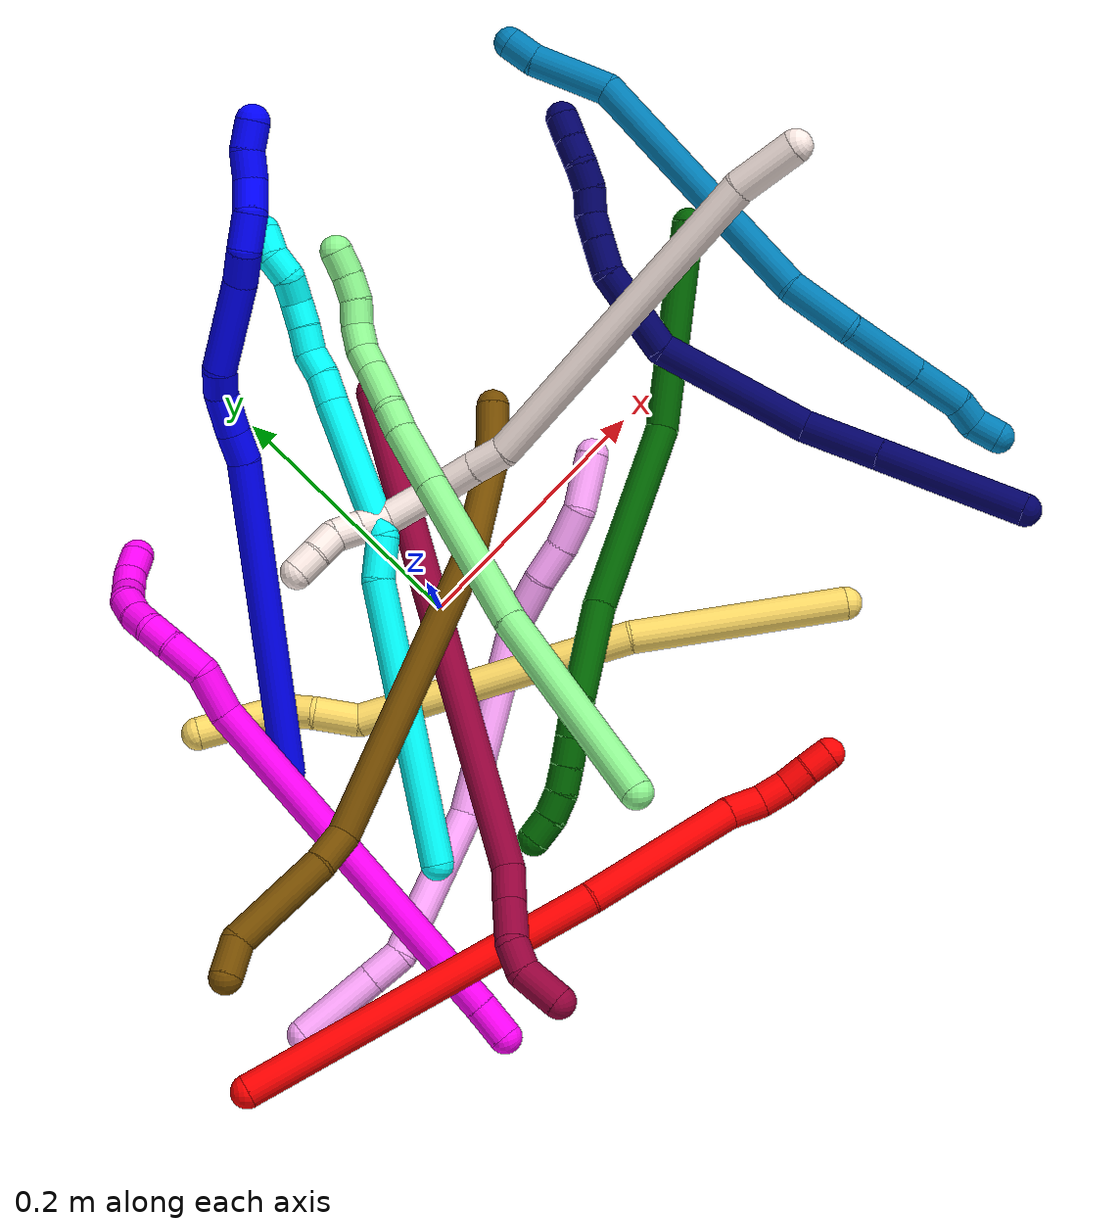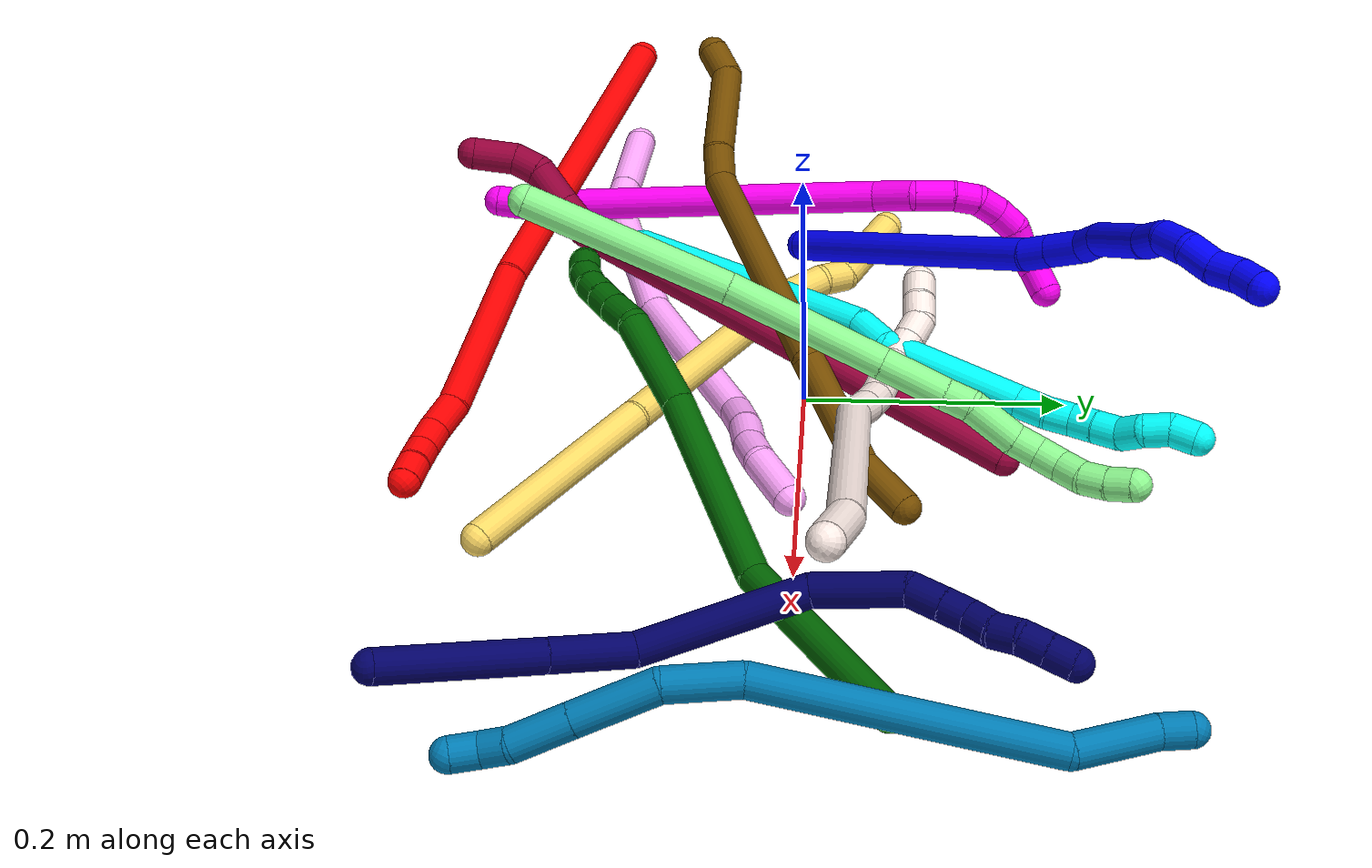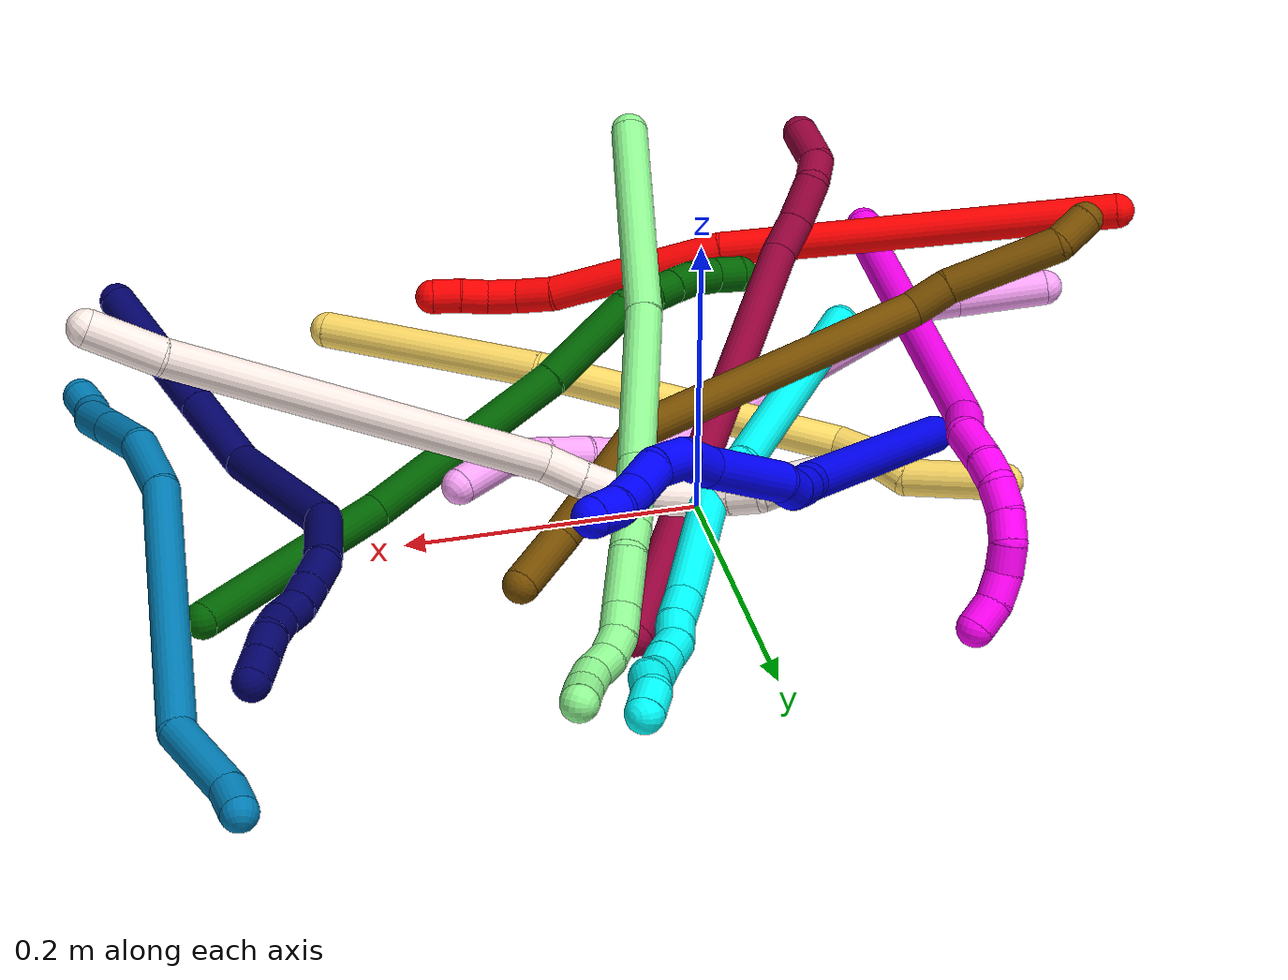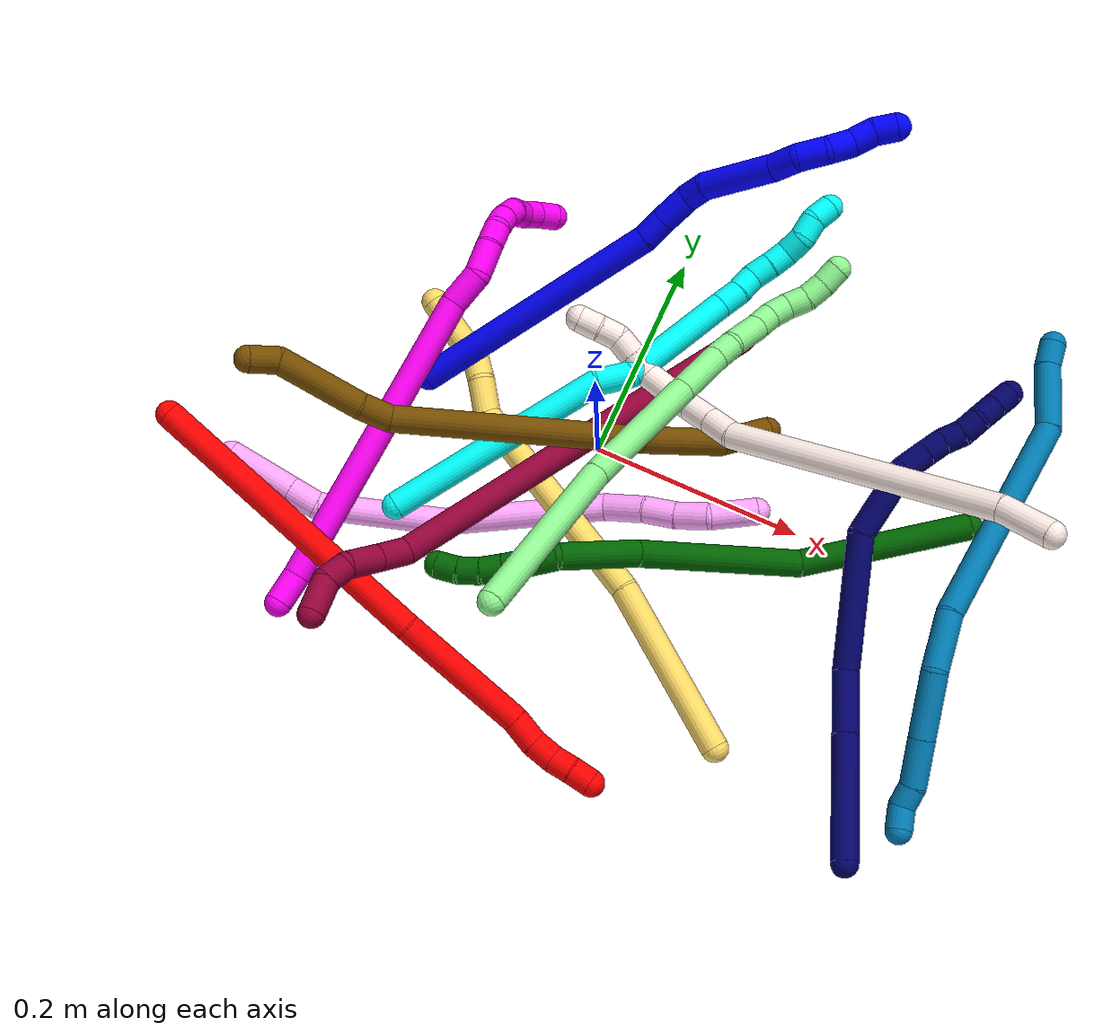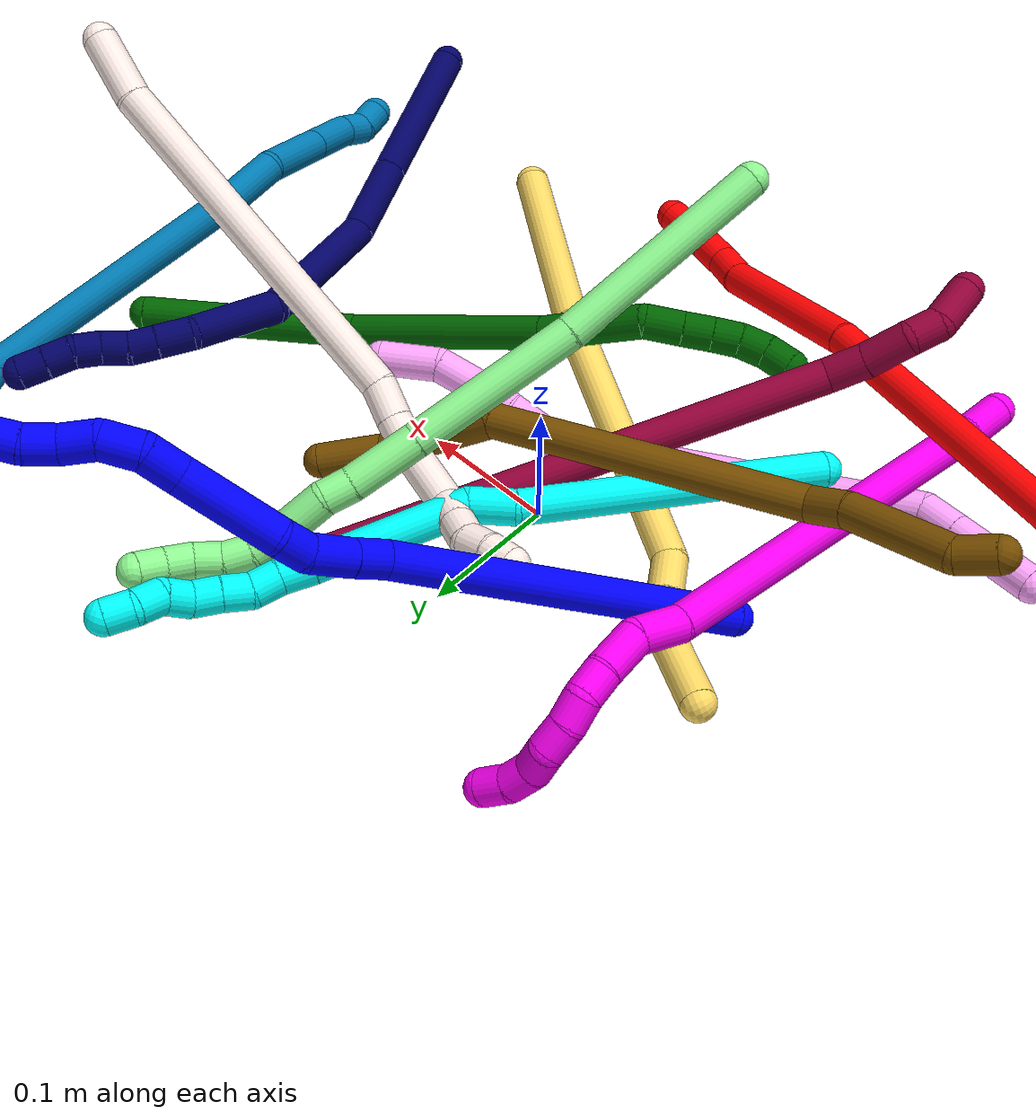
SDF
<sdf version="1.7">
 <world name="default">
  <plugin name="TubeGeneratorPlugin" filename="libtube_generator_plugin.so"/>
  <model name="photoneo_s_sensor">
   <static>1</static>
   <pose>0 0 2 1.57079 1.57079 3.14159</pose>
   <link name="link">
    <inertial><mass>0.1</mass></inertial>
    <sensor name="sensor" type="depth">
     <update_rate>30</update_rate>
     <camera>
      <horizontal_fov>1.22</horizontal_fov>
      <image><width>1920</width><height>1200</height><format>B8G8R8</format></image>
      <clip><near>0.1</near><far>4</far></clip>
      <depth_camera><output>points</output></depth_camera>
     </camera>
     <plugin name="camera_plugin" filename="libgazebo_ros_depth_camera.so">
      <baseline>0.2</baseline>
      <alwaysOn>1</alwaysOn>
      <updateRate>0.0</updateRate>
      <cameraName>camera_ir</cameraName>
      <imageTopicName>/camera/color/image_raw</imageTopicName>
      <cameraInfoTopicName>/camera/color/camera_info</cameraInfoTopicName>
      <depthImageTopicName>/camera/depth/image_raw</depthImageTopicName>
      <depthImageCameraInfoTopicName>/camera/depth/camera_info</depthImageCameraInfoTopicName>
      <pointCloudTopicName>/camera/depth/points</pointCloudTopicName>
      <frameName>fr_optical</frameName>
      <pointCloudCutoff>0.1</pointCloudCutoff>
      <pointCloudCutoffMax>2.0</pointCloudCutoffMax>
      <distortionK1>0</distortionK1>
      <distortionK2>0</distortionK2>
      <distortionK3>0</distortionK3>
      <distortionT1>0</distortionT1>
      <distortionT2>0</distortionT2>
      <CxPrime>0</CxPrime>
      <Cx>0</Cx>
      <Cy>0</Cy>
      <focalLength>0</focalLength>
      <hackBaseline>0</hackBaseline>
     </plugin>
    </sensor>
   </link>
  </model>
  <gravity>0 0 -9.8</gravity>
  <magnetic_field>6e-06 2.3e-05 -4.2e-05</magnetic_field>
  <atmosphere type="adiabatic"/>
  <physics name="default_physics" default="0" type="ode">
   <max_step_size>0.003</max_step_size>
   <real_time_factor>1</real_time_factor>
   <real_time_update_rate>1000</real_time_update_rate>
   <max_contacts>10000</max_contacts>
   <ode>
    <solver>
     <type>quick</type>
     <iters>100</iters>
     <sor>1.3</sor>
     <use_dynamic_moi_rescaling>0</use_dynamic_moi_rescaling>
    </solver>
    <constraints>
     <contact_max_correcting_vel>0</contact_max_correcting_vel>
     <contact_surface_layer>0.001</contact_surface_layer>
     <cfm>0</cfm>
     <erp>0.2</erp>
    </constraints>
   </ode>
  </physics>
  <scene><ambient>0.4 0.4 0.4 1</ambient><background>0.7 0.7 0.7 1</background><shadows>0</shadows></scene>
  <audio><device>default</device></audio>
  <spherical_coordinates>
   <surface_model>EARTH_WGS84</surface_model>
   <latitude_deg>0</latitude_deg>
   <longitude_deg>0</longitude_deg>
   <elevation>0</elevation>
   <heading_deg>0</heading_deg>
  </spherical_coordinates>
  <model name="bin">
   <static>1</static>
   <link name="bottom">
    <collision name="collision-bottom">
     <pose>0 0 -0.01 0 -0 0</pose>
     <geometry><box><size>0.8 0.6 0.02</size></box></geometry>
     <surface>
      <friction><ode><mu>100</mu><mu2>100</mu2></ode></friction>
      <contact><collide_bitmask>65535</collide_bitmask></contact>
     </surface>
    </collision>
   </link>
   <link name="west_wall">
    <collision name="collision-west_wall">
     <pose>-0.41 0 0.1 0 -0 0</pose>
     <geometry><box><size>0.02 0.6 0.2</size></box></geometry>
     <surface>
      <friction><ode><mu>100</mu><mu2>100</mu2></ode></friction>
      <contact><collide_bitmask>65535</collide_bitmask></contact>
     </surface>
    </collision>
   </link>
   <link name="east_wall">
    <collision name="collision-east_wall">
     <pose>0.41 0 0.1 0 -0 0</pose>
     <geometry><box><size>0.02 0.6 0.2</size></box></geometry>
     <surface>
      <friction><ode><mu>100</mu><mu2>100</mu2></ode></friction>
      <contact><collide_bitmask>65535</collide_bitmask></contact>
     </surface>
    </collision>
   </link>
   <link name="south_wall">
    <collision name="collision-south_wall">
     <pose>0 -0.31 0.1 0 -0 0</pose>
     <geometry><box><size>0.8 0.02 0.2</size></box></geometry>
     <surface>
      <friction><ode><mu>100</mu><mu2>100</mu2></ode></friction>
      <contact><collide_bitmask>65535</collide_bitmask></contact>
     </surface>
    </collision>
   </link>
   <link name="north_wall">
    <collision name="collision-north_wall">
     <pose>0 0.31 0.1 0 -0 0</pose>
     <geometry><box><size>0.8 0.02 0.2</size></box></geometry>
     <surface>
      <friction><ode><mu>100</mu><mu2>100</mu2></ode></friction>
      <contact><collide_bitmask>65535</collide_bitmask></contact>
     </surface>
    </collision>
   </link>
  </model>
  <model name="1">
   <static>0</static>
   <link name="1">
    <collision name="collision-cylinder-e_1_1_4">
     <pose>0.011985 0.020886 0.118688 -0.174193 0.099124 -0.008662</pose>
     <geometry><cylinder><radius>0.0125</radius><length>0.242212</length></cylinder></geometry>
     <surface>
      <friction><ode><mu>1.16</mu><mu2>1.16</mu2><slip1>0</slip1><slip2>0</slip2></ode></friction>
      <contact><ode><kp>1e+06</kp><kd>1</kd><max_vel>0</max_vel><min_depth>0.001</min_depth></ode></contact>
     </surface>
    </collision>
    <visual name="visual-cylinder-e_1_1_4">
     <pose>0.011985 0.020886 0.118688 -0.174193 0.099124 -0.008662</pose>
     <geometry><cylinder><radius>0.0125</radius><length>0.242212</length></cylinder></geometry>
     <material><ambient>0 0 1 1</ambient></material>
    </visual>
    <collision name="collision-cylinder-e_2_4_5">
     <pose>0.02565 0.04611 0.247919 -0.390303 0.146286 -0.028966</pose>
     <geometry><cylinder><radius>0.0125</radius><length>0.023049</length></cylinder></geometry>
     <surface>
      <friction><ode><mu>1.16</mu><mu2>1.16</mu2><slip1>0</slip1><slip2>0</slip2></ode></friction>
      <contact><ode><kp>1e+06</kp><kd>1</kd><max_vel>0</max_vel><min_depth>0.001</min_depth></ode></contact>
     </surface>
    </collision>
    <visual name="visual-cylinder-e_2_4_5">
     <pose>0.02565 0.04611 0.247919 -0.390303 0.146286 -0.028966</pose>
     <geometry><cylinder><radius>0.0125</radius><length>0.023049</length></cylinder></geometry>
     <material><ambient>0 0 1 1</ambient></material>
    </visual>
    <collision name="collision-cylinder-e_3_5_6">
     <pose>0.028859 0.055513 0.2725 -0.34629 0.102124 -0.017876</pose>
     <geometry><cylinder><radius>0.0125</radius><length>0.030002</length></cylinder></geometry>
     <surface>
      <friction><ode><mu>1.16</mu><mu2>1.16</mu2><slip1>0</slip1><slip2>0</slip2></ode></friction>
      <contact><ode><kp>1e+06</kp><kd>1</kd><max_vel>0</max_vel><min_depth>0.001</min_depth></ode></contact>
     </surface>
    </collision>
    <visual name="visual-cylinder-e_3_5_6">
     <pose>0.028859 0.055513 0.2725 -0.34629 0.102124 -0.017876</pose>
     <geometry><cylinder><radius>0.0125</radius><length>0.030002</length></cylinder></geometry>
     <material><ambient>0 0 1 1</ambient></material>
    </visual>
    <collision name="collision-cylinder-e_4_6_7">
     <pose>0.027699 0.063306 0.296185 -0.275537 -0.26207 0.036541</pose>
     <geometry><cylinder><radius>0.0125</radius><length>0.020761</length></cylinder></geometry>
     <surface>
      <friction><ode><mu>1.16</mu><mu2>1.16</mu2><slip1>0</slip1><slip2>0</slip2></ode></friction>
      <contact><ode><kp>1e+06</kp><kd>1</kd><max_vel>0</max_vel><min_depth>0.001</min_depth></ode></contact>
     </surface>
    </collision>
    <visual name="visual-cylinder-e_4_6_7">
     <pose>0.027699 0.063306 0.296185 -0.275537 -0.26207 0.036541</pose>
     <geometry><cylinder><radius>0.0125</radius><length>0.020761</length></cylinder></geometry>
     <material><ambient>0 0 1 1</ambient></material>
    </visual>
    <collision name="collision-cylinder-e_5_7_8">
     <pose>0.016578 0.064861 0.338903 0.035441 -0.249496 -0.004445</pose>
     <geometry><cylinder><radius>0.0125</radius><length>0.068296</length></cylinder></geometry>
     <surface>
      <friction><ode><mu>1.16</mu><mu2>1.16</mu2><slip1>0</slip1><slip2>0</slip2></ode></friction>
      <contact><ode><kp>1e+06</kp><kd>1</kd><max_vel>0</max_vel><min_depth>0.001</min_depth></ode></contact>
     </surface>
    </collision>
    <visual name="visual-cylinder-e_5_7_8">
     <pose>0.016578 0.064861 0.338903 0.035441 -0.249496 -0.004445</pose>
     <geometry><cylinder><radius>0.0125</radius><length>0.068296</length></cylinder></geometry>
     <material><ambient>0 0 1 1</ambient></material>
    </visual>
    <collision name="collision-cylinder-e_6_8_9">
     <pose>0.004658 0.064961 0.3837 -0.108058 -0.287531 0.015658</pose>
     <geometry><cylinder><radius>0.0125</radius><length>0.024601</length></cylinder></geometry>
     <surface>
      <friction><ode><mu>1.16</mu><mu2>1.16</mu2><slip1>0</slip1><slip2>0</slip2></ode></friction>
      <contact><ode><kp>1e+06</kp><kd>1</kd><max_vel>0</max_vel><min_depth>0.001</min_depth></ode></contact>
     </surface>
    </collision>
    <visual name="visual-cylinder-e_6_8_9">
     <pose>0.004658 0.064961 0.3837 -0.108058 -0.287531 0.015658</pose>
     <geometry><cylinder><radius>0.0125</radius><length>0.024601</length></cylinder></geometry>
     <material><ambient>0 0 1 1</ambient></material>
    </visual>
    <collision name="collision-cylinder-e_7_9_10">
     <pose>0.002162 0.06426 0.408164 0.153695 0.076886 0.005923</pose>
     <geometry><cylinder><radius>0.0125</radius><length>0.025854</length></cylinder></geometry>
     <surface>
      <friction><ode><mu>1.16</mu><mu2>1.16</mu2><slip1>0</slip1><slip2>0</slip2></ode></friction>
      <contact><ode><kp>1e+06</kp><kd>1</kd><max_vel>0</max_vel><min_depth>0.001</min_depth></ode></contact>
     </surface>
    </collision>
    <visual name="visual-cylinder-e_7_9_10">
     <pose>0.002162 0.06426 0.408164 0.153695 0.076886 0.005923</pose>
     <geometry><cylinder><radius>0.0125</radius><length>0.025854</length></cylinder></geometry>
     <material><ambient>0 0 1 1</ambient></material>
    </visual>
    <collision name="collision-cylinder-e_8_10_11">
     <pose>0.00868 0.059633 0.431037 0.256043 0.485238 0.063696</pose>
     <geometry><cylinder><radius>0.0125</radius><length>0.02369</length></cylinder></geometry>
     <surface>
      <friction><ode><mu>1.16</mu><mu2>1.16</mu2><slip1>0</slip1><slip2>0</slip2></ode></friction>
      <contact><ode><kp>1e+06</kp><kd>1</kd><max_vel>0</max_vel><min_depth>0.001</min_depth></ode></contact>
     </surface>
    </collision>
    <visual name="visual-cylinder-e_8_10_11">
     <pose>0.00868 0.059633 0.431037 0.256043 0.485238 0.063696</pose>
     <geometry><cylinder><radius>0.0125</radius><length>0.02369</length></cylinder></geometry>
     <material><ambient>0 0 1 1</ambient></material>
    </visual>
    <collision name="collision-cylinder-e_9_11_12">
     <pose>0.017417 0.057218 0.451254 -0.023645 0.308362 -0.003675</pose>
     <geometry><cylinder><radius>0.0125</radius><length>0.021166</length></cylinder></geometry>
     <surface>
      <friction><ode><mu>1.16</mu><mu2>1.16</mu2><slip1>0</slip1><slip2>0</slip2></ode></friction>
      <contact><ode><kp>1e+06</kp><kd>1</kd><max_vel>0</max_vel><min_depth>0.001</min_depth></ode></contact>
     </surface>
    </collision>
    <visual name="visual-cylinder-e_9_11_12">
     <pose>0.017417 0.057218 0.451254 -0.023645 0.308362 -0.003675</pose>
     <geometry><cylinder><radius>0.0125</radius><length>0.021166</length></cylinder></geometry>
     <material><ambient>0 0 1 1</ambient></material>
    </visual>
    <collision name="collision-cylinder-e_10_12_2">
     <pose>0.02194 0.055235 0.471187 0.221787 0.129105 0.014396</pose>
     <geometry><cylinder><radius>0.0125</radius><length>0.020368</length></cylinder></geometry>
     <surface>
      <friction><ode><mu>1.16</mu><mu2>1.16</mu2><slip1>0</slip1><slip2>0</slip2></ode></friction>
      <contact><ode><kp>1e+06</kp><kd>1</kd><max_vel>0</max_vel><min_depth>0.001</min_depth></ode></contact>
     </surface>
    </collision>
    <visual name="visual-cylinder-e_10_12_2">
     <pose>0.02194 0.055235 0.471187 0.221787 0.129105 0.014396</pose>
     <geometry><cylinder><radius>0.0125</radius><length>0.020368</length></cylinder></geometry>
     <material><ambient>0 0 1 1</ambient></material>
    </visual>
    <collision name="collision-sphere-2">
     <pose>0.023251 0.053013 0.481039 0 -0 0</pose>
     <geometry><sphere><radius>0.0125</radius></sphere></geometry>
     <surface>
      <friction><ode><mu>1.16</mu><mu2>1.16</mu2><slip1>0</slip1><slip2>0</slip2></ode></friction>
      <contact><ode><kp>1e+06</kp><kd>1</kd><max_vel>0</max_vel><min_depth>0.001</min_depth></ode></contact>
     </surface>
    </collision>
    <visual name="visual-sphere-2">
     <pose>0.023251 0.053013 0.481039 0 -0 0</pose>
     <geometry><sphere><radius>0.0125</radius></sphere></geometry>
     <material><ambient>0 0 1 1</ambient></material>
    </visual>
    <collision name="collision-sphere-12">
     <pose>0.020629 0.057456 0.461335 0 -0 0</pose>
     <geometry><sphere><radius>0.0125</radius></sphere></geometry>
     <surface>
      <friction><ode><mu>1.16</mu><mu2>1.16</mu2><slip1>0</slip1><slip2>0</slip2></ode></friction>
      <contact><ode><kp>1e+06</kp><kd>1</kd><max_vel>0</max_vel><min_depth>0.001</min_depth></ode></contact>
     </surface>
    </collision>
    <visual name="visual-sphere-12">
     <pose>0.020629 0.057456 0.461335 0 -0 0</pose>
     <geometry><sphere><radius>0.0125</radius></sphere></geometry>
     <material><ambient>0 0 1 1</ambient></material>
    </visual>
    <collision name="collision-sphere-11">
     <pose>0.014205 0.056979 0.441173 0 -0 0</pose>
     <geometry><sphere><radius>0.0125</radius></sphere></geometry>
     <surface>
      <friction><ode><mu>1.16</mu><mu2>1.16</mu2><slip1>0</slip1><slip2>0</slip2></ode></friction>
      <contact><ode><kp>1e+06</kp><kd>1</kd><max_vel>0</max_vel><min_depth>0.001</min_depth></ode></contact>
     </surface>
    </collision>
    <visual name="visual-sphere-11">
     <pose>0.014205 0.056979 0.441173 0 -0 0</pose>
     <geometry><sphere><radius>0.0125</radius></sphere></geometry>
     <material><ambient>0 0 1 1</ambient></material>
    </visual>
    <collision name="collision-sphere-10">
     <pose>0.003155 0.062287 0.4209 0 -0 0</pose>
     <geometry><sphere><radius>0.0125</radius></sphere></geometry>
     <surface>
      <friction><ode><mu>1.16</mu><mu2>1.16</mu2><slip1>0</slip1><slip2>0</slip2></ode></friction>
      <contact><ode><kp>1e+06</kp><kd>1</kd><max_vel>0</max_vel><min_depth>0.001</min_depth></ode></contact>
     </surface>
    </collision>
    <visual name="visual-sphere-10">
     <pose>0.003155 0.062287 0.4209 0 -0 0</pose>
     <geometry><sphere><radius>0.0125</radius></sphere></geometry>
     <material><ambient>0 0 1 1</ambient></material>
    </visual>
    <collision name="collision-sphere-9">
     <pose>0.001169 0.066233 0.395427 0 -0 0</pose>
     <geometry><sphere><radius>0.0125</radius></sphere></geometry>
     <surface>
      <friction><ode><mu>1.16</mu><mu2>1.16</mu2><slip1>0</slip1><slip2>0</slip2></ode></friction>
      <contact><ode><kp>1e+06</kp><kd>1</kd><max_vel>0</max_vel><min_depth>0.001</min_depth></ode></contact>
     </surface>
    </collision>
    <visual name="visual-sphere-9">
     <pose>0.001169 0.066233 0.395427 0 -0 0</pose>
     <geometry><sphere><radius>0.0125</radius></sphere></geometry>
     <material><ambient>0 0 1 1</ambient></material>
    </visual>
    <collision name="collision-sphere-4">
     <pose>0.02397 0.041772 0.237375 0 -0 0</pose>
     <geometry><sphere><radius>0.0125</radius></sphere></geometry>
     <surface>
      <friction><ode><mu>1.16</mu><mu2>1.16</mu2><slip1>0</slip1><slip2>0</slip2></ode></friction>
      <contact><ode><kp>1e+06</kp><kd>1</kd><max_vel>0</max_vel><min_depth>0.001</min_depth></ode></contact>
     </surface>
    </collision>
    <visual name="visual-sphere-4">
     <pose>0.02397 0.041772 0.237375 0 -0 0</pose>
     <geometry><sphere><radius>0.0125</radius></sphere></geometry>
     <material><ambient>0 0 1 1</ambient></material>
    </visual>
    <collision name="collision-sphere-1">
     <geometry><sphere><radius>0.0125</radius></sphere></geometry>
     <surface>
      <friction><ode><mu>1.16</mu><mu2>1.16</mu2><slip1>0</slip1><slip2>0</slip2></ode></friction>
      <contact><ode><kp>1e+06</kp><kd>1</kd><max_vel>0</max_vel><min_depth>0.001</min_depth></ode></contact>
     </surface>
    </collision>
    <visual name="visual-sphere-1">
     <geometry><sphere><radius>0.0125</radius></sphere></geometry>
     <material><ambient>0 0 1 1</ambient></material>
    </visual>
    <collision name="collision-sphere-8">
     <pose>0.008146 0.063689 0.371973 0 -0 0</pose>
     <geometry><sphere><radius>0.0125</radius></sphere></geometry>
     <surface>
      <friction><ode><mu>1.16</mu><mu2>1.16</mu2><slip1>0</slip1><slip2>0</slip2></ode></friction>
      <contact><ode><kp>1e+06</kp><kd>1</kd><max_vel>0</max_vel><min_depth>0.001</min_depth></ode></contact>
     </surface>
    </collision>
    <visual name="visual-sphere-8">
     <pose>0.008146 0.063689 0.371973 0 -0 0</pose>
     <geometry><sphere><radius>0.0125</radius></sphere></geometry>
     <material><ambient>0 0 1 1</ambient></material>
    </visual>
    <collision name="collision-sphere-5">
     <pose>0.027329 0.050448 0.258463 0 -0 0</pose>
     <geometry><sphere><radius>0.0125</radius></sphere></geometry>
     <surface>
      <friction><ode><mu>1.16</mu><mu2>1.16</mu2><slip1>0</slip1><slip2>0</slip2></ode></friction>
      <contact><ode><kp>1e+06</kp><kd>1</kd><max_vel>0</max_vel><min_depth>0.001</min_depth></ode></contact>
     </surface>
    </collision>
    <visual name="visual-sphere-5">
     <pose>0.027329 0.050448 0.258463 0 -0 0</pose>
     <geometry><sphere><radius>0.0125</radius></sphere></geometry>
     <material><ambient>0 0 1 1</ambient></material>
    </visual>
    <collision name="collision-sphere-6">
     <pose>0.030388 0.060578 0.286537 0 -0 0</pose>
     <geometry><sphere><radius>0.0125</radius></sphere></geometry>
     <surface>
      <friction><ode><mu>1.16</mu><mu2>1.16</mu2><slip1>0</slip1><slip2>0</slip2></ode></friction>
      <contact><ode><kp>1e+06</kp><kd>1</kd><max_vel>0</max_vel><min_depth>0.001</min_depth></ode></contact>
     </surface>
    </collision>
    <visual name="visual-sphere-6">
     <pose>0.030388 0.060578 0.286537 0 -0 0</pose>
     <geometry><sphere><radius>0.0125</radius></sphere></geometry>
     <material><ambient>0 0 1 1</ambient></material>
    </visual>
    <collision name="collision-sphere-7">
     <pose>0.025009 0.066034 0.305833 0 -0 0</pose>
     <geometry><sphere><radius>0.0125</radius></sphere></geometry>
     <surface>
      <friction><ode><mu>1.16</mu><mu2>1.16</mu2><slip1>0</slip1><slip2>0</slip2></ode></friction>
      <contact><ode><kp>1e+06</kp><kd>1</kd><max_vel>0</max_vel><min_depth>0.001</min_depth></ode></contact>
     </surface>
    </collision>
    <visual name="visual-sphere-7">
     <pose>0.025009 0.066034 0.305833 0 -0 0</pose>
     <geometry><sphere><radius>0.0125</radius></sphere></geometry>
     <material><ambient>0 0 1 1</ambient></material>
    </visual>
    <inertial>
     <pose>0.014518 0.041079 0.242569 0 -0 0</pose>
     <mass>0.5</mass>
     <inertia>
      <ixx>0.001224</ixx>
      <ixy>0</ixy>
      <ixz>0</ixz>
      <iyy>0.001215</iyy>
      <iyz>0</iyz>
      <izz>-0.000281</izz>
     </inertia>
    </inertial>
   </link>
   <pose>-0.167681 -0.007006 0.028545 1.00729 0.809642 1.80847</pose>
  </model>
  <model name="2">
   <static>0</static>
   <link name="2">
    <collision name="collision-cylinder-e_1_1_4">
     <pose>0.047512 -0.018304 0.132244 0.137534 0.341905 0.02378</pose>
     <geometry><cylinder><radius>0.0125</radius><length>0.283414</length></cylinder></geometry>
     <surface>
      <friction><ode><mu>1.16</mu><mu2>1.16</mu2><slip1>0</slip1><slip2>0</slip2></ode></friction>
      <contact><ode><kp>1e+06</kp><kd>1</kd><max_vel>0</max_vel><min_depth>0.001</min_depth></ode></contact>
     </surface>
    </collision>
    <visual name="visual-cylinder-e_1_1_4">
     <pose>0.047512 -0.018304 0.132244 0.137534 0.341905 0.02378</pose>
     <geometry><cylinder><radius>0.0125</radius><length>0.283414</length></cylinder></geometry>
     <material><ambient>1 0 0 1</ambient></material>
    </visual>
    <collision name="collision-cylinder-e_2_4_5">
     <pose>0.111632 -0.054379 0.323052 0.294628 0.264987 0.039548</pose>
     <geometry><cylinder><radius>0.0125</radius><length>0.12683</length></cylinder></geometry>
     <surface>
      <friction><ode><mu>1.16</mu><mu2>1.16</mu2><slip1>0</slip1><slip2>0</slip2></ode></friction>
      <contact><ode><kp>1e+06</kp><kd>1</kd><max_vel>0</max_vel><min_depth>0.001</min_depth></ode></contact>
     </surface>
    </collision>
    <visual name="visual-cylinder-e_2_4_5">
     <pose>0.111632 -0.054379 0.323052 0.294628 0.264987 0.039548</pose>
     <geometry><cylinder><radius>0.0125</radius><length>0.12683</length></cylinder></geometry>
     <material><ambient>1 0 0 1</ambient></material>
    </visual>
    <collision name="collision-cylinder-e_3_5_6">
     <pose>0.130621 -0.073348 0.394828 0.090384 0.17756 0.008051</pose>
     <geometry><cylinder><radius>0.0125</radius><length>0.026955</length></cylinder></geometry>
     <surface>
      <friction><ode><mu>1.16</mu><mu2>1.16</mu2><slip1>0</slip1><slip2>0</slip2></ode></friction>
      <contact><ode><kp>1e+06</kp><kd>1</kd><max_vel>0</max_vel><min_depth>0.001</min_depth></ode></contact>
     </surface>
    </collision>
    <visual name="visual-cylinder-e_3_5_6">
     <pose>0.130621 -0.073348 0.394828 0.090384 0.17756 0.008051</pose>
     <geometry><cylinder><radius>0.0125</radius><length>0.026955</length></cylinder></geometry>
     <material><ambient>1 0 0 1</ambient></material>
    </visual>
    <collision name="collision-cylinder-e_4_6_7">
     <pose>0.137614 -0.075338 0.41829 0.077135 0.421728 0.016518</pose>
     <geometry><cylinder><radius>0.0125</radius><length>0.022537</length></cylinder></geometry>
     <surface>
      <friction><ode><mu>1.16</mu><mu2>1.16</mu2><slip1>0</slip1><slip2>0</slip2></ode></friction>
      <contact><ode><kp>1e+06</kp><kd>1</kd><max_vel>0</max_vel><min_depth>0.001</min_depth></ode></contact>
     </surface>
    </collision>
    <visual name="visual-cylinder-e_4_6_7">
     <pose>0.137614 -0.075338 0.41829 0.077135 0.421728 0.016518</pose>
     <geometry><cylinder><radius>0.0125</radius><length>0.022537</length></cylinder></geometry>
     <material><ambient>1 0 0 1</ambient></material>
    </visual>
    <collision name="collision-cylinder-e_5_7_8">
     <pose>0.148107 -0.076154 0.436714 0.002949 0.623745 0.000951</pose>
     <geometry><cylinder><radius>0.0125</radius><length>0.020137</length></cylinder></geometry>
     <surface>
      <friction><ode><mu>1.16</mu><mu2>1.16</mu2><slip1>0</slip1><slip2>0</slip2></ode></friction>
      <contact><ode><kp>1e+06</kp><kd>1</kd><max_vel>0</max_vel><min_depth>0.001</min_depth></ode></contact>
     </surface>
    </collision>
    <visual name="visual-cylinder-e_5_7_8">
     <pose>0.148107 -0.076154 0.436714 0.002949 0.623745 0.000951</pose>
     <geometry><cylinder><radius>0.0125</radius><length>0.020137</length></cylinder></geometry>
     <material><ambient>1 0 0 1</ambient></material>
    </visual>
    <collision name="collision-cylinder-e_6_8_2">
     <pose>0.159082 -0.077017 0.453525 0.096804 0.530702 0.026326</pose>
     <geometry><cylinder><radius>0.0125</radius><length>0.020127</length></cylinder></geometry>
     <surface>
      <friction><ode><mu>1.16</mu><mu2>1.16</mu2><slip1>0</slip1><slip2>0</slip2></ode></friction>
      <contact><ode><kp>1e+06</kp><kd>1</kd><max_vel>0</max_vel><min_depth>0.001</min_depth></ode></contact>
     </surface>
    </collision>
    <visual name="visual-cylinder-e_6_8_2">
     <pose>0.159082 -0.077017 0.453525 0.096804 0.530702 0.026326</pose>
     <geometry><cylinder><radius>0.0125</radius><length>0.020127</length></cylinder></geometry>
     <material><ambient>1 0 0 1</ambient></material>
    </visual>
    <collision name="collision-sphere-2">
     <pose>0.164175 -0.077856 0.462163 0 -0 0</pose>
     <geometry><sphere><radius>0.0125</radius></sphere></geometry>
     <surface>
      <friction><ode><mu>1.16</mu><mu2>1.16</mu2><slip1>0</slip1><slip2>0</slip2></ode></friction>
      <contact><ode><kp>1e+06</kp><kd>1</kd><max_vel>0</max_vel><min_depth>0.001</min_depth></ode></contact>
     </surface>
    </collision>
    <visual name="visual-sphere-2">
     <pose>0.164175 -0.077856 0.462163 0 -0 0</pose>
     <geometry><sphere><radius>0.0125</radius></sphere></geometry>
     <material><ambient>1 0 0 1</ambient></material>
    </visual>
    <collision name="collision-sphere-4">
     <pose>0.095024 -0.036607 0.264488 0 -0 0</pose>
     <geometry><sphere><radius>0.0125</radius></sphere></geometry>
     <surface>
      <friction><ode><mu>1.16</mu><mu2>1.16</mu2><slip1>0</slip1><slip2>0</slip2></ode></friction>
      <contact><ode><kp>1e+06</kp><kd>1</kd><max_vel>0</max_vel><min_depth>0.001</min_depth></ode></contact>
     </surface>
    </collision>
    <visual name="visual-sphere-4">
     <pose>0.095024 -0.036607 0.264488 0 -0 0</pose>
     <geometry><sphere><radius>0.0125</radius></sphere></geometry>
     <material><ambient>1 0 0 1</ambient></material>
    </visual>
    <collision name="collision-sphere-1">
     <geometry><sphere><radius>0.0125</radius></sphere></geometry>
     <surface>
      <friction><ode><mu>1.16</mu><mu2>1.16</mu2><slip1>0</slip1><slip2>0</slip2></ode></friction>
      <contact><ode><kp>1e+06</kp><kd>1</kd><max_vel>0</max_vel><min_depth>0.001</min_depth></ode></contact>
     </surface>
    </collision>
    <visual name="visual-sphere-1">
     <geometry><sphere><radius>0.0125</radius></sphere></geometry>
     <material><ambient>1 0 0 1</ambient></material>
    </visual>
    <collision name="collision-sphere-8">
     <pose>0.153988 -0.076179 0.444886 0 -0 0</pose>
     <geometry><sphere><radius>0.0125</radius></sphere></geometry>
     <surface>
      <friction><ode><mu>1.16</mu><mu2>1.16</mu2><slip1>0</slip1><slip2>0</slip2></ode></friction>
      <contact><ode><kp>1e+06</kp><kd>1</kd><max_vel>0</max_vel><min_depth>0.001</min_depth></ode></contact>
     </surface>
    </collision>
    <visual name="visual-sphere-8">
     <pose>0.153988 -0.076179 0.444886 0 -0 0</pose>
     <geometry><sphere><radius>0.0125</radius></sphere></geometry>
     <material><ambient>1 0 0 1</ambient></material>
    </visual>
    <collision name="collision-sphere-5">
     <pose>0.12824 -0.072151 0.381617 0 -0 0</pose>
     <geometry><sphere><radius>0.0125</radius></sphere></geometry>
     <surface>
      <friction><ode><mu>1.16</mu><mu2>1.16</mu2><slip1>0</slip1><slip2>0</slip2></ode></friction>
      <contact><ode><kp>1e+06</kp><kd>1</kd><max_vel>0</max_vel><min_depth>0.001</min_depth></ode></contact>
     </surface>
    </collision>
    <visual name="visual-sphere-5">
     <pose>0.12824 -0.072151 0.381617 0 -0 0</pose>
     <geometry><sphere><radius>0.0125</radius></sphere></geometry>
     <material><ambient>1 0 0 1</ambient></material>
    </visual>
    <collision name="collision-sphere-6">
     <pose>0.133001 -0.074546 0.40804 0 -0 0</pose>
     <geometry><sphere><radius>0.0125</radius></sphere></geometry>
     <surface>
      <friction><ode><mu>1.16</mu><mu2>1.16</mu2><slip1>0</slip1><slip2>0</slip2></ode></friction>
      <contact><ode><kp>1e+06</kp><kd>1</kd><max_vel>0</max_vel><min_depth>0.001</min_depth></ode></contact>
     </surface>
    </collision>
    <visual name="visual-sphere-6">
     <pose>0.133001 -0.074546 0.40804 0 -0 0</pose>
     <geometry><sphere><radius>0.0125</radius></sphere></geometry>
     <material><ambient>1 0 0 1</ambient></material>
    </visual>
    <collision name="collision-sphere-7">
     <pose>0.142226 -0.07613 0.428541 0 -0 0</pose>
     <geometry><sphere><radius>0.0125</radius></sphere></geometry>
     <surface>
      <friction><ode><mu>1.16</mu><mu2>1.16</mu2><slip1>0</slip1><slip2>0</slip2></ode></friction>
      <contact><ode><kp>1e+06</kp><kd>1</kd><max_vel>0</max_vel><min_depth>0.001</min_depth></ode></contact>
     </surface>
    </collision>
    <visual name="visual-sphere-7">
     <pose>0.142226 -0.07613 0.428541 0 -0 0</pose>
     <geometry><sphere><radius>0.0125</radius></sphere></geometry>
     <material><ambient>1 0 0 1</ambient></material>
    </visual>
    <inertial>
     <pose>0.080861 -0.037686 0.232889 0 -0 0</pose>
     <mass>0.5</mass>
     <inertia>
      <ixx>0.002035</ixx>
      <ixy>0</ixy>
      <ixz>0</ixz>
      <iyy>0.00211</iyy>
      <iyz>0</iyz>
      <izz>-0.000356</izz>
     </inertia>
    </inertial>
   </link>
   <pose>-0.346722 -0.152256 0.098874 1.84388 -0.55205 0.767841</pose>
  </model>
  <model name="3">
   <static>0</static>
   <link name="3">
    <collision name="collision-cylinder-e_1_1_4">
     <pose>-0.011565 0.04499 0.096465 -0.4364 -0.108228 0.02402</pose>
     <geometry><cylinder><radius>0.0125</radius><length>0.214134</length></cylinder></geometry>
     <surface>
      <friction><ode><mu>1.16</mu><mu2>1.16</mu2><slip1>0</slip1><slip2>0</slip2></ode></friction>
      <contact><ode><kp>1e+06</kp><kd>1</kd><max_vel>0</max_vel><min_depth>0.001</min_depth></ode></contact>
     </surface>
    </collision>
    <visual name="visual-cylinder-e_1_1_4">
     <pose>-0.011565 0.04499 0.096465 -0.4364 -0.108228 0.02402</pose>
     <geometry><cylinder><radius>0.0125</radius><length>0.214134</length></cylinder></geometry>
     <material><ambient>0.003922 1 0.996078 1</ambient></material>
    </visual>
    <collision name="collision-cylinder-e_2_4_5">
     <pose>-0.020484 0.094046 0.208112 -0.261653 0.166806 -0.021998</pose>
     <geometry><cylinder><radius>0.0125</radius><length>0.031878</length></cylinder></geometry>
     <surface>
      <friction><ode><mu>1.16</mu><mu2>1.16</mu2><slip1>0</slip1><slip2>0</slip2></ode></friction>
      <contact><ode><kp>1e+06</kp><kd>1</kd><max_vel>0</max_vel><min_depth>0.001</min_depth></ode></contact>
     </surface>
    </collision>
    <visual name="visual-cylinder-e_2_4_5">
     <pose>-0.020484 0.094046 0.208112 -0.261653 0.166806 -0.021998</pose>
     <geometry><cylinder><radius>0.0125</radius><length>0.031878</length></cylinder></geometry>
     <material><ambient>0.003922 1 0.996078 1</ambient></material>
    </visual>
    <collision name="collision-cylinder-e_3_5_6">
     <pose>-0.021485 0.133246 0.266018 -0.688226 -0.065849 0.023606</pose>
     <geometry><cylinder><radius>0.0125</radius><length>0.11087</length></cylinder></geometry>
     <surface>
      <friction><ode><mu>1.16</mu><mu2>1.16</mu2><slip1>0</slip1><slip2>0</slip2></ode></friction>
      <contact><ode><kp>1e+06</kp><kd>1</kd><max_vel>0</max_vel><min_depth>0.001</min_depth></ode></contact>
     </surface>
    </collision>
    <visual name="visual-cylinder-e_3_5_6">
     <pose>-0.021485 0.133246 0.266018 -0.688226 -0.065849 0.023606</pose>
     <geometry><cylinder><radius>0.0125</radius><length>0.11087</length></cylinder></geometry>
     <material><ambient>0.003922 1 0.996078 1</ambient></material>
    </visual>
    <collision name="collision-cylinder-e_4_6_7">
     <pose>-0.026062 0.175004 0.317907 -0.625833 -0.082038 0.026556</pose>
     <geometry><cylinder><radius>0.0125</radius><length>0.022691</length></cylinder></geometry>
     <surface>
      <friction><ode><mu>1.16</mu><mu2>1.16</mu2><slip1>0</slip1><slip2>0</slip2></ode></friction>
      <contact><ode><kp>1e+06</kp><kd>1</kd><max_vel>0</max_vel><min_depth>0.001</min_depth></ode></contact>
     </surface>
    </collision>
    <visual name="visual-cylinder-e_4_6_7">
     <pose>-0.026062 0.175004 0.317907 -0.625833 -0.082038 0.026556</pose>
     <geometry><cylinder><radius>0.0125</radius><length>0.022691</length></cylinder></geometry>
     <material><ambient>0.003922 1 0.996078 1</ambient></material>
    </visual>
    <collision name="collision-cylinder-e_5_7_8">
     <pose>-0.028893 0.188552 0.334054 -0.781189 -0.190975 0.078833</pose>
     <geometry><cylinder><radius>0.0125</radius><length>0.020033</length></cylinder></geometry>
     <surface>
      <friction><ode><mu>1.16</mu><mu2>1.16</mu2><slip1>0</slip1><slip2>0</slip2></ode></friction>
      <contact><ode><kp>1e+06</kp><kd>1</kd><max_vel>0</max_vel><min_depth>0.001</min_depth></ode></contact>
     </surface>
    </collision>
    <visual name="visual-cylinder-e_5_7_8">
     <pose>-0.028893 0.188552 0.334054 -0.781189 -0.190975 0.078833</pose>
     <geometry><cylinder><radius>0.0125</radius><length>0.020033</length></cylinder></geometry>
     <material><ambient>0.003922 1 0.996078 1</ambient></material>
    </visual>
    <collision name="collision-cylinder-e_6_8_9">
     <pose>-0.032499 0.199351 0.350183 -0.400692 -0.169986 0.034599</pose>
     <geometry><cylinder><radius>0.0125</radius><length>0.020155</length></cylinder></geometry>
     <surface>
      <friction><ode><mu>1.16</mu><mu2>1.16</mu2><slip1>0</slip1><slip2>0</slip2></ode></friction>
      <contact><ode><kp>1e+06</kp><kd>1</kd><max_vel>0</max_vel><min_depth>0.001</min_depth></ode></contact>
     </surface>
    </collision>
    <visual name="visual-cylinder-e_6_8_9">
     <pose>-0.032499 0.199351 0.350183 -0.400692 -0.169986 0.034599</pose>
     <geometry><cylinder><radius>0.0125</radius><length>0.020155</length></cylinder></geometry>
     <material><ambient>0.003922 1 0.996078 1</ambient></material>
    </visual>
    <collision name="collision-cylinder-e_7_9_10">
     <pose>-0.035998 0.207882 0.368066 -0.489687 -0.17924 0.044897</pose>
     <geometry><cylinder><radius>0.0125</radius><length>0.020125</length></cylinder></geometry>
     <surface>
      <friction><ode><mu>1.16</mu><mu2>1.16</mu2><slip1>0</slip1><slip2>0</slip2></ode></friction>
      <contact><ode><kp>1e+06</kp><kd>1</kd><max_vel>0</max_vel><min_depth>0.001</min_depth></ode></contact>
     </surface>
    </collision>
    <visual name="visual-cylinder-e_7_9_10">
     <pose>-0.035998 0.207882 0.368066 -0.489687 -0.17924 0.044897</pose>
     <geometry><cylinder><radius>0.0125</radius><length>0.020125</length></cylinder></geometry>
     <material><ambient>0.003922 1 0.996078 1</ambient></material>
    </visual>
    <collision name="collision-cylinder-e_8_10_11">
     <pose>-0.042726 0.213725 0.385484 -0.135732 -0.512881 0.035642</pose>
     <geometry><cylinder><radius>0.0125</radius><length>0.020109</length></cylinder></geometry>
     <surface>
      <friction><ode><mu>1.16</mu><mu2>1.16</mu2><slip1>0</slip1><slip2>0</slip2></ode></friction>
      <contact><ode><kp>1e+06</kp><kd>1</kd><max_vel>0</max_vel><min_depth>0.001</min_depth></ode></contact>
     </surface>
    </collision>
    <visual name="visual-cylinder-e_8_10_11">
     <pose>-0.042726 0.213725 0.385484 -0.135732 -0.512881 0.035642</pose>
     <geometry><cylinder><radius>0.0125</radius><length>0.020109</length></cylinder></geometry>
     <material><ambient>0.003922 1 0.996078 1</ambient></material>
    </visual>
    <collision name="collision-cylinder-e_9_11_12">
     <pose>-0.052424 0.22061 0.400861 -0.705164 -0.496474 0.185991</pose>
     <geometry><cylinder><radius>0.0125</radius><length>0.020003</length></cylinder></geometry>
     <surface>
      <friction><ode><mu>1.16</mu><mu2>1.16</mu2><slip1>0</slip1><slip2>0</slip2></ode></friction>
      <contact><ode><kp>1e+06</kp><kd>1</kd><max_vel>0</max_vel><min_depth>0.001</min_depth></ode></contact>
     </surface>
    </collision>
    <visual name="visual-cylinder-e_9_11_12">
     <pose>-0.052424 0.22061 0.400861 -0.705164 -0.496474 0.185991</pose>
     <geometry><cylinder><radius>0.0125</radius><length>0.020003</length></cylinder></geometry>
     <material><ambient>0.003922 1 0.996078 1</ambient></material>
    </visual>
    <collision name="collision-cylinder-e_10_12_2">
     <pose>-0.058311 0.232074 0.415654 -0.618695 -0.112608 0.036025</pose>
     <geometry><cylinder><radius>0.0125</radius><length>0.020002</length></cylinder></geometry>
     <surface>
      <friction><ode><mu>1.16</mu><mu2>1.16</mu2><slip1>0</slip1><slip2>0</slip2></ode></friction>
      <contact><ode><kp>1e+06</kp><kd>1</kd><max_vel>0</max_vel><min_depth>0.001</min_depth></ode></contact>
     </surface>
    </collision>
    <visual name="visual-cylinder-e_10_12_2">
     <pose>-0.058311 0.232074 0.415654 -0.618695 -0.112608 0.036025</pose>
     <geometry><cylinder><radius>0.0125</radius><length>0.020002</length></cylinder></geometry>
     <material><ambient>0.003922 1 0.996078 1</ambient></material>
    </visual>
    <collision name="collision-sphere-2">
     <pose>-0.059435 0.237837 0.423749 0 -0 0</pose>
     <geometry><sphere><radius>0.0125</radius></sphere></geometry>
     <surface>
      <friction><ode><mu>1.16</mu><mu2>1.16</mu2><slip1>0</slip1><slip2>0</slip2></ode></friction>
      <contact><ode><kp>1e+06</kp><kd>1</kd><max_vel>0</max_vel><min_depth>0.001</min_depth></ode></contact>
     </surface>
    </collision>
    <visual name="visual-sphere-2">
     <pose>-0.059435 0.237837 0.423749 0 -0 0</pose>
     <geometry><sphere><radius>0.0125</radius></sphere></geometry>
     <material><ambient>0.003922 1 0.996078 1</ambient></material>
    </visual>
    <collision name="collision-sphere-12">
     <pose>-0.057188 0.22631 0.407558 0 -0 0</pose>
     <geometry><sphere><radius>0.0125</radius></sphere></geometry>
     <surface>
      <friction><ode><mu>1.16</mu><mu2>1.16</mu2><slip1>0</slip1><slip2>0</slip2></ode></friction>
      <contact><ode><kp>1e+06</kp><kd>1</kd><max_vel>0</max_vel><min_depth>0.001</min_depth></ode></contact>
     </surface>
    </collision>
    <visual name="visual-sphere-12">
     <pose>-0.057188 0.22631 0.407558 0 -0 0</pose>
     <geometry><sphere><radius>0.0125</radius></sphere></geometry>
     <material><ambient>0.003922 1 0.996078 1</ambient></material>
    </visual>
    <collision name="collision-sphere-11">
     <pose>-0.04766 0.21491 0.394165 0 -0 0</pose>
     <geometry><sphere><radius>0.0125</radius></sphere></geometry>
     <surface>
      <friction><ode><mu>1.16</mu><mu2>1.16</mu2><slip1>0</slip1><slip2>0</slip2></ode></friction>
      <contact><ode><kp>1e+06</kp><kd>1</kd><max_vel>0</max_vel><min_depth>0.001</min_depth></ode></contact>
     </surface>
    </collision>
    <visual name="visual-sphere-11">
     <pose>-0.04766 0.21491 0.394165 0 -0 0</pose>
     <geometry><sphere><radius>0.0125</radius></sphere></geometry>
     <material><ambient>0.003922 1 0.996078 1</ambient></material>
    </visual>
    <collision name="collision-sphere-10">
     <pose>-0.037792 0.212539 0.376804 0 -0 0</pose>
     <geometry><sphere><radius>0.0125</radius></sphere></geometry>
     <surface>
      <friction><ode><mu>1.16</mu><mu2>1.16</mu2><slip1>0</slip1><slip2>0</slip2></ode></friction>
      <contact><ode><kp>1e+06</kp><kd>1</kd><max_vel>0</max_vel><min_depth>0.001</min_depth></ode></contact>
     </surface>
    </collision>
    <visual name="visual-sphere-10">
     <pose>-0.037792 0.212539 0.376804 0 -0 0</pose>
     <geometry><sphere><radius>0.0125</radius></sphere></geometry>
     <material><ambient>0.003922 1 0.996078 1</ambient></material>
    </visual>
    <collision name="collision-sphere-9">
     <pose>-0.034204 0.203225 0.359329 0 -0 0</pose>
     <geometry><sphere><radius>0.0125</radius></sphere></geometry>
     <surface>
      <friction><ode><mu>1.16</mu><mu2>1.16</mu2><slip1>0</slip1><slip2>0</slip2></ode></friction>
      <contact><ode><kp>1e+06</kp><kd>1</kd><max_vel>0</max_vel><min_depth>0.001</min_depth></ode></contact>
     </surface>
    </collision>
    <visual name="visual-sphere-9">
     <pose>-0.034204 0.203225 0.359329 0 -0 0</pose>
     <geometry><sphere><radius>0.0125</radius></sphere></geometry>
     <material><ambient>0.003922 1 0.996078 1</ambient></material>
    </visual>
    <collision name="collision-sphere-4">
     <pose>-0.02313 0.08998 0.19293 0 -0 0</pose>
     <geometry><sphere><radius>0.0125</radius></sphere></geometry>
     <surface>
      <friction><ode><mu>1.16</mu><mu2>1.16</mu2><slip1>0</slip1><slip2>0</slip2></ode></friction>
      <contact><ode><kp>1e+06</kp><kd>1</kd><max_vel>0</max_vel><min_depth>0.001</min_depth></ode></contact>
     </surface>
    </collision>
    <visual name="visual-sphere-4">
     <pose>-0.02313 0.08998 0.19293 0 -0 0</pose>
     <geometry><sphere><radius>0.0125</radius></sphere></geometry>
     <material><ambient>0.003922 1 0.996078 1</ambient></material>
    </visual>
    <collision name="collision-sphere-1">
     <geometry><sphere><radius>0.0125</radius></sphere></geometry>
     <surface>
      <friction><ode><mu>1.16</mu><mu2>1.16</mu2><slip1>0</slip1><slip2>0</slip2></ode></friction>
      <contact><ode><kp>1e+06</kp><kd>1</kd><max_vel>0</max_vel><min_depth>0.001</min_depth></ode></contact>
     </surface>
    </collision>
    <visual name="visual-sphere-1">
     <geometry><sphere><radius>0.0125</radius></sphere></geometry>
     <material><ambient>0.003922 1 0.996078 1</ambient></material>
    </visual>
    <collision name="collision-sphere-8">
     <pose>-0.030795 0.195477 0.341037 0 -0 0</pose>
     <geometry><sphere><radius>0.0125</radius></sphere></geometry>
     <surface>
      <friction><ode><mu>1.16</mu><mu2>1.16</mu2><slip1>0</slip1><slip2>0</slip2></ode></friction>
      <contact><ode><kp>1e+06</kp><kd>1</kd><max_vel>0</max_vel><min_depth>0.001</min_depth></ode></contact>
     </surface>
    </collision>
    <visual name="visual-sphere-8">
     <pose>-0.030795 0.195477 0.341037 0 -0 0</pose>
     <geometry><sphere><radius>0.0125</radius></sphere></geometry>
     <material><ambient>0.003922 1 0.996078 1</ambient></material>
    </visual>
    <collision name="collision-sphere-5">
     <pose>-0.017837 0.098112 0.223295 0 -0 0</pose>
     <geometry><sphere><radius>0.0125</radius></sphere></geometry>
     <surface>
      <friction><ode><mu>1.16</mu><mu2>1.16</mu2><slip1>0</slip1><slip2>0</slip2></ode></friction>
      <contact><ode><kp>1e+06</kp><kd>1</kd><max_vel>0</max_vel><min_depth>0.001</min_depth></ode></contact>
     </surface>
    </collision>
    <visual name="visual-sphere-5">
     <pose>-0.017837 0.098112 0.223295 0 -0 0</pose>
     <geometry><sphere><radius>0.0125</radius></sphere></geometry>
     <material><ambient>0.003922 1 0.996078 1</ambient></material>
    </visual>
    <collision name="collision-sphere-6">
     <pose>-0.025133 0.16838 0.308742 0 -0 0</pose>
     <geometry><sphere><radius>0.0125</radius></sphere></geometry>
     <surface>
      <friction><ode><mu>1.16</mu><mu2>1.16</mu2><slip1>0</slip1><slip2>0</slip2></ode></friction>
      <contact><ode><kp>1e+06</kp><kd>1</kd><max_vel>0</max_vel><min_depth>0.001</min_depth></ode></contact>
     </surface>
    </collision>
    <visual name="visual-sphere-6">
     <pose>-0.025133 0.16838 0.308742 0 -0 0</pose>
     <geometry><sphere><radius>0.0125</radius></sphere></geometry>
     <material><ambient>0.003922 1 0.996078 1</ambient></material>
    </visual>
    <collision name="collision-sphere-7">
     <pose>-0.026992 0.181628 0.327071 0 -0 0</pose>
     <geometry><sphere><radius>0.0125</radius></sphere></geometry>
     <surface>
      <friction><ode><mu>1.16</mu><mu2>1.16</mu2><slip1>0</slip1><slip2>0</slip2></ode></friction>
      <contact><ode><kp>1e+06</kp><kd>1</kd><max_vel>0</max_vel><min_depth>0.001</min_depth></ode></contact>
     </surface>
    </collision>
    <visual name="visual-sphere-7">
     <pose>-0.026992 0.181628 0.327071 0 -0 0</pose>
     <geometry><sphere><radius>0.0125</radius></sphere></geometry>
     <material><ambient>0.003922 1 0.996078 1</ambient></material>
    </visual>
    <inertial>
     <pose>-0.022271 0.113415 0.218478 0 -0 0</pose>
     <mass>0.5</mass>
     <inertia>
      <ixx>0.000972</ixx>
      <ixy>0</ixy>
      <ixz>0</ixz>
      <iyy>0.000895</iyy>
      <iyz>0</iyz>
      <izz>-0.000296</izz>
     </inertia>
    </inertial>
   </link>
   <pose>-0.138535 -0.134904 0.045738 -1.15693 0.843172 -0.682244</pose>
  </model>
  <model name="4">
   <static>0</static>
   <link name="4">
    <collision name="collision-cylinder-e_1_1_4">
     <pose>0.022676 -0.002995 -0.022257 3.00781 0.790233 2.82306</pose>
     <geometry><cylinder><radius>0.0125</radius><length>0.063828</length></cylinder></geometry>
     <surface>
      <friction><ode><mu>1.16</mu><mu2>1.16</mu2><slip1>0</slip1><slip2>0</slip2></ode></friction>
      <contact><ode><kp>1e+06</kp><kd>1</kd><max_vel>0</max_vel><min_depth>0.001</min_depth></ode></contact>
     </surface>
    </collision>
    <visual name="visual-cylinder-e_1_1_4">
     <pose>0.022676 -0.002995 -0.022257 3.00781 0.790233 2.82306</pose>
     <geometry><cylinder><radius>0.0125</radius><length>0.063828</length></cylinder></geometry>
     <material><ambient>1 0.65098 0.996078 1</ambient></material>
    </visual>
    <collision name="collision-cylinder-e_2_4_5">
     <pose>0.055083 -0.007376 -0.054163 2.99904 0.784554 2.79981</pose>
     <geometry><cylinder><radius>0.0125</radius><length>0.02755</length></cylinder></geometry>
     <surface>
      <friction><ode><mu>1.16</mu><mu2>1.16</mu2><slip1>0</slip1><slip2>0</slip2></ode></friction>
      <contact><ode><kp>1e+06</kp><kd>1</kd><max_vel>0</max_vel><min_depth>0.001</min_depth></ode></contact>
     </surface>
    </collision>
    <visual name="visual-cylinder-e_2_4_5">
     <pose>0.055083 -0.007376 -0.054163 2.99904 0.784554 2.79981</pose>
     <geometry><cylinder><radius>0.0125</radius><length>0.02755</length></cylinder></geometry>
     <material><ambient>1 0.65098 0.996078 1</ambient></material>
    </visual>
    <collision name="collision-cylinder-e_3_5_6">
     <pose>0.08338 -0.014586 -0.118859 3.03617 0.323585 2.51628</pose>
     <geometry><cylinder><radius>0.0125</radius><length>0.116766</length></cylinder></geometry>
     <surface>
      <friction><ode><mu>1.16</mu><mu2>1.16</mu2><slip1>0</slip1><slip2>0</slip2></ode></friction>
      <contact><ode><kp>1e+06</kp><kd>1</kd><max_vel>0</max_vel><min_depth>0.001</min_depth></ode></contact>
     </surface>
    </collision>
    <visual name="visual-cylinder-e_3_5_6">
     <pose>0.08338 -0.014586 -0.118859 3.03617 0.323585 2.51628</pose>
     <geometry><cylinder><radius>0.0125</radius><length>0.116766</length></cylinder></geometry>
     <material><ambient>1 0.65098 0.996078 1</ambient></material>
    </visual>
    <collision name="collision-cylinder-e_4_6_7">
     <pose>0.116683 -0.010203 -0.245593 -3.00015 0.200809 -1.9159</pose>
     <geometry><cylinder><radius>0.0125</radius><length>0.147793</length></cylinder></geometry>
     <surface>
      <friction><ode><mu>1.16</mu><mu2>1.16</mu2><slip1>0</slip1><slip2>0</slip2></ode></friction>
      <contact><ode><kp>1e+06</kp><kd>1</kd><max_vel>0</max_vel><min_depth>0.001</min_depth></ode></contact>
     </surface>
    </collision>
    <visual name="visual-cylinder-e_4_6_7">
     <pose>0.116683 -0.010203 -0.245593 -3.00015 0.200809 -1.9159</pose>
     <geometry><cylinder><radius>0.0125</radius><length>0.147793</length></cylinder></geometry>
     <material><ambient>1 0.65098 0.996078 1</ambient></material>
    </visual>
    <collision name="collision-cylinder-e_5_7_8">
     <pose>0.141062 0.008512 -0.332656 -2.63623 0.501783 -1.56338</pose>
     <geometry><cylinder><radius>0.0125</radius><length>0.040083</length></cylinder></geometry>
     <surface>
      <friction><ode><mu>1.16</mu><mu2>1.16</mu2><slip1>0</slip1><slip2>0</slip2></ode></friction>
      <contact><ode><kp>1e+06</kp><kd>1</kd><max_vel>0</max_vel><min_depth>0.001</min_depth></ode></contact>
     </surface>
    </collision>
    <visual name="visual-cylinder-e_5_7_8">
     <pose>0.141062 0.008512 -0.332656 -2.63623 0.501783 -1.56338</pose>
     <geometry><cylinder><radius>0.0125</radius><length>0.040083</length></cylinder></geometry>
     <material><ambient>1 0.65098 0.996078 1</ambient></material>
    </visual>
    <collision name="collision-cylinder-e_6_8_9">
     <pose>0.158857 0.021122 -0.359852 -2.80745 0.57755 -2.10897</pose>
     <geometry><cylinder><radius>0.0125</radius><length>0.029873</length></cylinder></geometry>
     <surface>
      <friction><ode><mu>1.16</mu><mu2>1.16</mu2><slip1>0</slip1><slip2>0</slip2></ode></friction>
      <contact><ode><kp>1e+06</kp><kd>1</kd><max_vel>0</max_vel><min_depth>0.001</min_depth></ode></contact>
     </surface>
    </collision>
    <visual name="visual-cylinder-e_6_8_9">
     <pose>0.158857 0.021122 -0.359852 -2.80745 0.57755 -2.10897</pose>
     <geometry><cylinder><radius>0.0125</radius><length>0.029873</length></cylinder></geometry>
     <material><ambient>1 0.65098 0.996078 1</ambient></material>
    </visual>
    <collision name="collision-cylinder-e_7_9_10">
     <pose>0.173622 0.030732 -0.384585 -2.73853 0.440139 -1.66134</pose>
     <geometry><cylinder><radius>0.0125</radius><length>0.03103</length></cylinder></geometry>
     <surface>
      <friction><ode><mu>1.16</mu><mu2>1.16</mu2><slip1>0</slip1><slip2>0</slip2></ode></friction>
      <contact><ode><kp>1e+06</kp><kd>1</kd><max_vel>0</max_vel><min_depth>0.001</min_depth></ode></contact>
     </surface>
    </collision>
    <visual name="visual-cylinder-e_7_9_10">
     <pose>0.173622 0.030732 -0.384585 -2.73853 0.440139 -1.66134</pose>
     <geometry><cylinder><radius>0.0125</radius><length>0.03103</length></cylinder></geometry>
     <material><ambient>1 0.65098 0.996078 1</ambient></material>
    </visual>
    <collision name="collision-cylinder-e_8_10_2">
     <pose>0.183683 0.038143 -0.418672 -3.05185 0.160876 -2.12518</pose>
     <geometry><cylinder><radius>0.0125</radius><length>0.043076</length></cylinder></geometry>
     <surface>
      <friction><ode><mu>1.16</mu><mu2>1.16</mu2><slip1>0</slip1><slip2>0</slip2></ode></friction>
      <contact><ode><kp>1e+06</kp><kd>1</kd><max_vel>0</max_vel><min_depth>0.001</min_depth></ode></contact>
     </surface>
    </collision>
    <visual name="visual-cylinder-e_8_10_2">
     <pose>0.183683 0.038143 -0.418672 -3.05185 0.160876 -2.12518</pose>
     <geometry><cylinder><radius>0.0125</radius><length>0.043076</length></cylinder></geometry>
     <material><ambient>1 0.65098 0.996078 1</ambient></material>
    </visual>
    <collision name="collision-sphere-2">
     <pose>0.187133 0.040048 -0.439846 0 -0 0</pose>
     <geometry><sphere><radius>0.0125</radius></sphere></geometry>
     <surface>
      <friction><ode><mu>1.16</mu><mu2>1.16</mu2><slip1>0</slip1><slip2>0</slip2></ode></friction>
      <contact><ode><kp>1e+06</kp><kd>1</kd><max_vel>0</max_vel><min_depth>0.001</min_depth></ode></contact>
     </surface>
    </collision>
    <visual name="visual-sphere-2">
     <pose>0.187133 0.040048 -0.439846 0 -0 0</pose>
     <geometry><sphere><radius>0.0125</radius></sphere></geometry>
     <material><ambient>1 0.65098 0.996078 1</ambient></material>
    </visual>
    <collision name="collision-sphere-10">
     <pose>0.180232 0.036237 -0.397497 0 -0 0</pose>
     <geometry><sphere><radius>0.0125</radius></sphere></geometry>
     <surface>
      <friction><ode><mu>1.16</mu><mu2>1.16</mu2><slip1>0</slip1><slip2>0</slip2></ode></friction>
      <contact><ode><kp>1e+06</kp><kd>1</kd><max_vel>0</max_vel><min_depth>0.001</min_depth></ode></contact>
     </surface>
    </collision>
    <visual name="visual-sphere-10">
     <pose>0.180232 0.036237 -0.397497 0 -0 0</pose>
     <geometry><sphere><radius>0.0125</radius></sphere></geometry>
     <material><ambient>1 0.65098 0.996078 1</ambient></material>
    </visual>
    <collision name="collision-sphere-9">
     <pose>0.167011 0.025226 -0.371674 0 -0 0</pose>
     <geometry><sphere><radius>0.0125</radius></sphere></geometry>
     <surface>
      <friction><ode><mu>1.16</mu><mu2>1.16</mu2><slip1>0</slip1><slip2>0</slip2></ode></friction>
      <contact><ode><kp>1e+06</kp><kd>1</kd><max_vel>0</max_vel><min_depth>0.001</min_depth></ode></contact>
     </surface>
    </collision>
    <visual name="visual-sphere-9">
     <pose>0.167011 0.025226 -0.371674 0 -0 0</pose>
     <geometry><sphere><radius>0.0125</radius></sphere></geometry>
     <material><ambient>1 0.65098 0.996078 1</ambient></material>
    </visual>
    <collision name="collision-sphere-4">
     <pose>0.045351 -0.005991 -0.044513 0 -0 0</pose>
     <geometry><sphere><radius>0.0125</radius></sphere></geometry>
     <surface>
      <friction><ode><mu>1.16</mu><mu2>1.16</mu2><slip1>0</slip1><slip2>0</slip2></ode></friction>
      <contact><ode><kp>1e+06</kp><kd>1</kd><max_vel>0</max_vel><min_depth>0.001</min_depth></ode></contact>
     </surface>
    </collision>
    <visual name="visual-sphere-4">
     <pose>0.045351 -0.005991 -0.044513 0 -0 0</pose>
     <geometry><sphere><radius>0.0125</radius></sphere></geometry>
     <material><ambient>1 0.65098 0.996078 1</ambient></material>
    </visual>
    <collision name="collision-sphere-1">
     <geometry><sphere><radius>0.0125</radius></sphere></geometry>
     <surface>
      <friction><ode><mu>1.16</mu><mu2>1.16</mu2><slip1>0</slip1><slip2>0</slip2></ode></friction>
      <contact><ode><kp>1e+06</kp><kd>1</kd><max_vel>0</max_vel><min_depth>0.001</min_depth></ode></contact>
     </surface>
    </collision>
    <visual name="visual-sphere-1">
     <geometry><sphere><radius>0.0125</radius></sphere></geometry>
     <material><ambient>1 0.65098 0.996078 1</ambient></material>
    </visual>
    <collision name="collision-sphere-8">
     <pose>0.150702 0.017018 -0.348031 0 -0 0</pose>
     <geometry><sphere><radius>0.0125</radius></sphere></geometry>
     <surface>
      <friction><ode><mu>1.16</mu><mu2>1.16</mu2><slip1>0</slip1><slip2>0</slip2></ode></friction>
      <contact><ode><kp>1e+06</kp><kd>1</kd><max_vel>0</max_vel><min_depth>0.001</min_depth></ode></contact>
     </surface>
    </collision>
    <visual name="visual-sphere-8">
     <pose>0.150702 0.017018 -0.348031 0 -0 0</pose>
     <geometry><sphere><radius>0.0125</radius></sphere></geometry>
     <material><ambient>1 0.65098 0.996078 1</ambient></material>
    </visual>
    <collision name="collision-sphere-5">
     <pose>0.064816 -0.008761 -0.063813 0 -0 0</pose>
     <geometry><sphere><radius>0.0125</radius></sphere></geometry>
     <surface>
      <friction><ode><mu>1.16</mu><mu2>1.16</mu2><slip1>0</slip1><slip2>0</slip2></ode></friction>
      <contact><ode><kp>1e+06</kp><kd>1</kd><max_vel>0</max_vel><min_depth>0.001</min_depth></ode></contact>
     </surface>
    </collision>
    <visual name="visual-sphere-5">
     <pose>0.064816 -0.008761 -0.063813 0 -0 0</pose>
     <geometry><sphere><radius>0.0125</radius></sphere></geometry>
     <material><ambient>1 0.65098 0.996078 1</ambient></material>
    </visual>
    <collision name="collision-sphere-6">
     <pose>0.101943 -0.020411 -0.173905 0 -0 0</pose>
     <geometry><sphere><radius>0.0125</radius></sphere></geometry>
     <surface>
      <friction><ode><mu>1.16</mu><mu2>1.16</mu2><slip1>0</slip1><slip2>0</slip2></ode></friction>
      <contact><ode><kp>1e+06</kp><kd>1</kd><max_vel>0</max_vel><min_depth>0.001</min_depth></ode></contact>
     </surface>
    </collision>
    <visual name="visual-sphere-6">
     <pose>0.101943 -0.020411 -0.173905 0 -0 0</pose>
     <geometry><sphere><radius>0.0125</radius></sphere></geometry>
     <material><ambient>1 0.65098 0.996078 1</ambient></material>
    </visual>
    <collision name="collision-sphere-7">
     <pose>0.131423 5e-06 -0.317282 0 -0 0</pose>
     <geometry><sphere><radius>0.0125</radius></sphere></geometry>
     <surface>
      <friction><ode><mu>1.16</mu><mu2>1.16</mu2><slip1>0</slip1><slip2>0</slip2></ode></friction>
      <contact><ode><kp>1e+06</kp><kd>1</kd><max_vel>0</max_vel><min_depth>0.001</min_depth></ode></contact>
     </surface>
    </collision>
    <visual name="visual-sphere-7">
     <pose>0.131423 5e-06 -0.317282 0 -0 0</pose>
     <geometry><sphere><radius>0.0125</radius></sphere></geometry>
     <material><ambient>1 0.65098 0.996078 1</ambient></material>
    </visual>
    <inertial>
     <pose>0.107291 -7.3e-05 -0.214281 0 -0 0</pose>
     <mass>0.5</mass>
     <inertia>
      <ixx>-0.000396</ixx>
      <ixy>0</ixy>
      <ixz>0</ixz>
      <iyy>6.1e-05</iyy>
      <iyz>0</iyz>
      <izz>-0.000188</izz>
     </inertia>
    </inertial>
   </link>
   <pose>-0.29622 -0.15162 0.043304 1.39231 -0.180518 -0.849705</pose>
  </model>
  <model name="5">
   <static>0</static>
   <link name="5">
    <collision name="collision-cylinder-e_1_1_4">
     <pose>-0.081043 0.003778 0.006917 -0.499925 -1.47384 0.45532</pose>
     <geometry><cylinder><radius>0.0125</radius><length>0.162852</length></cylinder></geometry>
     <surface>
      <friction><ode><mu>1.16</mu><mu2>1.16</mu2><slip1>0</slip1><slip2>0</slip2></ode></friction>
      <contact><ode><kp>1e+06</kp><kd>1</kd><max_vel>0</max_vel><min_depth>0.001</min_depth></ode></contact>
     </surface>
    </collision>
    <visual name="visual-cylinder-e_1_1_4">
     <pose>-0.081043 0.003778 0.006917 -0.499925 -1.47384 0.45532</pose>
     <geometry><cylinder><radius>0.0125</radius><length>0.162852</length></cylinder></geometry>
     <material><ambient>1 0.858824 0.4 1</ambient></material>
    </visual>
    <collision name="collision-cylinder-e_2_4_5">
     <pose>-0.265751 0.032181 0.015292 -1.51171 -1.33718 1.28009</pose>
     <geometry><cylinder><radius>0.0125</radius><length>0.213118</length></cylinder></geometry>
     <surface>
      <friction><ode><mu>1.16</mu><mu2>1.16</mu2><slip1>0</slip1><slip2>0</slip2></ode></friction>
      <contact><ode><kp>1e+06</kp><kd>1</kd><max_vel>0</max_vel><min_depth>0.001</min_depth></ode></contact>
     </surface>
    </collision>
    <visual name="visual-cylinder-e_2_4_5">
     <pose>-0.265751 0.032181 0.015292 -1.51171 -1.33718 1.28009</pose>
     <geometry><cylinder><radius>0.0125</radius><length>0.213118</length></cylinder></geometry>
     <material><ambient>1 0.858824 0.4 1</ambient></material>
    </visual>
    <collision name="collision-cylinder-e_3_5_6">
     <pose>-0.385034 0.055061 0.022964 0.273718 -1.17885 -0.183675</pose>
     <geometry><cylinder><radius>0.0125</radius><length>0.033801</length></cylinder></geometry>
     <surface>
      <friction><ode><mu>1.16</mu><mu2>1.16</mu2><slip1>0</slip1><slip2>0</slip2></ode></friction>
      <contact><ode><kp>1e+06</kp><kd>1</kd><max_vel>0</max_vel><min_depth>0.001</min_depth></ode></contact>
     </surface>
    </collision>
    <visual name="visual-cylinder-e_3_5_6">
     <pose>-0.385034 0.055061 0.022964 0.273718 -1.17885 -0.183675</pose>
     <geometry><cylinder><radius>0.0125</radius><length>0.033801</length></cylinder></geometry>
     <material><ambient>1 0.858824 0.4 1</ambient></material>
    </visual>
    <collision name="collision-cylinder-e_4_6_7">
     <pose>-0.411067 0.055682 0.033813 -0.471995 -1.10751 0.295205</pose>
     <geometry><cylinder><radius>0.0125</radius><length>0.023283</length></cylinder></geometry>
     <surface>
      <friction><ode><mu>1.16</mu><mu2>1.16</mu2><slip1>0</slip1><slip2>0</slip2></ode></friction>
      <contact><ode><kp>1e+06</kp><kd>1</kd><max_vel>0</max_vel><min_depth>0.001</min_depth></ode></contact>
     </surface>
    </collision>
    <visual name="visual-cylinder-e_4_6_7">
     <pose>-0.411067 0.055682 0.033813 -0.471995 -1.10751 0.295205</pose>
     <geometry><cylinder><radius>0.0125</radius><length>0.023283</length></cylinder></geometry>
     <material><ambient>1 0.858824 0.4 1</ambient></material>
    </visual>
    <collision name="collision-cylinder-e_5_7_2">
     <pose>-0.454909 0.05784 0.036712 3.02279 -1.51858 -3.01644</pose>
     <geometry><cylinder><radius>0.0125</radius><length>0.066947</length></cylinder></geometry>
     <surface>
      <friction><ode><mu>1.16</mu><mu2>1.16</mu2><slip1>0</slip1><slip2>0</slip2></ode></friction>
      <contact><ode><kp>1e+06</kp><kd>1</kd><max_vel>0</max_vel><min_depth>0.001</min_depth></ode></contact>
     </surface>
    </collision>
    <visual name="visual-cylinder-e_5_7_2">
     <pose>-0.454909 0.05784 0.036712 3.02279 -1.51858 -3.01644</pose>
     <geometry><cylinder><radius>0.0125</radius><length>0.066947</length></cylinder></geometry>
     <material><ambient>1 0.858824 0.4 1</ambient></material>
    </visual>
    <collision name="collision-sphere-2">
     <pose>-0.488337 0.057633 0.034977 0 -0 0</pose>
     <geometry><sphere><radius>0.0125</radius></sphere></geometry>
     <surface>
      <friction><ode><mu>1.16</mu><mu2>1.16</mu2><slip1>0</slip1><slip2>0</slip2></ode></friction>
      <contact><ode><kp>1e+06</kp><kd>1</kd><max_vel>0</max_vel><min_depth>0.001</min_depth></ode></contact>
     </surface>
    </collision>
    <visual name="visual-sphere-2">
     <pose>-0.488337 0.057633 0.034977 0 -0 0</pose>
     <geometry><sphere><radius>0.0125</radius></sphere></geometry>
     <material><ambient>1 0.858824 0.4 1</ambient></material>
    </visual>
    <collision name="collision-sphere-7">
     <pose>-0.421481 0.058047 0.038446 0 -0 0</pose>
     <geometry><sphere><radius>0.0125</radius></sphere></geometry>
     <surface>
      <friction><ode><mu>1.16</mu><mu2>1.16</mu2><slip1>0</slip1><slip2>0</slip2></ode></friction>
      <contact><ode><kp>1e+06</kp><kd>1</kd><max_vel>0</max_vel><min_depth>0.001</min_depth></ode></contact>
     </surface>
    </collision>
    <visual name="visual-sphere-7">
     <pose>-0.421481 0.058047 0.038446 0 -0 0</pose>
     <geometry><sphere><radius>0.0125</radius></sphere></geometry>
     <material><ambient>1 0.858824 0.4 1</ambient></material>
    </visual>
    <collision name="collision-sphere-6">
     <pose>-0.400653 0.053316 0.029179 0 -0 0</pose>
     <geometry><sphere><radius>0.0125</radius></sphere></geometry>
     <surface>
      <friction><ode><mu>1.16</mu><mu2>1.16</mu2><slip1>0</slip1><slip2>0</slip2></ode></friction>
      <contact><ode><kp>1e+06</kp><kd>1</kd><max_vel>0</max_vel><min_depth>0.001</min_depth></ode></contact>
     </surface>
    </collision>
    <visual name="visual-sphere-6">
     <pose>-0.400653 0.053316 0.029179 0 -0 0</pose>
     <geometry><sphere><radius>0.0125</radius></sphere></geometry>
     <material><ambient>1 0.858824 0.4 1</ambient></material>
    </visual>
    <collision name="collision-sphere-5">
     <pose>-0.369416 0.056806 0.016748 0 -0 0</pose>
     <geometry><sphere><radius>0.0125</radius></sphere></geometry>
     <surface>
      <friction><ode><mu>1.16</mu><mu2>1.16</mu2><slip1>0</slip1><slip2>0</slip2></ode></friction>
      <contact><ode><kp>1e+06</kp><kd>1</kd><max_vel>0</max_vel><min_depth>0.001</min_depth></ode></contact>
     </surface>
    </collision>
    <visual name="visual-sphere-5">
     <pose>-0.369416 0.056806 0.016748 0 -0 0</pose>
     <geometry><sphere><radius>0.0125</radius></sphere></geometry>
     <material><ambient>1 0.858824 0.4 1</ambient></material>
    </visual>
    <collision name="collision-sphere-1">
     <geometry><sphere><radius>0.0125</radius></sphere></geometry>
     <surface>
      <friction><ode><mu>1.16</mu><mu2>1.16</mu2><slip1>0</slip1><slip2>0</slip2></ode></friction>
      <contact><ode><kp>1e+06</kp><kd>1</kd><max_vel>0</max_vel><min_depth>0.001</min_depth></ode></contact>
     </surface>
    </collision>
    <visual name="visual-sphere-1">
     <geometry><sphere><radius>0.0125</radius></sphere></geometry>
     <material><ambient>1 0.858824 0.4 1</ambient></material>
    </visual>
    <collision name="collision-sphere-4">
     <pose>-0.162087 0.007557 0.013835 0 -0 0</pose>
     <geometry><sphere><radius>0.0125</radius></sphere></geometry>
     <surface>
      <friction><ode><mu>1.16</mu><mu2>1.16</mu2><slip1>0</slip1><slip2>0</slip2></ode></friction>
      <contact><ode><kp>1e+06</kp><kd>1</kd><max_vel>0</max_vel><min_depth>0.001</min_depth></ode></contact>
     </surface>
    </collision>
    <visual name="visual-sphere-4">
     <pose>-0.162087 0.007557 0.013835 0 -0 0</pose>
     <geometry><sphere><radius>0.0125</radius></sphere></geometry>
     <material><ambient>1 0.858824 0.4 1</ambient></material>
    </visual>
    <inertial>
     <pose>-0.245749 0.029007 0.016813 0 -0 0</pose>
     <mass>0.5</mass>
     <inertia>
      <ixx>0.000245</ixx>
      <ixy>0</ixy>
      <ixz>0</ixz>
      <iyy>0.001372</iyy>
      <iyz>0</iyz>
      <izz>0.000989</izz>
     </inertia>
    </inertial>
   </link>
   <pose>0.21156 -0.218182 0.040144 -1.92047 0.113772 -0.576979</pose>
  </model>
  <model name="6">
   <static>0</static>
   <link name="6">
    <collision name="collision-cylinder-e_1_1_4">
     <pose>-0.076338 0.022249 0.011051 -1.10981 -1.25618 0.845954</pose>
     <geometry><cylinder><radius>0.0125</radius><length>0.160558</length></cylinder></geometry>
     <surface>
      <friction><ode><mu>1.16</mu><mu2>1.16</mu2><slip1>0</slip1><slip2>0</slip2></ode></friction>
      <contact><ode><kp>1e+06</kp><kd>1</kd><max_vel>0</max_vel><min_depth>0.001</min_depth></ode></contact>
     </surface>
    </collision>
    <visual name="visual-cylinder-e_1_1_4">
     <pose>-0.076338 0.022249 0.011051 -1.10981 -1.25618 0.845954</pose>
     <geometry><cylinder><radius>0.0125</radius><length>0.160558</length></cylinder></geometry>
     <material><ambient>0 0.392157 0.003922 1</ambient></material>
    </visual>
    <collision name="collision-cylinder-e_2_4_5">
     <pose>-0.21326 0.083544 0.049692 -0.955645 -0.902697 0.491858</pose>
     <geometry><cylinder><radius>0.0125</radius><length>0.154352</length></cylinder></geometry>
     <surface>
      <friction><ode><mu>1.16</mu><mu2>1.16</mu2><slip1>0</slip1><slip2>0</slip2></ode></friction>
      <contact><ode><kp>1e+06</kp><kd>1</kd><max_vel>0</max_vel><min_depth>0.001</min_depth></ode></contact>
     </surface>
    </collision>
    <visual name="visual-cylinder-e_2_4_5">
     <pose>-0.21326 0.083544 0.049692 -0.955645 -0.902697 0.491858</pose>
     <geometry><cylinder><radius>0.0125</radius><length>0.154352</length></cylinder></geometry>
     <material><ambient>0 0.392157 0.003922 1</ambient></material>
    </visual>
    <collision name="collision-cylinder-e_3_5_6">
     <pose>-0.30433 0.138268 0.094002 -0.753262 -0.926125 0.389917</pose>
     <geometry><cylinder><radius>0.0125</radius><length>0.076284</length></cylinder></geometry>
     <surface>
      <friction><ode><mu>1.16</mu><mu2>1.16</mu2><slip1>0</slip1><slip2>0</slip2></ode></friction>
      <contact><ode><kp>1e+06</kp><kd>1</kd><max_vel>0</max_vel><min_depth>0.001</min_depth></ode></contact>
     </surface>
    </collision>
    <visual name="visual-cylinder-e_3_5_6">
     <pose>-0.30433 0.138268 0.094002 -0.753262 -0.926125 0.389917</pose>
     <geometry><cylinder><radius>0.0125</radius><length>0.076284</length></cylinder></geometry>
     <material><ambient>0 0.392157 0.003922 1</ambient></material>
    </visual>
    <collision name="collision-cylinder-e_4_6_7">
     <pose>-0.348075 0.157754 0.110823 -1.54417 -1.29101 1.26551</pose>
     <geometry><cylinder><radius>0.0125</radius><length>0.02759</length></cylinder></geometry>
     <surface>
      <friction><ode><mu>1.16</mu><mu2>1.16</mu2><slip1>0</slip1><slip2>0</slip2></ode></friction>
      <contact><ode><kp>1e+06</kp><kd>1</kd><max_vel>0</max_vel><min_depth>0.001</min_depth></ode></contact>
     </surface>
    </collision>
    <visual name="visual-cylinder-e_4_6_7">
     <pose>-0.348075 0.157754 0.110823 -1.54417 -1.29101 1.26551</pose>
     <geometry><cylinder><radius>0.0125</radius><length>0.02759</length></cylinder></geometry>
     <material><ambient>0 0.392157 0.003922 1</ambient></material>
    </visual>
    <collision name="collision-cylinder-e_5_7_8">
     <pose>-0.371419 0.164799 0.111378 -1.43166 -1.25744 1.12784</pose>
     <geometry><cylinder><radius>0.0125</radius><length>0.021203</length></cylinder></geometry>
     <surface>
      <friction><ode><mu>1.16</mu><mu2>1.16</mu2><slip1>0</slip1><slip2>0</slip2></ode></friction>
      <contact><ode><kp>1e+06</kp><kd>1</kd><max_vel>0</max_vel><min_depth>0.001</min_depth></ode></contact>
     </surface>
    </collision>
    <visual name="visual-cylinder-e_5_7_8">
     <pose>-0.371419 0.164799 0.111378 -1.43166 -1.25744 1.12784</pose>
     <geometry><cylinder><radius>0.0125</radius><length>0.021203</length></cylinder></geometry>
     <material><ambient>0 0.392157 0.003922 1</ambient></material>
    </visual>
    <collision name="collision-cylinder-e_6_8_9">
     <pose>-0.390955 0.171306 0.112016 -1.51425 -1.23714 1.1842</pose>
     <geometry><cylinder><radius>0.0125</radius><length>0.020004</length></cylinder></geometry>
     <surface>
      <friction><ode><mu>1.16</mu><mu2>1.16</mu2><slip1>0</slip1><slip2>0</slip2></ode></friction>
      <contact><ode><kp>1e+06</kp><kd>1</kd><max_vel>0</max_vel><min_depth>0.001</min_depth></ode></contact>
     </surface>
    </collision>
    <visual name="visual-cylinder-e_6_8_9">
     <pose>-0.390955 0.171306 0.112016 -1.51425 -1.23714 1.1842</pose>
     <geometry><cylinder><radius>0.0125</radius><length>0.020004</length></cylinder></geometry>
     <material><ambient>0 0.392157 0.003922 1</ambient></material>
    </visual>
    <collision name="collision-cylinder-e_7_9_10">
     <pose>-0.40908 0.179454 0.111196 -1.77398 -1.04965 1.23538</pose>
     <geometry><cylinder><radius>0.0125</radius><length>0.020007</length></cylinder></geometry>
     <surface>
      <friction><ode><mu>1.16</mu><mu2>1.16</mu2><slip1>0</slip1><slip2>0</slip2></ode></friction>
      <contact><ode><kp>1e+06</kp><kd>1</kd><max_vel>0</max_vel><min_depth>0.001</min_depth></ode></contact>
     </surface>
    </collision>
    <visual name="visual-cylinder-e_7_9_10">
     <pose>-0.40908 0.179454 0.111196 -1.77398 -1.04965 1.23538</pose>
     <geometry><cylinder><radius>0.0125</radius><length>0.020007</length></cylinder></geometry>
     <material><ambient>0 0.392157 0.003922 1</ambient></material>
    </visual>
    <collision name="collision-cylinder-e_8_10_2">
     <pose>-0.425043 0.190997 0.108611 -1.80368 -0.816337 1.00111</pose>
     <geometry><cylinder><radius>0.0125</radius><length>0.020003</length></cylinder></geometry>
     <surface>
      <friction><ode><mu>1.16</mu><mu2>1.16</mu2><slip1>0</slip1><slip2>0</slip2></ode></friction>
      <contact><ode><kp>1e+06</kp><kd>1</kd><max_vel>0</max_vel><min_depth>0.001</min_depth></ode></contact>
     </surface>
    </collision>
    <visual name="visual-cylinder-e_8_10_2">
     <pose>-0.425043 0.190997 0.108611 -1.80368 -0.816337 1.00111</pose>
     <geometry><cylinder><radius>0.0125</radius><length>0.020003</length></cylinder></geometry>
     <material><ambient>0 0.392157 0.003922 1</ambient></material>
    </visual>
    <collision name="collision-sphere-2">
     <pose>-0.432331 0.197662 0.10703 0 -0 0</pose>
     <geometry><sphere><radius>0.0125</radius></sphere></geometry>
     <surface>
      <friction><ode><mu>1.16</mu><mu2>1.16</mu2><slip1>0</slip1><slip2>0</slip2></ode></friction>
      <contact><ode><kp>1e+06</kp><kd>1</kd><max_vel>0</max_vel><min_depth>0.001</min_depth></ode></contact>
     </surface>
    </collision>
    <visual name="visual-sphere-2">
     <pose>-0.432331 0.197662 0.10703 0 -0 0</pose>
     <geometry><sphere><radius>0.0125</radius></sphere></geometry>
     <material><ambient>0 0.392157 0.003922 1</ambient></material>
    </visual>
    <collision name="collision-sphere-10">
     <pose>-0.417756 0.184332 0.110191 0 -0 0</pose>
     <geometry><sphere><radius>0.0125</radius></sphere></geometry>
     <surface>
      <friction><ode><mu>1.16</mu><mu2>1.16</mu2><slip1>0</slip1><slip2>0</slip2></ode></friction>
      <contact><ode><kp>1e+06</kp><kd>1</kd><max_vel>0</max_vel><min_depth>0.001</min_depth></ode></contact>
     </surface>
    </collision>
    <visual name="visual-sphere-10">
     <pose>-0.417756 0.184332 0.110191 0 -0 0</pose>
     <geometry><sphere><radius>0.0125</radius></sphere></geometry>
     <material><ambient>0 0.392157 0.003922 1</ambient></material>
    </visual>
    <collision name="collision-sphere-9">
     <pose>-0.400405 0.174576 0.112201 0 -0 0</pose>
     <geometry><sphere><radius>0.0125</radius></sphere></geometry>
     <surface>
      <friction><ode><mu>1.16</mu><mu2>1.16</mu2><slip1>0</slip1><slip2>0</slip2></ode></friction>
      <contact><ode><kp>1e+06</kp><kd>1</kd><max_vel>0</max_vel><min_depth>0.001</min_depth></ode></contact>
     </surface>
    </collision>
    <visual name="visual-sphere-9">
     <pose>-0.400405 0.174576 0.112201 0 -0 0</pose>
     <geometry><sphere><radius>0.0125</radius></sphere></geometry>
     <material><ambient>0 0.392157 0.003922 1</ambient></material>
    </visual>
    <collision name="collision-sphere-4">
     <pose>-0.152677 0.044498 0.022101 0 -0 0</pose>
     <geometry><sphere><radius>0.0125</radius></sphere></geometry>
     <surface>
      <friction><ode><mu>1.16</mu><mu2>1.16</mu2><slip1>0</slip1><slip2>0</slip2></ode></friction>
      <contact><ode><kp>1e+06</kp><kd>1</kd><max_vel>0</max_vel><min_depth>0.001</min_depth></ode></contact>
     </surface>
    </collision>
    <visual name="visual-sphere-4">
     <pose>-0.152677 0.044498 0.022101 0 -0 0</pose>
     <geometry><sphere><radius>0.0125</radius></sphere></geometry>
     <material><ambient>0 0.392157 0.003922 1</ambient></material>
    </visual>
    <collision name="collision-sphere-1">
     <geometry><sphere><radius>0.0125</radius></sphere></geometry>
     <surface>
      <friction><ode><mu>1.16</mu><mu2>1.16</mu2><slip1>0</slip1><slip2>0</slip2></ode></friction>
      <contact><ode><kp>1e+06</kp><kd>1</kd><max_vel>0</max_vel><min_depth>0.001</min_depth></ode></contact>
     </surface>
    </collision>
    <visual name="visual-sphere-1">
     <geometry><sphere><radius>0.0125</radius></sphere></geometry>
     <material><ambient>0 0.392157 0.003922 1</ambient></material>
    </visual>
    <collision name="collision-sphere-8">
     <pose>-0.381504 0.168035 0.111831 0 -0 0</pose>
     <geometry><sphere><radius>0.0125</radius></sphere></geometry>
     <surface>
      <friction><ode><mu>1.16</mu><mu2>1.16</mu2><slip1>0</slip1><slip2>0</slip2></ode></friction>
      <contact><ode><kp>1e+06</kp><kd>1</kd><max_vel>0</max_vel><min_depth>0.001</min_depth></ode></contact>
     </surface>
    </collision>
    <visual name="visual-sphere-8">
     <pose>-0.381504 0.168035 0.111831 0 -0 0</pose>
     <geometry><sphere><radius>0.0125</radius></sphere></geometry>
     <material><ambient>0 0.392157 0.003922 1</ambient></material>
    </visual>
    <collision name="collision-sphere-5">
     <pose>-0.273843 0.12259 0.077282 0 -0 0</pose>
     <geometry><sphere><radius>0.0125</radius></sphere></geometry>
     <surface>
      <friction><ode><mu>1.16</mu><mu2>1.16</mu2><slip1>0</slip1><slip2>0</slip2></ode></friction>
      <contact><ode><kp>1e+06</kp><kd>1</kd><max_vel>0</max_vel><min_depth>0.001</min_depth></ode></contact>
     </surface>
    </collision>
    <visual name="visual-sphere-5">
     <pose>-0.273843 0.12259 0.077282 0 -0 0</pose>
     <geometry><sphere><radius>0.0125</radius></sphere></geometry>
     <material><ambient>0 0.392157 0.003922 1</ambient></material>
    </visual>
    <collision name="collision-sphere-6">
     <pose>-0.334817 0.153946 0.110722 0 -0 0</pose>
     <geometry><sphere><radius>0.0125</radius></sphere></geometry>
     <surface>
      <friction><ode><mu>1.16</mu><mu2>1.16</mu2><slip1>0</slip1><slip2>0</slip2></ode></friction>
      <contact><ode><kp>1e+06</kp><kd>1</kd><max_vel>0</max_vel><min_depth>0.001</min_depth></ode></contact>
     </surface>
    </collision>
    <visual name="visual-sphere-6">
     <pose>-0.334817 0.153946 0.110722 0 -0 0</pose>
     <geometry><sphere><radius>0.0125</radius></sphere></geometry>
     <material><ambient>0 0.392157 0.003922 1</ambient></material>
    </visual>
    <collision name="collision-sphere-7">
     <pose>-0.361333 0.161562 0.110925 0 -0 0</pose>
     <geometry><sphere><radius>0.0125</radius></sphere></geometry>
     <surface>
      <friction><ode><mu>1.16</mu><mu2>1.16</mu2><slip1>0</slip1><slip2>0</slip2></ode></friction>
      <contact><ode><kp>1e+06</kp><kd>1</kd><max_vel>0</max_vel><min_depth>0.001</min_depth></ode></contact>
     </surface>
    </collision>
    <visual name="visual-sphere-7">
     <pose>-0.361333 0.161562 0.110925 0 -0 0</pose>
     <geometry><sphere><radius>0.0125</radius></sphere></geometry>
     <material><ambient>0 0.392157 0.003922 1</ambient></material>
    </visual>
    <inertial>
     <pose>-0.22075 0.091399 0.057345 0 -0 0</pose>
     <mass>0.5</mass>
     <inertia>
      <ixx>0.000418</ixx>
      <ixy>0</ixy>
      <ixz>0</ixz>
      <iyy>0.000824</iyy>
      <iyz>0</iyz>
      <izz>0.000352</izz>
     </inertia>
    </inertial>
   </link>
   <pose>0.342558 0.068951 0.01251 0.22602 -0.201247 0.881969</pose>
  </model>
  <model name="7">
   <static>0</static>
   <link name="7">
    <collision name="collision-cylinder-e_1_1_4">
     <pose>0.007546 0.054068 0.021075 -1.19913 0.129315 -0.088452</pose>
     <geometry><cylinder><radius>0.0125</radius><length>0.117039</length></cylinder></geometry>
     <surface>
      <friction><ode><mu>1.16</mu><mu2>1.16</mu2><slip1>0</slip1><slip2>0</slip2></ode></friction>
      <contact><ode><kp>1e+06</kp><kd>1</kd><max_vel>0</max_vel><min_depth>0.001</min_depth></ode></contact>
     </surface>
    </collision>
    <visual name="visual-cylinder-e_1_1_4">
     <pose>0.007546 0.054068 0.021075 -1.19913 0.129315 -0.088452</pose>
     <geometry><cylinder><radius>0.0125</radius><length>0.117039</length></cylinder></geometry>
     <material><ambient>0.003922 0 0.403922 1</ambient></material>
    </visual>
    <collision name="collision-cylinder-e_2_4_5">
     <pose>0.019229 0.136891 0.053412 -1.1975 0.133147 -0.090919</pose>
     <geometry><cylinder><radius>0.0125</radius><length>0.062312</length></cylinder></geometry>
     <surface>
      <friction><ode><mu>1.16</mu><mu2>1.16</mu2><slip1>0</slip1><slip2>0</slip2></ode></friction>
      <contact><ode><kp>1e+06</kp><kd>1</kd><max_vel>0</max_vel><min_depth>0.001</min_depth></ode></contact>
     </surface>
    </collision>
    <visual name="visual-cylinder-e_2_4_5">
     <pose>0.019229 0.136891 0.053412 -1.1975 0.133147 -0.090919</pose>
     <geometry><cylinder><radius>0.0125</radius><length>0.062312</length></cylinder></geometry>
     <material><ambient>0.003922 0 0.403922 1</ambient></material>
    </visual>
    <collision name="collision-cylinder-e_3_5_6">
     <pose>0.033707 0.227183 0.061003 -1.63037 0.166204 -0.17636</pose>
     <geometry><cylinder><radius>0.0125</radius><length>0.12502</length></cylinder></geometry>
     <surface>
      <friction><ode><mu>1.16</mu><mu2>1.16</mu2><slip1>0</slip1><slip2>0</slip2></ode></friction>
      <contact><ode><kp>1e+06</kp><kd>1</kd><max_vel>0</max_vel><min_depth>0.001</min_depth></ode></contact>
     </surface>
    </collision>
    <visual name="visual-cylinder-e_3_5_6">
     <pose>0.033707 0.227183 0.061003 -1.63037 0.166204 -0.17636</pose>
     <geometry><cylinder><radius>0.0125</radius><length>0.12502</length></cylinder></geometry>
     <material><ambient>0.003922 0 0.403922 1</ambient></material>
    </visual>
    <collision name="collision-cylinder-e_4_6_7">
     <pose>0.034429 0.321489 0.051562 -1.74514 -0.281443 0.334427</pose>
     <geometry><cylinder><radius>0.0125</radius><length>0.069267</length></cylinder></geometry>
     <surface>
      <friction><ode><mu>1.16</mu><mu2>1.16</mu2><slip1>0</slip1><slip2>0</slip2></ode></friction>
      <contact><ode><kp>1e+06</kp><kd>1</kd><max_vel>0</max_vel><min_depth>0.001</min_depth></ode></contact>
     </surface>
    </collision>
    <visual name="visual-cylinder-e_4_6_7">
     <pose>0.034429 0.321489 0.051562 -1.74514 -0.281443 0.334427</pose>
     <geometry><cylinder><radius>0.0125</radius><length>0.069267</length></cylinder></geometry>
     <material><ambient>0.003922 0 0.403922 1</ambient></material>
    </visual>
    <collision name="collision-cylinder-e_5_7_8">
     <pose>0.016533 0.364461 0.045749 -1.57489 -0.681404 0.683988</pose>
     <geometry><cylinder><radius>0.0125</radius><length>0.02628</length></cylinder></geometry>
     <surface>
      <friction><ode><mu>1.16</mu><mu2>1.16</mu2><slip1>0</slip1><slip2>0</slip2></ode></friction>
      <contact><ode><kp>1e+06</kp><kd>1</kd><max_vel>0</max_vel><min_depth>0.001</min_depth></ode></contact>
     </surface>
    </collision>
    <visual name="visual-cylinder-e_5_7_8">
     <pose>0.016533 0.364461 0.045749 -1.57489 -0.681404 0.683988</pose>
     <geometry><cylinder><radius>0.0125</radius><length>0.02628</length></cylinder></geometry>
     <material><ambient>0.003922 0 0.403922 1</ambient></material>
    </visual>
    <collision name="collision-cylinder-e_6_8_9">
     <pose>0.001861 0.382365 0.045696 -1.57223 -0.693218 0.694136</pose>
     <geometry><cylinder><radius>0.0125</radius><length>0.020016</length></cylinder></geometry>
     <surface>
      <friction><ode><mu>1.16</mu><mu2>1.16</mu2><slip1>0</slip1><slip2>0</slip2></ode></friction>
      <contact><ode><kp>1e+06</kp><kd>1</kd><max_vel>0</max_vel><min_depth>0.001</min_depth></ode></contact>
     </surface>
    </collision>
    <visual name="visual-cylinder-e_6_8_9">
     <pose>0.001861 0.382365 0.045696 -1.57223 -0.693218 0.694136</pose>
     <geometry><cylinder><radius>0.0125</radius><length>0.020016</length></cylinder></geometry>
     <material><ambient>0.003922 0 0.403922 1</ambient></material>
    </visual>
    <collision name="collision-cylinder-e_7_9_10">
     <pose>-0.012107 0.396311 0.043762 -1.86928 -0.858656 1.10976</pose>
     <geometry><cylinder><radius>0.0125</radius><length>0.020008</length></cylinder></geometry>
     <surface>
      <friction><ode><mu>1.16</mu><mu2>1.16</mu2><slip1>0</slip1><slip2>0</slip2></ode></friction>
      <contact><ode><kp>1e+06</kp><kd>1</kd><max_vel>0</max_vel><min_depth>0.001</min_depth></ode></contact>
     </surface>
    </collision>
    <visual name="visual-cylinder-e_7_9_10">
     <pose>-0.012107 0.396311 0.043762 -1.86928 -0.858656 1.10976</pose>
     <geometry><cylinder><radius>0.0125</radius><length>0.020008</length></cylinder></geometry>
     <material><ambient>0.003922 0 0.403922 1</ambient></material>
    </visual>
    <collision name="collision-cylinder-e_8_10_11">
     <pose>-0.025067 0.410772 0.039961 -1.79564 -0.56893 0.703159</pose>
     <geometry><cylinder><radius>0.0125</radius><length>0.020001</length></cylinder></geometry>
     <surface>
      <friction><ode><mu>1.16</mu><mu2>1.16</mu2><slip1>0</slip1><slip2>0</slip2></ode></friction>
      <contact><ode><kp>1e+06</kp><kd>1</kd><max_vel>0</max_vel><min_depth>0.001</min_depth></ode></contact>
     </surface>
    </collision>
    <visual name="visual-cylinder-e_8_10_11">
     <pose>-0.025067 0.410772 0.039961 -1.79564 -0.56893 0.703159</pose>
     <geometry><cylinder><radius>0.0125</radius><length>0.020001</length></cylinder></geometry>
     <material><ambient>0.003922 0 0.403922 1</ambient></material>
    </visual>
    <collision name="collision-cylinder-e_9_11_12">
     <pose>-0.036257 0.427076 0.039271 -1.42495 -0.617097 0.537345</pose>
     <geometry><cylinder><radius>0.0125</radius><length>0.020053</length></cylinder></geometry>
     <surface>
      <friction><ode><mu>1.16</mu><mu2>1.16</mu2><slip1>0</slip1><slip2>0</slip2></ode></friction>
      <contact><ode><kp>1e+06</kp><kd>1</kd><max_vel>0</max_vel><min_depth>0.001</min_depth></ode></contact>
     </surface>
    </collision>
    <visual name="visual-cylinder-e_9_11_12">
     <pose>-0.036257 0.427076 0.039271 -1.42495 -0.617097 0.537345</pose>
     <geometry><cylinder><radius>0.0125</radius><length>0.020053</length></cylinder></geometry>
     <material><ambient>0.003922 0 0.403922 1</ambient></material>
    </visual>
    <collision name="collision-cylinder-e_10_12_2">
     <pose>-0.047999 0.443126 0.041643 -1.42328 -0.635949 0.553144</pose>
     <geometry><cylinder><radius>0.0125</radius><length>0.020004</length></cylinder></geometry>
     <surface>
      <friction><ode><mu>1.16</mu><mu2>1.16</mu2><slip1>0</slip1><slip2>0</slip2></ode></friction>
      <contact><ode><kp>1e+06</kp><kd>1</kd><max_vel>0</max_vel><min_depth>0.001</min_depth></ode></contact>
     </surface>
    </collision>
    <visual name="visual-cylinder-e_10_12_2">
     <pose>-0.047999 0.443126 0.041643 -1.42328 -0.635949 0.553144</pose>
     <geometry><cylinder><radius>0.0125</radius><length>0.020004</length></cylinder></geometry>
     <material><ambient>0.003922 0 0.403922 1</ambient></material>
    </visual>
    <collision name="collision-sphere-2">
     <pose>-0.05394 0.451085 0.042825 0 -0 0</pose>
     <geometry><sphere><radius>0.0125</radius></sphere></geometry>
     <surface>
      <friction><ode><mu>1.16</mu><mu2>1.16</mu2><slip1>0</slip1><slip2>0</slip2></ode></friction>
      <contact><ode><kp>1e+06</kp><kd>1</kd><max_vel>0</max_vel><min_depth>0.001</min_depth></ode></contact>
     </surface>
    </collision>
    <visual name="visual-sphere-2">
     <pose>-0.05394 0.451085 0.042825 0 -0 0</pose>
     <geometry><sphere><radius>0.0125</radius></sphere></geometry>
     <material><ambient>0.003922 0 0.403922 1</ambient></material>
    </visual>
    <collision name="collision-sphere-12">
     <pose>-0.042059 0.435166 0.04046 0 -0 0</pose>
     <geometry><sphere><radius>0.0125</radius></sphere></geometry>
     <surface>
      <friction><ode><mu>1.16</mu><mu2>1.16</mu2><slip1>0</slip1><slip2>0</slip2></ode></friction>
      <contact><ode><kp>1e+06</kp><kd>1</kd><max_vel>0</max_vel><min_depth>0.001</min_depth></ode></contact>
     </surface>
    </collision>
    <visual name="visual-sphere-12">
     <pose>-0.042059 0.435166 0.04046 0 -0 0</pose>
     <geometry><sphere><radius>0.0125</radius></sphere></geometry>
     <material><ambient>0.003922 0 0.403922 1</ambient></material>
    </visual>
    <collision name="collision-sphere-11">
     <pose>-0.030455 0.418985 0.038083 0 -0 0</pose>
     <geometry><sphere><radius>0.0125</radius></sphere></geometry>
     <surface>
      <friction><ode><mu>1.16</mu><mu2>1.16</mu2><slip1>0</slip1><slip2>0</slip2></ode></friction>
      <contact><ode><kp>1e+06</kp><kd>1</kd><max_vel>0</max_vel><min_depth>0.001</min_depth></ode></contact>
     </surface>
    </collision>
    <visual name="visual-sphere-11">
     <pose>-0.030455 0.418985 0.038083 0 -0 0</pose>
     <geometry><sphere><radius>0.0125</radius></sphere></geometry>
     <material><ambient>0.003922 0 0.403922 1</ambient></material>
    </visual>
    <collision name="collision-sphere-10">
     <pose>-0.019679 0.402559 0.04184 0 -0 0</pose>
     <geometry><sphere><radius>0.0125</radius></sphere></geometry>
     <surface>
      <friction><ode><mu>1.16</mu><mu2>1.16</mu2><slip1>0</slip1><slip2>0</slip2></ode></friction>
      <contact><ode><kp>1e+06</kp><kd>1</kd><max_vel>0</max_vel><min_depth>0.001</min_depth></ode></contact>
     </surface>
    </collision>
    <visual name="visual-sphere-10">
     <pose>-0.019679 0.402559 0.04184 0 -0 0</pose>
     <geometry><sphere><radius>0.0125</radius></sphere></geometry>
     <material><ambient>0.003922 0 0.403922 1</ambient></material>
    </visual>
    <collision name="collision-sphere-9">
     <pose>-0.004534 0.390063 0.045685 0 -0 0</pose>
     <geometry><sphere><radius>0.0125</radius></sphere></geometry>
     <surface>
      <friction><ode><mu>1.16</mu><mu2>1.16</mu2><slip1>0</slip1><slip2>0</slip2></ode></friction>
      <contact><ode><kp>1e+06</kp><kd>1</kd><max_vel>0</max_vel><min_depth>0.001</min_depth></ode></contact>
     </surface>
    </collision>
    <visual name="visual-sphere-9">
     <pose>-0.004534 0.390063 0.045685 0 -0 0</pose>
     <geometry><sphere><radius>0.0125</radius></sphere></geometry>
     <material><ambient>0.003922 0 0.403922 1</ambient></material>
    </visual>
    <collision name="collision-sphere-4">
     <pose>0.015093 0.108137 0.04215 0 -0 0</pose>
     <geometry><sphere><radius>0.0125</radius></sphere></geometry>
     <surface>
      <friction><ode><mu>1.16</mu><mu2>1.16</mu2><slip1>0</slip1><slip2>0</slip2></ode></friction>
      <contact><ode><kp>1e+06</kp><kd>1</kd><max_vel>0</max_vel><min_depth>0.001</min_depth></ode></contact>
     </surface>
    </collision>
    <visual name="visual-sphere-4">
     <pose>0.015093 0.108137 0.04215 0 -0 0</pose>
     <geometry><sphere><radius>0.0125</radius></sphere></geometry>
     <material><ambient>0.003922 0 0.403922 1</ambient></material>
    </visual>
    <collision name="collision-sphere-1">
     <geometry><sphere><radius>0.0125</radius></sphere></geometry>
     <surface>
      <friction><ode><mu>1.16</mu><mu2>1.16</mu2><slip1>0</slip1><slip2>0</slip2></ode></friction>
      <contact><ode><kp>1e+06</kp><kd>1</kd><max_vel>0</max_vel><min_depth>0.001</min_depth></ode></contact>
     </surface>
    </collision>
    <visual name="visual-sphere-1">
     <geometry><sphere><radius>0.0125</radius></sphere></geometry>
     <material><ambient>0.003922 0 0.403922 1</ambient></material>
    </visual>
    <collision name="collision-sphere-8">
     <pose>0.008256 0.374667 0.045707 0 -0 0</pose>
     <geometry><sphere><radius>0.0125</radius></sphere></geometry>
     <surface>
      <friction><ode><mu>1.16</mu><mu2>1.16</mu2><slip1>0</slip1><slip2>0</slip2></ode></friction>
      <contact><ode><kp>1e+06</kp><kd>1</kd><max_vel>0</max_vel><min_depth>0.001</min_depth></ode></contact>
     </surface>
    </collision>
    <visual name="visual-sphere-8">
     <pose>0.008256 0.374667 0.045707 0 -0 0</pose>
     <geometry><sphere><radius>0.0125</radius></sphere></geometry>
     <material><ambient>0.003922 0 0.403922 1</ambient></material>
    </visual>
    <collision name="collision-sphere-5">
     <pose>0.023365 0.165644 0.064673 0 -0 0</pose>
     <geometry><sphere><radius>0.0125</radius></sphere></geometry>
     <surface>
      <friction><ode><mu>1.16</mu><mu2>1.16</mu2><slip1>0</slip1><slip2>0</slip2></ode></friction>
      <contact><ode><kp>1e+06</kp><kd>1</kd><max_vel>0</max_vel><min_depth>0.001</min_depth></ode></contact>
     </surface>
    </collision>
    <visual name="visual-sphere-5">
     <pose>0.023365 0.165644 0.064673 0 -0 0</pose>
     <geometry><sphere><radius>0.0125</radius></sphere></geometry>
     <material><ambient>0.003922 0 0.403922 1</ambient></material>
    </visual>
    <collision name="collision-sphere-6">
     <pose>0.044048 0.288722 0.057333 0 -0 0</pose>
     <geometry><sphere><radius>0.0125</radius></sphere></geometry>
     <surface>
      <friction><ode><mu>1.16</mu><mu2>1.16</mu2><slip1>0</slip1><slip2>0</slip2></ode></friction>
      <contact><ode><kp>1e+06</kp><kd>1</kd><max_vel>0</max_vel><min_depth>0.001</min_depth></ode></contact>
     </surface>
    </collision>
    <visual name="visual-sphere-6">
     <pose>0.044048 0.288722 0.057333 0 -0 0</pose>
     <geometry><sphere><radius>0.0125</radius></sphere></geometry>
     <material><ambient>0.003922 0 0.403922 1</ambient></material>
    </visual>
    <collision name="collision-sphere-7">
     <pose>0.02481 0.354256 0.04579 0 -0 0</pose>
     <geometry><sphere><radius>0.0125</radius></sphere></geometry>
     <surface>
      <friction><ode><mu>1.16</mu><mu2>1.16</mu2><slip1>0</slip1><slip2>0</slip2></ode></friction>
      <contact><ode><kp>1e+06</kp><kd>1</kd><max_vel>0</max_vel><min_depth>0.001</min_depth></ode></contact>
     </surface>
    </collision>
    <visual name="visual-sphere-7">
     <pose>0.02481 0.354256 0.04579 0 -0 0</pose>
     <geometry><sphere><radius>0.0125</radius></sphere></geometry>
     <material><ambient>0.003922 0 0.403922 1</ambient></material>
    </visual>
    <inertial>
     <pose>0.013442 0.232669 0.044811 0 -0 0</pose>
     <mass>0.5</mass>
     <inertia>
      <ixx>0.000322</ixx>
      <ixy>0</ixy>
      <ixz>0</ixz>
      <iyy>6.3e-05</iyy>
      <iyz>0</iyz>
      <izz>-0.000381</izz>
     </inertia>
    </inertial>
   </link>
   <pose>0.352992 -0.266218 0.055545 3.03607 -0.217157 -2.96895</pose>
  </model>
  <model name="8">
   <static>0</static>
   <link name="8">
    <collision name="collision-cylinder-e_1_1_4">
     <pose>-0.085829 -0.161103 -0.056703 1.90922 -0.465676 -0.646256</pose>
     <geometry><cylinder><radius>0.0125</radius><length>0.382288</length></cylinder></geometry>
     <surface>
      <friction><ode><mu>1.16</mu><mu2>1.16</mu2><slip1>0</slip1><slip2>0</slip2></ode></friction>
      <contact><ode><kp>1e+06</kp><kd>1</kd><max_vel>0</max_vel><min_depth>0.001</min_depth></ode></contact>
     </surface>
    </collision>
    <visual name="visual-cylinder-e_1_1_4">
     <pose>-0.085829 -0.161103 -0.056703 1.90922 -0.465676 -0.646256</pose>
     <geometry><cylinder><radius>0.0125</radius><length>0.382288</length></cylinder></geometry>
     <material><ambient>0.584314 0 0.227451 1</ambient></material>
    </visual>
    <collision name="collision-cylinder-e_2_4_5">
     <pose>-0.17723 -0.331988 -0.122597 2.32503 -0.393495 -0.86355</pose>
     <geometry><cylinder><radius>0.0125</radius><length>0.029064</length></cylinder></geometry>
     <surface>
      <friction><ode><mu>1.16</mu><mu2>1.16</mu2><slip1>0</slip1><slip2>0</slip2></ode></friction>
      <contact><ode><kp>1e+06</kp><kd>1</kd><max_vel>0</max_vel><min_depth>0.001</min_depth></ode></contact>
     </surface>
    </collision>
    <visual name="visual-cylinder-e_2_4_5">
     <pose>-0.17723 -0.331988 -0.122597 2.32503 -0.393495 -0.86355</pose>
     <geometry><cylinder><radius>0.0125</radius><length>0.029064</length></cylinder></geometry>
     <material><ambient>0.584314 0 0.227451 1</ambient></material>
    </visual>
    <collision name="collision-cylinder-e_3_5_6">
     <pose>-0.190164 -0.351194 -0.143011 2.44313 -0.465494 -1.15407</pose>
     <geometry><cylinder><radius>0.0125</radius><length>0.032804</length></cylinder></geometry>
     <surface>
      <friction><ode><mu>1.16</mu><mu2>1.16</mu2><slip1>0</slip1><slip2>0</slip2></ode></friction>
      <contact><ode><kp>1e+06</kp><kd>1</kd><max_vel>0</max_vel><min_depth>0.001</min_depth></ode></contact>
     </surface>
    </collision>
    <visual name="visual-cylinder-e_3_5_6">
     <pose>-0.190164 -0.351194 -0.143011 2.44313 -0.465494 -1.15407</pose>
     <geometry><cylinder><radius>0.0125</radius><length>0.032804</length></cylinder></geometry>
     <material><ambient>0.584314 0 0.227451 1</ambient></material>
    </visual>
    <collision name="collision-cylinder-e_4_6_7">
     <pose>-0.203534 -0.369387 -0.157428 1.91987 -0.572081 -0.795309</pose>
     <geometry><cylinder><radius>0.0125</radius><length>0.022196</length></cylinder></geometry>
     <surface>
      <friction><ode><mu>1.16</mu><mu2>1.16</mu2><slip1>0</slip1><slip2>0</slip2></ode></friction>
      <contact><ode><kp>1e+06</kp><kd>1</kd><max_vel>0</max_vel><min_depth>0.001</min_depth></ode></contact>
     </surface>
    </collision>
    <visual name="visual-cylinder-e_4_6_7">
     <pose>-0.203534 -0.369387 -0.157428 1.91987 -0.572081 -0.795309</pose>
     <geometry><cylinder><radius>0.0125</radius><length>0.022196</length></cylinder></geometry>
     <material><ambient>0.584314 0 0.227451 1</ambient></material>
    </visual>
    <collision name="collision-cylinder-e_5_7_2">
     <pose>-0.223484 -0.387545 -0.1599 1.49433 -0.976746 -0.914699</pose>
     <geometry><cylinder><radius>0.0125</radius><length>0.033647</length></cylinder></geometry>
     <surface>
      <friction><ode><mu>1.16</mu><mu2>1.16</mu2><slip1>0</slip1><slip2>0</slip2></ode></friction>
      <contact><ode><kp>1e+06</kp><kd>1</kd><max_vel>0</max_vel><min_depth>0.001</min_depth></ode></contact>
     </surface>
    </collision>
    <visual name="visual-cylinder-e_5_7_2">
     <pose>-0.223484 -0.387545 -0.1599 1.49433 -0.976746 -0.914699</pose>
     <geometry><cylinder><radius>0.0125</radius><length>0.033647</length></cylinder></geometry>
     <material><ambient>0.584314 0 0.227451 1</ambient></material>
    </visual>
    <collision name="collision-sphere-2">
     <pose>-0.237426 -0.396934 -0.15918 0 -0 0</pose>
     <geometry><sphere><radius>0.0125</radius></sphere></geometry>
     <surface>
      <friction><ode><mu>1.16</mu><mu2>1.16</mu2><slip1>0</slip1><slip2>0</slip2></ode></friction>
      <contact><ode><kp>1e+06</kp><kd>1</kd><max_vel>0</max_vel><min_depth>0.001</min_depth></ode></contact>
     </surface>
    </collision>
    <visual name="visual-sphere-2">
     <pose>-0.237426 -0.396934 -0.15918 0 -0 0</pose>
     <geometry><sphere><radius>0.0125</radius></sphere></geometry>
     <material><ambient>0.584314 0 0.227451 1</ambient></material>
    </visual>
    <collision name="collision-sphere-7">
     <pose>-0.209543 -0.378156 -0.160619 0 -0 0</pose>
     <geometry><sphere><radius>0.0125</radius></sphere></geometry>
     <surface>
      <friction><ode><mu>1.16</mu><mu2>1.16</mu2><slip1>0</slip1><slip2>0</slip2></ode></friction>
      <contact><ode><kp>1e+06</kp><kd>1</kd><max_vel>0</max_vel><min_depth>0.001</min_depth></ode></contact>
     </surface>
    </collision>
    <visual name="visual-sphere-7">
     <pose>-0.209543 -0.378156 -0.160619 0 -0 0</pose>
     <geometry><sphere><radius>0.0125</radius></sphere></geometry>
     <material><ambient>0.584314 0 0.227451 1</ambient></material>
    </visual>
    <collision name="collision-sphere-6">
     <pose>-0.197526 -0.360619 -0.154236 0 -0 0</pose>
     <geometry><sphere><radius>0.0125</radius></sphere></geometry>
     <surface>
      <friction><ode><mu>1.16</mu><mu2>1.16</mu2><slip1>0</slip1><slip2>0</slip2></ode></friction>
      <contact><ode><kp>1e+06</kp><kd>1</kd><max_vel>0</max_vel><min_depth>0.001</min_depth></ode></contact>
     </surface>
    </collision>
    <visual name="visual-sphere-6">
     <pose>-0.197526 -0.360619 -0.154236 0 -0 0</pose>
     <geometry><sphere><radius>0.0125</radius></sphere></geometry>
     <material><ambient>0.584314 0 0.227451 1</ambient></material>
    </visual>
    <collision name="collision-sphere-5">
     <pose>-0.182802 -0.341769 -0.131787 0 -0 0</pose>
     <geometry><sphere><radius>0.0125</radius></sphere></geometry>
     <surface>
      <friction><ode><mu>1.16</mu><mu2>1.16</mu2><slip1>0</slip1><slip2>0</slip2></ode></friction>
      <contact><ode><kp>1e+06</kp><kd>1</kd><max_vel>0</max_vel><min_depth>0.001</min_depth></ode></contact>
     </surface>
    </collision>
    <visual name="visual-sphere-5">
     <pose>-0.182802 -0.341769 -0.131787 0 -0 0</pose>
     <geometry><sphere><radius>0.0125</radius></sphere></geometry>
     <material><ambient>0.584314 0 0.227451 1</ambient></material>
    </visual>
    <collision name="collision-sphere-1">
     <geometry><sphere><radius>0.0125</radius></sphere></geometry>
     <surface>
      <friction><ode><mu>1.16</mu><mu2>1.16</mu2><slip1>0</slip1><slip2>0</slip2></ode></friction>
      <contact><ode><kp>1e+06</kp><kd>1</kd><max_vel>0</max_vel><min_depth>0.001</min_depth></ode></contact>
     </surface>
    </collision>
    <visual name="visual-sphere-1">
     <geometry><sphere><radius>0.0125</radius></sphere></geometry>
     <material><ambient>0.584314 0 0.227451 1</ambient></material>
    </visual>
    <collision name="collision-sphere-4">
     <pose>-0.171658 -0.322206 -0.113406 0 -0 0</pose>
     <geometry><sphere><radius>0.0125</radius></sphere></geometry>
     <surface>
      <friction><ode><mu>1.16</mu><mu2>1.16</mu2><slip1>0</slip1><slip2>0</slip2></ode></friction>
      <contact><ode><kp>1e+06</kp><kd>1</kd><max_vel>0</max_vel><min_depth>0.001</min_depth></ode></contact>
     </surface>
    </collision>
    <visual name="visual-sphere-4">
     <pose>-0.171658 -0.322206 -0.113406 0 -0 0</pose>
     <geometry><sphere><radius>0.0125</radius></sphere></geometry>
     <material><ambient>0.584314 0 0.227451 1</ambient></material>
    </visual>
    <inertial>
     <pose>-0.112476 -0.207992 -0.077612 0 -0 0</pose>
     <mass>0.5</mass>
     <inertia>
      <ixx>0.000797</ixx>
      <ixy>0</ixy>
      <ixz>0</ixz>
      <iyy>-0.002597</iyy>
      <iyz>0</iyz>
      <izz>0.006038</izz>
     </inertia>
    </inertial>
   </link>
   <pose>0.081154 0.151151 0.012584 2.75269 0.514749 2.19234</pose>
  </model>
  <model name="9">
   <static>0</static>
   <link name="9">
    <collision name="collision-cylinder-e_1_1_4">
     <pose>-0.003741 -0.003698 -0.01015 2.79219 -0.333365 -1.5229</pose>
     <geometry><cylinder><radius>0.0125</radius><length>0.022864</length></cylinder></geometry>
     <surface>
      <friction><ode><mu>1.16</mu><mu2>1.16</mu2><slip1>0</slip1><slip2>0</slip2></ode></friction>
      <contact><ode><kp>1e+06</kp><kd>1</kd><max_vel>0</max_vel><min_depth>0.001</min_depth></ode></contact>
     </surface>
    </collision>
    <visual name="visual-cylinder-e_1_1_4">
     <pose>-0.003741 -0.003698 -0.01015 2.79219 -0.333365 -1.5229</pose>
     <geometry><cylinder><radius>0.0125</radius><length>0.022864</length></cylinder></geometry>
     <material><ambient>0 0.490196 0.709804 1</ambient></material>
    </visual>
    <collision name="collision-cylinder-e_2_4_5">
     <pose>-0.023761 -0.014036 -0.045876 2.88758 -0.552139 -2.29467</pose>
     <geometry><cylinder><radius>0.0125</radius><length>0.062073</length></cylinder></geometry>
     <surface>
      <friction><ode><mu>1.16</mu><mu2>1.16</mu2><slip1>0</slip1><slip2>0</slip2></ode></friction>
      <contact><ode><kp>1e+06</kp><kd>1</kd><max_vel>0</max_vel><min_depth>0.001</min_depth></ode></contact>
     </surface>
    </collision>
    <visual name="visual-cylinder-e_2_4_5">
     <pose>-0.023761 -0.014036 -0.045876 2.88758 -0.552139 -2.29467</pose>
     <geometry><cylinder><radius>0.0125</radius><length>0.062073</length></cylinder></geometry>
     <material><ambient>0 0.490196 0.709804 1</ambient></material>
    </visual>
    <collision name="collision-cylinder-e_3_5_6">
     <pose>-0.047558 -0.048193 -0.17474 2.88124 -0.070223 -0.524262</pose>
     <geometry><cylinder><radius>0.0125</radius><length>0.214306</length></cylinder></geometry>
     <surface>
      <friction><ode><mu>1.16</mu><mu2>1.16</mu2><slip1>0</slip1><slip2>0</slip2></ode></friction>
      <contact><ode><kp>1e+06</kp><kd>1</kd><max_vel>0</max_vel><min_depth>0.001</min_depth></ode></contact>
     </surface>
    </collision>
    <visual name="visual-cylinder-e_3_5_6">
     <pose>-0.047558 -0.048193 -0.17474 2.88124 -0.070223 -0.524262</pose>
     <geometry><cylinder><radius>0.0125</radius><length>0.214306</length></cylinder></geometry>
     <material><ambient>0 0.490196 0.709804 1</ambient></material>
    </visual>
    <collision name="collision-cylinder-e_4_6_7">
     <pose>-0.063991 -0.084776 -0.301986 2.7798 -0.334868 -1.49195</pose>
     <geometry><cylinder><radius>0.0125</radius><length>0.054251</length></cylinder></geometry>
     <surface>
      <friction><ode><mu>1.16</mu><mu2>1.16</mu2><slip1>0</slip1><slip2>0</slip2></ode></friction>
      <contact><ode><kp>1e+06</kp><kd>1</kd><max_vel>0</max_vel><min_depth>0.001</min_depth></ode></contact>
     </surface>
    </collision>
    <visual name="visual-cylinder-e_4_6_7">
     <pose>-0.063991 -0.084776 -0.301986 2.7798 -0.334868 -1.49195</pose>
     <geometry><cylinder><radius>0.0125</radius><length>0.054251</length></cylinder></geometry>
     <material><ambient>0 0.490196 0.709804 1</ambient></material>
    </visual>
    <collision name="collision-cylinder-e_5_7_8">
     <pose>-0.087051 -0.111652 -0.346155 2.41928 -0.483573 -1.1568</pose>
     <geometry><cylinder><radius>0.0125</radius><length>0.060848</length></cylinder></geometry>
     <surface>
      <friction><ode><mu>1.16</mu><mu2>1.16</mu2><slip1>0</slip1><slip2>0</slip2></ode></friction>
      <contact><ode><kp>1e+06</kp><kd>1</kd><max_vel>0</max_vel><min_depth>0.001</min_depth></ode></contact>
     </surface>
    </collision>
    <visual name="visual-cylinder-e_5_7_8">
     <pose>-0.087051 -0.111652 -0.346155 2.41928 -0.483573 -1.1568</pose>
     <geometry><cylinder><radius>0.0125</radius><length>0.060848</length></cylinder></geometry>
     <material><ambient>0 0.490196 0.709804 1</ambient></material>
    </visual>
    <collision name="collision-cylinder-e_6_8_9">
     <pose>-0.111411 -0.14221 -0.380702 2.41473 -0.489188 -1.16153</pose>
     <geometry><cylinder><radius>0.0125</radius><length>0.043474</length></cylinder></geometry>
     <surface>
      <friction><ode><mu>1.16</mu><mu2>1.16</mu2><slip1>0</slip1><slip2>0</slip2></ode></friction>
      <contact><ode><kp>1e+06</kp><kd>1</kd><max_vel>0</max_vel><min_depth>0.001</min_depth></ode></contact>
     </surface>
    </collision>
    <visual name="visual-cylinder-e_6_8_9">
     <pose>-0.111411 -0.14221 -0.380702 2.41473 -0.489188 -1.16153</pose>
     <geometry><cylinder><radius>0.0125</radius><length>0.043474</length></cylinder></geometry>
     <material><ambient>0 0.490196 0.709804 1</ambient></material>
    </visual>
    <collision name="collision-cylinder-e_7_9_10">
     <pose>-0.123523 -0.162051 -0.402366 2.3725 -0.184062 -0.448433</pose>
     <geometry><cylinder><radius>0.0125</radius><length>0.020741</length></cylinder></geometry>
     <surface>
      <friction><ode><mu>1.16</mu><mu2>1.16</mu2><slip1>0</slip1><slip2>0</slip2></ode></friction>
      <contact><ode><kp>1e+06</kp><kd>1</kd><max_vel>0</max_vel><min_depth>0.001</min_depth></ode></contact>
     </surface>
    </collision>
    <visual name="visual-cylinder-e_7_9_10">
     <pose>-0.123523 -0.162051 -0.402366 2.3725 -0.184062 -0.448433</pose>
     <geometry><cylinder><radius>0.0125</radius><length>0.020741</length></cylinder></geometry>
     <material><ambient>0 0.490196 0.709804 1</ambient></material>
    </visual>
    <collision name="collision-cylinder-e_8_10_2">
     <pose>-0.130132 -0.172206 -0.418823 2.81784 -0.454885 -1.91266</pose>
     <geometry><cylinder><radius>0.0125</radius><length>0.021445</length></cylinder></geometry>
     <surface>
      <friction><ode><mu>1.16</mu><mu2>1.16</mu2><slip1>0</slip1><slip2>0</slip2></ode></friction>
      <contact><ode><kp>1e+06</kp><kd>1</kd><max_vel>0</max_vel><min_depth>0.001</min_depth></ode></contact>
     </surface>
    </collision>
    <visual name="visual-cylinder-e_8_10_2">
     <pose>-0.130132 -0.172206 -0.418823 2.81784 -0.454885 -1.91266</pose>
     <geometry><cylinder><radius>0.0125</radius><length>0.021445</length></cylinder></geometry>
     <material><ambient>0 0.490196 0.709804 1</ambient></material>
    </visual>
    <collision name="collision-sphere-2">
     <pose>-0.134843 -0.17527 -0.427955 0 -0 0</pose>
     <geometry><sphere><radius>0.0125</radius></sphere></geometry>
     <surface>
      <friction><ode><mu>1.16</mu><mu2>1.16</mu2><slip1>0</slip1><slip2>0</slip2></ode></friction>
      <contact><ode><kp>1e+06</kp><kd>1</kd><max_vel>0</max_vel><min_depth>0.001</min_depth></ode></contact>
     </surface>
    </collision>
    <visual name="visual-sphere-2">
     <pose>-0.134843 -0.17527 -0.427955 0 -0 0</pose>
     <geometry><sphere><radius>0.0125</radius></sphere></geometry>
     <material><ambient>0 0.490196 0.709804 1</ambient></material>
    </visual>
    <collision name="collision-sphere-10">
     <pose>-0.125421 -0.169142 -0.409692 0 -0 0</pose>
     <geometry><sphere><radius>0.0125</radius></sphere></geometry>
     <surface>
      <friction><ode><mu>1.16</mu><mu2>1.16</mu2><slip1>0</slip1><slip2>0</slip2></ode></friction>
      <contact><ode><kp>1e+06</kp><kd>1</kd><max_vel>0</max_vel><min_depth>0.001</min_depth></ode></contact>
     </surface>
    </collision>
    <visual name="visual-sphere-10">
     <pose>-0.125421 -0.169142 -0.409692 0 -0 0</pose>
     <geometry><sphere><radius>0.0125</radius></sphere></geometry>
     <material><ambient>0 0.490196 0.709804 1</ambient></material>
    </visual>
    <collision name="collision-sphere-9">
     <pose>-0.121625 -0.154961 -0.39504 0 -0 0</pose>
     <geometry><sphere><radius>0.0125</radius></sphere></geometry>
     <surface>
      <friction><ode><mu>1.16</mu><mu2>1.16</mu2><slip1>0</slip1><slip2>0</slip2></ode></friction>
      <contact><ode><kp>1e+06</kp><kd>1</kd><max_vel>0</max_vel><min_depth>0.001</min_depth></ode></contact>
     </surface>
    </collision>
    <visual name="visual-sphere-9">
     <pose>-0.121625 -0.154961 -0.39504 0 -0 0</pose>
     <geometry><sphere><radius>0.0125</radius></sphere></geometry>
     <material><ambient>0 0.490196 0.709804 1</ambient></material>
    </visual>
    <collision name="collision-sphere-4">
     <pose>-0.007482 -0.007396 -0.020299 0 -0 0</pose>
     <geometry><sphere><radius>0.0125</radius></sphere></geometry>
     <surface>
      <friction><ode><mu>1.16</mu><mu2>1.16</mu2><slip1>0</slip1><slip2>0</slip2></ode></friction>
      <contact><ode><kp>1e+06</kp><kd>1</kd><max_vel>0</max_vel><min_depth>0.001</min_depth></ode></contact>
     </surface>
    </collision>
    <visual name="visual-sphere-4">
     <pose>-0.007482 -0.007396 -0.020299 0 -0 0</pose>
     <geometry><sphere><radius>0.0125</radius></sphere></geometry>
     <material><ambient>0 0.490196 0.709804 1</ambient></material>
    </visual>
    <collision name="collision-sphere-1">
     <geometry><sphere><radius>0.0125</radius></sphere></geometry>
     <surface>
      <friction><ode><mu>1.16</mu><mu2>1.16</mu2><slip1>0</slip1><slip2>0</slip2></ode></friction>
      <contact><ode><kp>1e+06</kp><kd>1</kd><max_vel>0</max_vel><min_depth>0.001</min_depth></ode></contact>
     </surface>
    </collision>
    <visual name="visual-sphere-1">
     <geometry><sphere><radius>0.0125</radius></sphere></geometry>
     <material><ambient>0 0.490196 0.709804 1</ambient></material>
    </visual>
    <collision name="collision-sphere-8">
     <pose>-0.101196 -0.12946 -0.366364 0 -0 0</pose>
     <geometry><sphere><radius>0.0125</radius></sphere></geometry>
     <surface>
      <friction><ode><mu>1.16</mu><mu2>1.16</mu2><slip1>0</slip1><slip2>0</slip2></ode></friction>
      <contact><ode><kp>1e+06</kp><kd>1</kd><max_vel>0</max_vel><min_depth>0.001</min_depth></ode></contact>
     </surface>
    </collision>
    <visual name="visual-sphere-8">
     <pose>-0.101196 -0.12946 -0.366364 0 -0 0</pose>
     <geometry><sphere><radius>0.0125</radius></sphere></geometry>
     <material><ambient>0 0.490196 0.709804 1</ambient></material>
    </visual>
    <collision name="collision-sphere-5">
     <pose>-0.04004 -0.020677 -0.071453 0 -0 0</pose>
     <geometry><sphere><radius>0.0125</radius></sphere></geometry>
     <surface>
      <friction><ode><mu>1.16</mu><mu2>1.16</mu2><slip1>0</slip1><slip2>0</slip2></ode></friction>
      <contact><ode><kp>1e+06</kp><kd>1</kd><max_vel>0</max_vel><min_depth>0.001</min_depth></ode></contact>
     </surface>
    </collision>
    <visual name="visual-sphere-5">
     <pose>-0.04004 -0.020677 -0.071453 0 -0 0</pose>
     <geometry><sphere><radius>0.0125</radius></sphere></geometry>
     <material><ambient>0 0.490196 0.709804 1</ambient></material>
    </visual>
    <collision name="collision-sphere-6">
     <pose>-0.055077 -0.075709 -0.278026 0 -0 0</pose>
     <geometry><sphere><radius>0.0125</radius></sphere></geometry>
     <surface>
      <friction><ode><mu>1.16</mu><mu2>1.16</mu2><slip1>0</slip1><slip2>0</slip2></ode></friction>
      <contact><ode><kp>1e+06</kp><kd>1</kd><max_vel>0</max_vel><min_depth>0.001</min_depth></ode></contact>
     </surface>
    </collision>
    <visual name="visual-sphere-6">
     <pose>-0.055077 -0.075709 -0.278026 0 -0 0</pose>
     <geometry><sphere><radius>0.0125</radius></sphere></geometry>
     <material><ambient>0 0.490196 0.709804 1</ambient></material>
    </visual>
    <collision name="collision-sphere-7">
     <pose>-0.072906 -0.093844 -0.325946 0 -0 0</pose>
     <geometry><sphere><radius>0.0125</radius></sphere></geometry>
     <surface>
      <friction><ode><mu>1.16</mu><mu2>1.16</mu2><slip1>0</slip1><slip2>0</slip2></ode></friction>
      <contact><ode><kp>1e+06</kp><kd>1</kd><max_vel>0</max_vel><min_depth>0.001</min_depth></ode></contact>
     </surface>
    </collision>
    <visual name="visual-sphere-7">
     <pose>-0.072906 -0.093844 -0.325946 0 -0 0</pose>
     <geometry><sphere><radius>0.0125</radius></sphere></geometry>
     <material><ambient>0 0.490196 0.709804 1</ambient></material>
    </visual>
    <inertial>
     <pose>-0.061434 -0.071826 -0.223701 0 -0 0</pose>
     <mass>0.5</mass>
     <inertia>
      <ixx>0.000235</ixx>
      <ixy>0</ixy>
      <ixz>0</ixz>
      <iyy>-0.001153</iyy>
      <iyz>0</iyz>
      <izz>0.000299</izz>
     </inertia>
    </inertial>
   </link>
   <pose>0.349201 0.265726 0.012258 2.02512 -0.217052 2.93107</pose>
  </model>
  <model name="10">
   <static>0</static>
   <link name="10">
    <collision name="collision-cylinder-e_1_1_4">
     <pose>-0.003069 0.01254 0.006684 -1.08107 -0.212746 0.12799</pose>
     <geometry><cylinder><radius>0.0125</radius><length>0.029075</length></cylinder></geometry>
     <surface>
      <friction><ode><mu>1.16</mu><mu2>1.16</mu2><slip1>0</slip1><slip2>0</slip2></ode></friction>
      <contact><ode><kp>1e+06</kp><kd>1</kd><max_vel>0</max_vel><min_depth>0.001</min_depth></ode></contact>
     </surface>
    </collision>
    <visual name="visual-cylinder-e_1_1_4">
     <pose>-0.003069 0.01254 0.006684 -1.08107 -0.212746 0.12799</pose>
     <geometry><cylinder><radius>0.0125</radius><length>0.029075</length></cylinder></geometry>
     <material><ambient>1 0 0.964706 1</ambient></material>
    </visual>
    <collision name="collision-cylinder-e_2_4_5">
     <pose>-0.010836 0.152082 0.077971 -1.10024 -0.03295 0.020208</pose>
     <geometry><cylinder><radius>0.0125</radius><length>0.285134</length></cylinder></geometry>
     <surface>
      <friction><ode><mu>1.16</mu><mu2>1.16</mu2><slip1>0</slip1><slip2>0</slip2></ode></friction>
      <contact><ode><kp>1e+06</kp><kd>1</kd><max_vel>0</max_vel><min_depth>0.001</min_depth></ode></contact>
     </surface>
    </collision>
    <visual name="visual-cylinder-e_2_4_5">
     <pose>-0.010836 0.152082 0.077971 -1.10024 -0.03295 0.020208</pose>
     <geometry><cylinder><radius>0.0125</radius><length>0.285134</length></cylinder></geometry>
     <material><ambient>1 0 0.964706 1</ambient></material>
    </visual>
    <collision name="collision-cylinder-e_3_5_6">
     <pose>-0.014816 0.295518 0.146371 -1.34369 0.042467 -0.033774</pose>
     <geometry><cylinder><radius>0.0125</radius><length>0.033762</length></cylinder></geometry>
     <surface>
      <friction><ode><mu>1.16</mu><mu2>1.16</mu2><slip1>0</slip1><slip2>0</slip2></ode></friction>
      <contact><ode><kp>1e+06</kp><kd>1</kd><max_vel>0</max_vel><min_depth>0.001</min_depth></ode></contact>
     </surface>
    </collision>
    <visual name="visual-cylinder-e_3_5_6">
     <pose>-0.014816 0.295518 0.146371 -1.34369 0.042467 -0.033774</pose>
     <geometry><cylinder><radius>0.0125</radius><length>0.033762</length></cylinder></geometry>
     <material><ambient>1 0 0.964706 1</ambient></material>
    </visual>
    <collision name="collision-cylinder-e_4_6_7">
     <pose>-0.016193 0.324196 0.15984 -0.902277 -0.133401 0.064701</pose>
     <geometry><cylinder><radius>0.0125</radius><length>0.031488</length></cylinder></geometry>
     <surface>
      <friction><ode><mu>1.16</mu><mu2>1.16</mu2><slip1>0</slip1><slip2>0</slip2></ode></friction>
      <contact><ode><kp>1e+06</kp><kd>1</kd><max_vel>0</max_vel><min_depth>0.001</min_depth></ode></contact>
     </surface>
    </collision>
    <visual name="visual-cylinder-e_4_6_7">
     <pose>-0.016193 0.324196 0.15984 -0.902277 -0.133401 0.064701</pose>
     <geometry><cylinder><radius>0.0125</radius><length>0.031488</length></cylinder></geometry>
     <material><ambient>1 0 0.964706 1</ambient></material>
    </visual>
    <collision name="collision-cylinder-e_5_7_8">
     <pose>-0.02144 0.343646 0.175991 -0.838442 -0.314589 0.141126</pose>
     <geometry><cylinder><radius>0.0125</radius><length>0.020378</length></cylinder></geometry>
     <surface>
      <friction><ode><mu>1.16</mu><mu2>1.16</mu2><slip1>0</slip1><slip2>0</slip2></ode></friction>
      <contact><ode><kp>1e+06</kp><kd>1</kd><max_vel>0</max_vel><min_depth>0.001</min_depth></ode></contact>
     </surface>
    </collision>
    <visual name="visual-cylinder-e_5_7_8">
     <pose>-0.02144 0.343646 0.175991 -0.838442 -0.314589 0.141126</pose>
     <geometry><cylinder><radius>0.0125</radius><length>0.020378</length></cylinder></geometry>
     <material><ambient>1 0 0.964706 1</ambient></material>
    </visual>
    <collision name="collision-cylinder-e_6_8_9">
     <pose>-0.031181 0.355612 0.188379 -0.678094 -0.714918 0.261936</pose>
     <geometry><cylinder><radius>0.0125</radius><length>0.0201</length></cylinder></geometry>
     <surface>
      <friction><ode><mu>1.16</mu><mu2>1.16</mu2><slip1>0</slip1><slip2>0</slip2></ode></friction>
      <contact><ode><kp>1e+06</kp><kd>1</kd><max_vel>0</max_vel><min_depth>0.001</min_depth></ode></contact>
     </surface>
    </collision>
    <visual name="visual-cylinder-e_6_8_9">
     <pose>-0.031181 0.355612 0.188379 -0.678094 -0.714918 0.261936</pose>
     <geometry><cylinder><radius>0.0125</radius><length>0.0201</length></cylinder></geometry>
     <material><ambient>1 0 0.964706 1</ambient></material>
    </visual>
    <collision name="collision-cylinder-e_7_9_10">
     <pose>-0.045355 0.365485 0.198369 -0.897337 -0.859241 0.43418</pose>
     <geometry><cylinder><radius>0.0125</radius><length>0.020033</length></cylinder></geometry>
     <surface>
      <friction><ode><mu>1.16</mu><mu2>1.16</mu2><slip1>0</slip1><slip2>0</slip2></ode></friction>
      <contact><ode><kp>1e+06</kp><kd>1</kd><max_vel>0</max_vel><min_depth>0.001</min_depth></ode></contact>
     </surface>
    </collision>
    <visual name="visual-cylinder-e_7_9_10">
     <pose>-0.045355 0.365485 0.198369 -0.897337 -0.859241 0.43418</pose>
     <geometry><cylinder><radius>0.0125</radius><length>0.020033</length></cylinder></geometry>
     <material><ambient>1 0 0.964706 1</ambient></material>
    </visual>
    <collision name="collision-cylinder-e_8_10_11">
     <pose>-0.062665 0.372404 0.203981 -0.867194 -1.33186 0.697728</pose>
     <geometry><cylinder><radius>0.0125</radius><length>0.020016</length></cylinder></geometry>
     <surface>
      <friction><ode><mu>1.16</mu><mu2>1.16</mu2><slip1>0</slip1><slip2>0</slip2></ode></friction>
      <contact><ode><kp>1e+06</kp><kd>1</kd><max_vel>0</max_vel><min_depth>0.001</min_depth></ode></contact>
     </surface>
    </collision>
    <visual name="visual-cylinder-e_8_10_11">
     <pose>-0.062665 0.372404 0.203981 -0.867194 -1.33186 0.697728</pose>
     <geometry><cylinder><radius>0.0125</radius><length>0.020016</length></cylinder></geometry>
     <material><ambient>1 0 0.964706 1</ambient></material>
    </visual>
    <collision name="collision-cylinder-e_9_11_12">
     <pose>-0.081021 0.379268 0.205625 -1.54864 -1.04073 1.02173</pose>
     <geometry><cylinder><radius>0.0125</radius><length>0.020011</length></cylinder></geometry>
     <surface>
      <friction><ode><mu>1.16</mu><mu2>1.16</mu2><slip1>0</slip1><slip2>0</slip2></ode></friction>
      <contact><ode><kp>1e+06</kp><kd>1</kd><max_vel>0</max_vel><min_depth>0.001</min_depth></ode></contact>
     </surface>
    </collision>
    <visual name="visual-cylinder-e_9_11_12">
     <pose>-0.081021 0.379268 0.205625 -1.54864 -1.04073 1.02173</pose>
     <geometry><cylinder><radius>0.0125</radius><length>0.020011</length></cylinder></geometry>
     <material><ambient>1 0 0.964706 1</ambient></material>
    </visual>
    <collision name="collision-cylinder-e_10_12_2">
     <pose>-0.097152 0.390379 0.203062 -1.98691 -0.847659 1.21155</pose>
     <geometry><cylinder><radius>0.0125</radius><length>0.020003</length></cylinder></geometry>
     <surface>
      <friction><ode><mu>1.16</mu><mu2>1.16</mu2><slip1>0</slip1><slip2>0</slip2></ode></friction>
      <contact><ode><kp>1e+06</kp><kd>1</kd><max_vel>0</max_vel><min_depth>0.001</min_depth></ode></contact>
     </surface>
    </collision>
    <visual name="visual-cylinder-e_10_12_2">
     <pose>-0.097152 0.390379 0.203062 -1.98691 -0.847659 1.21155</pose>
     <geometry><cylinder><radius>0.0125</radius><length>0.020003</length></cylinder></geometry>
     <material><ambient>1 0 0.964706 1</ambient></material>
    </visual>
    <collision name="collision-sphere-2">
     <pose>-0.10465 0.396432 0.200387 0 -0 0</pose>
     <geometry><sphere><radius>0.0125</radius></sphere></geometry>
     <surface>
      <friction><ode><mu>1.16</mu><mu2>1.16</mu2><slip1>0</slip1><slip2>0</slip2></ode></friction>
      <contact><ode><kp>1e+06</kp><kd>1</kd><max_vel>0</max_vel><min_depth>0.001</min_depth></ode></contact>
     </surface>
    </collision>
    <visual name="visual-sphere-2">
     <pose>-0.10465 0.396432 0.200387 0 -0 0</pose>
     <geometry><sphere><radius>0.0125</radius></sphere></geometry>
     <material><ambient>1 0 0.964706 1</ambient></material>
    </visual>
    <collision name="collision-sphere-12">
     <pose>-0.089653 0.384325 0.205737 0 -0 0</pose>
     <geometry><sphere><radius>0.0125</radius></sphere></geometry>
     <surface>
      <friction><ode><mu>1.16</mu><mu2>1.16</mu2><slip1>0</slip1><slip2>0</slip2></ode></friction>
      <contact><ode><kp>1e+06</kp><kd>1</kd><max_vel>0</max_vel><min_depth>0.001</min_depth></ode></contact>
     </surface>
    </collision>
    <visual name="visual-sphere-12">
     <pose>-0.089653 0.384325 0.205737 0 -0 0</pose>
     <geometry><sphere><radius>0.0125</radius></sphere></geometry>
     <material><ambient>1 0 0.964706 1</ambient></material>
    </visual>
    <collision name="collision-sphere-11">
     <pose>-0.072389 0.37421 0.205513 0 -0 0</pose>
     <geometry><sphere><radius>0.0125</radius></sphere></geometry>
     <surface>
      <friction><ode><mu>1.16</mu><mu2>1.16</mu2><slip1>0</slip1><slip2>0</slip2></ode></friction>
      <contact><ode><kp>1e+06</kp><kd>1</kd><max_vel>0</max_vel><min_depth>0.001</min_depth></ode></contact>
     </surface>
    </collision>
    <visual name="visual-sphere-11">
     <pose>-0.072389 0.37421 0.205513 0 -0 0</pose>
     <geometry><sphere><radius>0.0125</radius></sphere></geometry>
     <material><ambient>1 0 0.964706 1</ambient></material>
    </visual>
    <collision name="collision-sphere-10">
     <pose>-0.052941 0.370598 0.202448 0 -0 0</pose>
     <geometry><sphere><radius>0.0125</radius></sphere></geometry>
     <surface>
      <friction><ode><mu>1.16</mu><mu2>1.16</mu2><slip1>0</slip1><slip2>0</slip2></ode></friction>
      <contact><ode><kp>1e+06</kp><kd>1</kd><max_vel>0</max_vel><min_depth>0.001</min_depth></ode></contact>
     </surface>
    </collision>
    <visual name="visual-sphere-10">
     <pose>-0.052941 0.370598 0.202448 0 -0 0</pose>
     <geometry><sphere><radius>0.0125</radius></sphere></geometry>
     <material><ambient>1 0 0.964706 1</ambient></material>
    </visual>
    <collision name="collision-sphere-9">
     <pose>-0.037769 0.360372 0.194289 0 -0 0</pose>
     <geometry><sphere><radius>0.0125</radius></sphere></geometry>
     <surface>
      <friction><ode><mu>1.16</mu><mu2>1.16</mu2><slip1>0</slip1><slip2>0</slip2></ode></friction>
      <contact><ode><kp>1e+06</kp><kd>1</kd><max_vel>0</max_vel><min_depth>0.001</min_depth></ode></contact>
     </surface>
    </collision>
    <visual name="visual-sphere-9">
     <pose>-0.037769 0.360372 0.194289 0 -0 0</pose>
     <geometry><sphere><radius>0.0125</radius></sphere></geometry>
     <material><ambient>1 0 0.964706 1</ambient></material>
    </visual>
    <collision name="collision-sphere-4">
     <pose>-0.006139 0.025079 0.013368 0 -0 0</pose>
     <geometry><sphere><radius>0.0125</radius></sphere></geometry>
     <surface>
      <friction><ode><mu>1.16</mu><mu2>1.16</mu2><slip1>0</slip1><slip2>0</slip2></ode></friction>
      <contact><ode><kp>1e+06</kp><kd>1</kd><max_vel>0</max_vel><min_depth>0.001</min_depth></ode></contact>
     </surface>
    </collision>
    <visual name="visual-sphere-4">
     <pose>-0.006139 0.025079 0.013368 0 -0 0</pose>
     <geometry><sphere><radius>0.0125</radius></sphere></geometry>
     <material><ambient>1 0 0.964706 1</ambient></material>
    </visual>
    <collision name="collision-sphere-1">
     <geometry><sphere><radius>0.0125</radius></sphere></geometry>
     <surface>
      <friction><ode><mu>1.16</mu><mu2>1.16</mu2><slip1>0</slip1><slip2>0</slip2></ode></friction>
      <contact><ode><kp>1e+06</kp><kd>1</kd><max_vel>0</max_vel><min_depth>0.001</min_depth></ode></contact>
     </surface>
    </collision>
    <visual name="visual-sphere-1">
     <geometry><sphere><radius>0.0125</radius></sphere></geometry>
     <material><ambient>1 0 0.964706 1</ambient></material>
    </visual>
    <collision name="collision-sphere-8">
     <pose>-0.024593 0.350851 0.182469 0 -0 0</pose>
     <geometry><sphere><radius>0.0125</radius></sphere></geometry>
     <surface>
      <friction><ode><mu>1.16</mu><mu2>1.16</mu2><slip1>0</slip1><slip2>0</slip2></ode></friction>
      <contact><ode><kp>1e+06</kp><kd>1</kd><max_vel>0</max_vel><min_depth>0.001</min_depth></ode></contact>
     </surface>
    </collision>
    <visual name="visual-sphere-8">
     <pose>-0.024593 0.350851 0.182469 0 -0 0</pose>
     <geometry><sphere><radius>0.0125</radius></sphere></geometry>
     <material><ambient>1 0 0.964706 1</ambient></material>
    </visual>
    <collision name="collision-sphere-5">
     <pose>-0.015532 0.279085 0.142574 0 -0 0</pose>
     <geometry><sphere><radius>0.0125</radius></sphere></geometry>
     <surface>
      <friction><ode><mu>1.16</mu><mu2>1.16</mu2><slip1>0</slip1><slip2>0</slip2></ode></friction>
      <contact><ode><kp>1e+06</kp><kd>1</kd><max_vel>0</max_vel><min_depth>0.001</min_depth></ode></contact>
     </surface>
    </collision>
    <visual name="visual-sphere-5">
     <pose>-0.015532 0.279085 0.142574 0 -0 0</pose>
     <geometry><sphere><radius>0.0125</radius></sphere></geometry>
     <material><ambient>1 0 0.964706 1</ambient></material>
    </visual>
    <collision name="collision-sphere-6">
     <pose>-0.014099 0.311951 0.150169 0 -0 0</pose>
     <geometry><sphere><radius>0.0125</radius></sphere></geometry>
     <surface>
      <friction><ode><mu>1.16</mu><mu2>1.16</mu2><slip1>0</slip1><slip2>0</slip2></ode></friction>
      <contact><ode><kp>1e+06</kp><kd>1</kd><max_vel>0</max_vel><min_depth>0.001</min_depth></ode></contact>
     </surface>
    </collision>
    <visual name="visual-sphere-6">
     <pose>-0.014099 0.311951 0.150169 0 -0 0</pose>
     <geometry><sphere><radius>0.0125</radius></sphere></geometry>
     <material><ambient>1 0 0.964706 1</ambient></material>
    </visual>
    <collision name="collision-sphere-7">
     <pose>-0.018287 0.336441 0.169512 0 -0 0</pose>
     <geometry><sphere><radius>0.0125</radius></sphere></geometry>
     <surface>
      <friction><ode><mu>1.16</mu><mu2>1.16</mu2><slip1>0</slip1><slip2>0</slip2></ode></friction>
      <contact><ode><kp>1e+06</kp><kd>1</kd><max_vel>0</max_vel><min_depth>0.001</min_depth></ode></contact>
     </surface>
    </collision>
    <visual name="visual-sphere-7">
     <pose>-0.018287 0.336441 0.169512 0 -0 0</pose>
     <geometry><sphere><radius>0.0125</radius></sphere></geometry>
     <material><ambient>1 0 0.964706 1</ambient></material>
    </visual>
    <inertial>
     <pose>-0.02196 0.216477 0.112015 0 -0 0</pose>
     <mass>0.5</mass>
     <inertia>
      <ixx>0.001991</ixx>
      <ixy>0</ixy>
      <ixz>0</ixz>
      <iyy>0.000967</iyy>
      <iyz>0</iyz>
      <izz>-0.001658</izz>
     </inertia>
    </inertial>
   </link>
   <pose>-0.194007 -0.259137 0.048943 2.14681 -1.28083 -2.71278</pose>
  </model>
  <model name="11">
   <static>0</static>
   <link name="11">
    <collision name="collision-cylinder-e_1_1_4">
     <pose>-0.007486 0.004606 -0.023316 -2.94656 -0.305129 2.00831</pose>
     <geometry><cylinder><radius>0.0125</radius><length>0.049835</length></cylinder></geometry>
     <surface>
      <friction><ode><mu>1.16</mu><mu2>1.16</mu2><slip1>0</slip1><slip2>0</slip2></ode></friction>
      <contact><ode><kp>1e+06</kp><kd>1</kd><max_vel>0</max_vel><min_depth>0.001</min_depth></ode></contact>
     </surface>
    </collision>
    <visual name="visual-cylinder-e_1_1_4">
     <pose>-0.007486 0.004606 -0.023316 -2.94656 -0.305129 2.00831</pose>
     <geometry><cylinder><radius>0.0125</radius><length>0.049835</length></cylinder></geometry>
     <material><ambient>1 0.933333 0.909804 1</ambient></material>
    </visual>
    <collision name="collision-cylinder-e_2_4_5">
     <pose>-0.078666 0.02402 -0.161267 -3.01313 -0.503649 2.65166</pose>
     <geometry><cylinder><radius>0.0125</radius><length>0.263952</length></cylinder></geometry>
     <surface>
      <friction><ode><mu>1.16</mu><mu2>1.16</mu2><slip1>0</slip1><slip2>0</slip2></ode></friction>
      <contact><ode><kp>1e+06</kp><kd>1</kd><max_vel>0</max_vel><min_depth>0.001</min_depth></ode></contact>
     </surface>
    </collision>
    <visual name="visual-cylinder-e_2_4_5">
     <pose>-0.078666 0.02402 -0.161267 -3.01313 -0.503649 2.65166</pose>
     <geometry><cylinder><radius>0.0125</radius><length>0.263952</length></cylinder></geometry>
     <material><ambient>1 0.933333 0.909804 1</ambient></material>
    </visual>
    <collision name="collision-cylinder-e_3_5_6">
     <pose>-0.145084 0.041628 -0.288941 -2.92998 -0.201418 1.5211</pose>
     <geometry><cylinder><radius>0.0125</radius><length>0.027221</length></cylinder></geometry>
     <surface>
      <friction><ode><mu>1.16</mu><mu2>1.16</mu2><slip1>0</slip1><slip2>0</slip2></ode></friction>
      <contact><ode><kp>1e+06</kp><kd>1</kd><max_vel>0</max_vel><min_depth>0.001</min_depth></ode></contact>
     </surface>
    </collision>
    <visual name="visual-cylinder-e_3_5_6">
     <pose>-0.145084 0.041628 -0.288941 -2.92998 -0.201418 1.5211</pose>
     <geometry><cylinder><radius>0.0125</radius><length>0.027221</length></cylinder></geometry>
     <material><ambient>1 0.933333 0.909804 1</ambient></material>
    </visual>
    <collision name="collision-cylinder-e_4_6_7">
     <pose>-0.151117 0.047729 -0.314424 -2.88241 -0.251661 1.54103</pose>
     <geometry><cylinder><radius>0.0125</radius><length>0.026587</length></cylinder></geometry>
     <surface>
      <friction><ode><mu>1.16</mu><mu2>1.16</mu2><slip1>0</slip1><slip2>0</slip2></ode></friction>
      <contact><ode><kp>1e+06</kp><kd>1</kd><max_vel>0</max_vel><min_depth>0.001</min_depth></ode></contact>
     </surface>
    </collision>
    <visual name="visual-cylinder-e_4_6_7">
     <pose>-0.151117 0.047729 -0.314424 -2.88241 -0.251661 1.54103</pose>
     <geometry><cylinder><radius>0.0125</radius><length>0.026587</length></cylinder></geometry>
     <material><ambient>1 0.933333 0.909804 1</ambient></material>
    </visual>
    <collision name="collision-cylinder-e_5_7_8">
     <pose>-0.161761 0.064309 -0.346302 -2.54211 -0.302029 0.915079</pose>
     <geometry><cylinder><radius>0.0125</radius><length>0.049308</length></cylinder></geometry>
     <surface>
      <friction><ode><mu>1.16</mu><mu2>1.16</mu2><slip1>0</slip1><slip2>0</slip2></ode></friction>
      <contact><ode><kp>1e+06</kp><kd>1</kd><max_vel>0</max_vel><min_depth>0.001</min_depth></ode></contact>
     </surface>
    </collision>
    <visual name="visual-cylinder-e_5_7_8">
     <pose>-0.161761 0.064309 -0.346302 -2.54211 -0.302029 0.915079</pose>
     <geometry><cylinder><radius>0.0125</radius><length>0.049308</length></cylinder></geometry>
     <material><ambient>1 0.933333 0.909804 1</ambient></material>
    </visual>
    <collision name="collision-cylinder-e_6_8_9">
     <pose>-0.170484 0.086346 -0.373015 -2.26434 -0.121455 0.25779</pose>
     <geometry><cylinder><radius>0.0125</radius><length>0.022944</length></cylinder></geometry>
     <surface>
      <friction><ode><mu>1.16</mu><mu2>1.16</mu2><slip1>0</slip1><slip2>0</slip2></ode></friction>
      <contact><ode><kp>1e+06</kp><kd>1</kd><max_vel>0</max_vel><min_depth>0.001</min_depth></ode></contact>
     </surface>
    </collision>
    <visual name="visual-cylinder-e_6_8_9">
     <pose>-0.170484 0.086346 -0.373015 -2.26434 -0.121455 0.25779</pose>
     <geometry><cylinder><radius>0.0125</radius><length>0.022944</length></cylinder></geometry>
     <material><ambient>1 0.933333 0.909804 1</ambient></material>
    </visual>
    <collision name="collision-cylinder-e_7_9_10">
     <pose>-0.173293 0.102811 -0.386565 -2.25364 -0.141821 0.296473</pose>
     <geometry><cylinder><radius>0.0125</radius><length>0.020075</length></cylinder></geometry>
     <surface>
      <friction><ode><mu>1.16</mu><mu2>1.16</mu2><slip1>0</slip1><slip2>0</slip2></ode></friction>
      <contact><ode><kp>1e+06</kp><kd>1</kd><max_vel>0</max_vel><min_depth>0.001</min_depth></ode></contact>
     </surface>
    </collision>
    <visual name="visual-cylinder-e_7_9_10">
     <pose>-0.173293 0.102811 -0.386565 -2.25364 -0.141821 0.296473</pose>
     <geometry><cylinder><radius>0.0125</radius><length>0.020075</length></cylinder></geometry>
     <material><ambient>1 0.933333 0.909804 1</ambient></material>
    </visual>
    <collision name="collision-cylinder-e_8_10_11">
     <pose>-0.180289 0.117434 -0.397445 -2.15884 -0.59107 1.03447</pose>
     <geometry><cylinder><radius>0.0125</radius><length>0.020017</length></cylinder></geometry>
     <surface>
      <friction><ode><mu>1.16</mu><mu2>1.16</mu2><slip1>0</slip1><slip2>0</slip2></ode></friction>
      <contact><ode><kp>1e+06</kp><kd>1</kd><max_vel>0</max_vel><min_depth>0.001</min_depth></ode></contact>
     </surface>
    </collision>
    <visual name="visual-cylinder-e_8_10_11">
     <pose>-0.180289 0.117434 -0.397445 -2.15884 -0.59107 1.03447</pose>
     <geometry><cylinder><radius>0.0125</radius><length>0.020017</length></cylinder></geometry>
     <material><ambient>1 0.933333 0.909804 1</ambient></material>
    </visual>
    <collision name="collision-cylinder-e_9_11_2">
     <pose>-0.191318 0.130471 -0.407835 -2.32749 -0.574634 1.20171</pose>
     <geometry><cylinder><radius>0.0125</radius><length>0.020062</length></cylinder></geometry>
     <surface>
      <friction><ode><mu>1.16</mu><mu2>1.16</mu2><slip1>0</slip1><slip2>0</slip2></ode></friction>
      <contact><ode><kp>1e+06</kp><kd>1</kd><max_vel>0</max_vel><min_depth>0.001</min_depth></ode></contact>
     </surface>
    </collision>
    <visual name="visual-cylinder-e_9_11_2">
     <pose>-0.191318 0.130471 -0.407835 -2.32749 -0.574634 1.20171</pose>
     <geometry><cylinder><radius>0.0125</radius><length>0.020062</length></cylinder></geometry>
     <material><ambient>1 0.933333 0.909804 1</ambient></material>
    </visual>
    <collision name="collision-sphere-2">
     <pose>-0.19677 0.136593 -0.413616 0 -0 0</pose>
     <geometry><sphere><radius>0.0125</radius></sphere></geometry>
     <surface>
      <friction><ode><mu>1.16</mu><mu2>1.16</mu2><slip1>0</slip1><slip2>0</slip2></ode></friction>
      <contact><ode><kp>1e+06</kp><kd>1</kd><max_vel>0</max_vel><min_depth>0.001</min_depth></ode></contact>
     </surface>
    </collision>
    <visual name="visual-sphere-2">
     <pose>-0.19677 0.136593 -0.413616 0 -0 0</pose>
     <geometry><sphere><radius>0.0125</radius></sphere></geometry>
     <material><ambient>1 0.933333 0.909804 1</ambient></material>
    </visual>
    <collision name="collision-sphere-11">
     <pose>-0.185866 0.124349 -0.402055 0 -0 0</pose>
     <geometry><sphere><radius>0.0125</radius></sphere></geometry>
     <surface>
      <friction><ode><mu>1.16</mu><mu2>1.16</mu2><slip1>0</slip1><slip2>0</slip2></ode></friction>
      <contact><ode><kp>1e+06</kp><kd>1</kd><max_vel>0</max_vel><min_depth>0.001</min_depth></ode></contact>
     </surface>
    </collision>
    <visual name="visual-sphere-11">
     <pose>-0.185866 0.124349 -0.402055 0 -0 0</pose>
     <geometry><sphere><radius>0.0125</radius></sphere></geometry>
     <material><ambient>1 0.933333 0.909804 1</ambient></material>
    </visual>
    <collision name="collision-sphere-10">
     <pose>-0.174711 0.11052 -0.392835 0 -0 0</pose>
     <geometry><sphere><radius>0.0125</radius></sphere></geometry>
     <surface>
      <friction><ode><mu>1.16</mu><mu2>1.16</mu2><slip1>0</slip1><slip2>0</slip2></ode></friction>
      <contact><ode><kp>1e+06</kp><kd>1</kd><max_vel>0</max_vel><min_depth>0.001</min_depth></ode></contact>
     </surface>
    </collision>
    <visual name="visual-sphere-10">
     <pose>-0.174711 0.11052 -0.392835 0 -0 0</pose>
     <geometry><sphere><radius>0.0125</radius></sphere></geometry>
     <material><ambient>1 0.933333 0.909804 1</ambient></material>
    </visual>
    <collision name="collision-sphere-9">
     <pose>-0.171874 0.095102 -0.380295 0 -0 0</pose>
     <geometry><sphere><radius>0.0125</radius></sphere></geometry>
     <surface>
      <friction><ode><mu>1.16</mu><mu2>1.16</mu2><slip1>0</slip1><slip2>0</slip2></ode></friction>
      <contact><ode><kp>1e+06</kp><kd>1</kd><max_vel>0</max_vel><min_depth>0.001</min_depth></ode></contact>
     </surface>
    </collision>
    <visual name="visual-sphere-9">
     <pose>-0.171874 0.095102 -0.380295 0 -0 0</pose>
     <geometry><sphere><radius>0.0125</radius></sphere></geometry>
     <material><ambient>1 0.933333 0.909804 1</ambient></material>
    </visual>
    <collision name="collision-sphere-4">
     <pose>-0.014971 0.009212 -0.046632 0 -0 0</pose>
     <geometry><sphere><radius>0.0125</radius></sphere></geometry>
     <surface>
      <friction><ode><mu>1.16</mu><mu2>1.16</mu2><slip1>0</slip1><slip2>0</slip2></ode></friction>
      <contact><ode><kp>1e+06</kp><kd>1</kd><max_vel>0</max_vel><min_depth>0.001</min_depth></ode></contact>
     </surface>
    </collision>
    <visual name="visual-sphere-4">
     <pose>-0.014971 0.009212 -0.046632 0 -0 0</pose>
     <geometry><sphere><radius>0.0125</radius></sphere></geometry>
     <material><ambient>1 0.933333 0.909804 1</ambient></material>
    </visual>
    <collision name="collision-sphere-1">
     <geometry><sphere><radius>0.0125</radius></sphere></geometry>
     <surface>
      <friction><ode><mu>1.16</mu><mu2>1.16</mu2><slip1>0</slip1><slip2>0</slip2></ode></friction>
      <contact><ode><kp>1e+06</kp><kd>1</kd><max_vel>0</max_vel><min_depth>0.001</min_depth></ode></contact>
     </surface>
    </collision>
    <visual name="visual-sphere-1">
     <geometry><sphere><radius>0.0125</radius></sphere></geometry>
     <material><ambient>1 0.933333 0.909804 1</ambient></material>
    </visual>
    <collision name="collision-sphere-8">
     <pose>-0.169094 0.077589 -0.365736 0 -0 0</pose>
     <geometry><sphere><radius>0.0125</radius></sphere></geometry>
     <surface>
      <friction><ode><mu>1.16</mu><mu2>1.16</mu2><slip1>0</slip1><slip2>0</slip2></ode></friction>
      <contact><ode><kp>1e+06</kp><kd>1</kd><max_vel>0</max_vel><min_depth>0.001</min_depth></ode></contact>
     </surface>
    </collision>
    <visual name="visual-sphere-8">
     <pose>-0.169094 0.077589 -0.365736 0 -0 0</pose>
     <geometry><sphere><radius>0.0125</radius></sphere></geometry>
     <material><ambient>1 0.933333 0.909804 1</ambient></material>
    </visual>
    <collision name="collision-sphere-5">
     <pose>-0.142361 0.038827 -0.275903 0 -0 0</pose>
     <geometry><sphere><radius>0.0125</radius></sphere></geometry>
     <surface>
      <friction><ode><mu>1.16</mu><mu2>1.16</mu2><slip1>0</slip1><slip2>0</slip2></ode></friction>
      <contact><ode><kp>1e+06</kp><kd>1</kd><max_vel>0</max_vel><min_depth>0.001</min_depth></ode></contact>
     </surface>
    </collision>
    <visual name="visual-sphere-5">
     <pose>-0.142361 0.038827 -0.275903 0 -0 0</pose>
     <geometry><sphere><radius>0.0125</radius></sphere></geometry>
     <material><ambient>1 0.933333 0.909804 1</ambient></material>
    </visual>
    <collision name="collision-sphere-6">
     <pose>-0.147807 0.044429 -0.301979 0 -0 0</pose>
     <geometry><sphere><radius>0.0125</radius></sphere></geometry>
     <surface>
      <friction><ode><mu>1.16</mu><mu2>1.16</mu2><slip1>0</slip1><slip2>0</slip2></ode></friction>
      <contact><ode><kp>1e+06</kp><kd>1</kd><max_vel>0</max_vel><min_depth>0.001</min_depth></ode></contact>
     </surface>
    </collision>
    <visual name="visual-sphere-6">
     <pose>-0.147807 0.044429 -0.301979 0 -0 0</pose>
     <geometry><sphere><radius>0.0125</radius></sphere></geometry>
     <material><ambient>1 0.933333 0.909804 1</ambient></material>
    </visual>
    <collision name="collision-sphere-7">
     <pose>-0.154427 0.051028 -0.326869 0 -0 0</pose>
     <geometry><sphere><radius>0.0125</radius></sphere></geometry>
     <surface>
      <friction><ode><mu>1.16</mu><mu2>1.16</mu2><slip1>0</slip1><slip2>0</slip2></ode></friction>
      <contact><ode><kp>1e+06</kp><kd>1</kd><max_vel>0</max_vel><min_depth>0.001</min_depth></ode></contact>
     </surface>
    </collision>
    <visual name="visual-sphere-7">
     <pose>-0.154427 0.051028 -0.326869 0 -0 0</pose>
     <geometry><sphere><radius>0.0125</radius></sphere></geometry>
     <material><ambient>1 0.933333 0.909804 1</ambient></material>
    </visual>
    <inertial>
     <pose>-0.103835 0.042312 -0.21897 0 -0 0</pose>
     <mass>0.5</mass>
     <inertia>
      <ixx>-0.000537</ixx>
      <ixy>0</ixy>
      <ixz>0</ixz>
      <iyy>0.002069</iyy>
      <iyz>0</iyz>
      <izz>0.000535</izz>
     </inertia>
    </inertial>
   </link>
   <pose>0.396439 0.028282 0.212541 0.915562 0.024333 0.988204</pose>
  </model>
  <model name="12">
   <static>0</static>
   <link name="12">
    <collision name="collision-cylinder-e_1_1_4">
     <pose>-0.01019 -0.012699 -0.017409 2.51137 -0.44174 -1.20636</pose>
     <geometry><cylinder><radius>0.0125</radius><length>0.047672</length></cylinder></geometry>
     <surface>
      <friction><ode><mu>1.16</mu><mu2>1.16</mu2><slip1>0</slip1><slip2>0</slip2></ode></friction>
      <contact><ode><kp>1e+06</kp><kd>1</kd><max_vel>0</max_vel><min_depth>0.001</min_depth></ode></contact>
     </surface>
    </collision>
    <visual name="visual-cylinder-e_1_1_4">
     <pose>-0.01019 -0.012699 -0.017409 2.51137 -0.44174 -1.20636</pose>
     <geometry><cylinder><radius>0.0125</radius><length>0.047672</length></cylinder></geometry>
     <material><ambient>0.466667 0.301961 0 1</ambient></material>
    </visual>
    <collision name="collision-cylinder-e_2_4_5">
     <pose>-0.050217 -0.051442 -0.056024 2.25416 -0.726344 -1.34889</pose>
     <geometry><cylinder><radius>0.0125</radius><length>0.089849</length></cylinder></geometry>
     <surface>
      <friction><ode><mu>1.16</mu><mu2>1.16</mu2><slip1>0</slip1><slip2>0</slip2></ode></friction>
      <contact><ode><kp>1e+06</kp><kd>1</kd><max_vel>0</max_vel><min_depth>0.001</min_depth></ode></contact>
     </surface>
    </collision>
    <visual name="visual-cylinder-e_2_4_5">
     <pose>-0.050217 -0.051442 -0.056024 2.25416 -0.726344 -1.34889</pose>
     <geometry><cylinder><radius>0.0125</radius><length>0.089849</length></cylinder></geometry>
     <material><ambient>0.466667 0.301961 0 1</ambient></material>
    </visual>
    <collision name="collision-cylinder-e_3_5_6">
     <pose>-0.149608 -0.095375 -0.163075 2.93614 -0.670578 -2.56631</pose>
     <geometry><cylinder><radius>0.0125</radius><length>0.223851</length></cylinder></geometry>
     <surface>
      <friction><ode><mu>1.16</mu><mu2>1.16</mu2><slip1>0</slip1><slip2>0</slip2></ode></friction>
      <contact><ode><kp>1e+06</kp><kd>1</kd><max_vel>0</max_vel><min_depth>0.001</min_depth></ode></contact>
     </surface>
    </collision>
    <visual name="visual-cylinder-e_3_5_6">
     <pose>-0.149608 -0.095375 -0.163075 2.93614 -0.670578 -2.56631</pose>
     <geometry><cylinder><radius>0.0125</radius><length>0.223851</length></cylinder></geometry>
     <material><ambient>0.466667 0.301961 0 1</ambient></material>
    </visual>
    <collision name="collision-cylinder-e_4_6_7">
     <pose>-0.232023 -0.116732 -0.255187 2.6361 -1.06266 -2.31349</pose>
     <geometry><cylinder><radius>0.0125</radius><length>0.02944</length></cylinder></geometry>
     <surface>
      <friction><ode><mu>1.16</mu><mu2>1.16</mu2><slip1>0</slip1><slip2>0</slip2></ode></friction>
      <contact><ode><kp>1e+06</kp><kd>1</kd><max_vel>0</max_vel><min_depth>0.001</min_depth></ode></contact>
     </surface>
    </collision>
    <visual name="visual-cylinder-e_4_6_7">
     <pose>-0.232023 -0.116732 -0.255187 2.6361 -1.06266 -2.31349</pose>
     <geometry><cylinder><radius>0.0125</radius><length>0.02944</length></cylinder></geometry>
     <material><ambient>0.466667 0.301961 0 1</ambient></material>
    </visual>
    <collision name="collision-cylinder-e_5_7_8">
     <pose>-0.281372 -0.121527 -0.279527 3.06832 -1.10984 -3.02348</pose>
     <geometry><cylinder><radius>0.0125</radius><length>0.081483</length></cylinder></geometry>
     <surface>
      <friction><ode><mu>1.16</mu><mu2>1.16</mu2><slip1>0</slip1><slip2>0</slip2></ode></friction>
      <contact><ode><kp>1e+06</kp><kd>1</kd><max_vel>0</max_vel><min_depth>0.001</min_depth></ode></contact>
     </surface>
    </collision>
    <visual name="visual-cylinder-e_5_7_8">
     <pose>-0.281372 -0.121527 -0.279527 3.06832 -1.10984 -3.02348</pose>
     <geometry><cylinder><radius>0.0125</radius><length>0.081483</length></cylinder></geometry>
     <material><ambient>0.466667 0.301961 0 1</ambient></material>
    </visual>
    <collision name="collision-cylinder-e_6_8_2">
     <pose>-0.326818 -0.128756 -0.306365 2.54892 -0.703048 -1.75309</pose>
     <geometry><cylinder><radius>0.0125</radius><length>0.027705</length></cylinder></geometry>
     <surface>
      <friction><ode><mu>1.16</mu><mu2>1.16</mu2><slip1>0</slip1><slip2>0</slip2></ode></friction>
      <contact><ode><kp>1e+06</kp><kd>1</kd><max_vel>0</max_vel><min_depth>0.001</min_depth></ode></contact>
     </surface>
    </collision>
    <visual name="visual-cylinder-e_6_8_2">
     <pose>-0.326818 -0.128756 -0.306365 2.54892 -0.703048 -1.75309</pose>
     <geometry><cylinder><radius>0.0125</radius><length>0.027705</length></cylinder></geometry>
     <material><ambient>0.466667 0.301961 0 1</ambient></material>
    </visual>
    <collision name="collision-sphere-2">
     <pose>-0.335774 -0.134659 -0.315131 0 -0 0</pose>
     <geometry><sphere><radius>0.0125</radius></sphere></geometry>
     <surface>
      <friction><ode><mu>1.16</mu><mu2>1.16</mu2><slip1>0</slip1><slip2>0</slip2></ode></friction>
      <contact><ode><kp>1e+06</kp><kd>1</kd><max_vel>0</max_vel><min_depth>0.001</min_depth></ode></contact>
     </surface>
    </collision>
    <visual name="visual-sphere-2">
     <pose>-0.335774 -0.134659 -0.315131 0 -0 0</pose>
     <geometry><sphere><radius>0.0125</radius></sphere></geometry>
     <material><ambient>0.466667 0.301961 0 1</ambient></material>
    </visual>
    <collision name="collision-sphere-4">
     <pose>-0.020381 -0.025398 -0.034817 0 -0 0</pose>
     <geometry><sphere><radius>0.0125</radius></sphere></geometry>
     <surface>
      <friction><ode><mu>1.16</mu><mu2>1.16</mu2><slip1>0</slip1><slip2>0</slip2></ode></friction>
      <contact><ode><kp>1e+06</kp><kd>1</kd><max_vel>0</max_vel><min_depth>0.001</min_depth></ode></contact>
     </surface>
    </collision>
    <visual name="visual-sphere-4">
     <pose>-0.020381 -0.025398 -0.034817 0 -0 0</pose>
     <geometry><sphere><radius>0.0125</radius></sphere></geometry>
     <material><ambient>0.466667 0.301961 0 1</ambient></material>
    </visual>
    <collision name="collision-sphere-1">
     <geometry><sphere><radius>0.0125</radius></sphere></geometry>
     <surface>
      <friction><ode><mu>1.16</mu><mu2>1.16</mu2><slip1>0</slip1><slip2>0</slip2></ode></friction>
      <contact><ode><kp>1e+06</kp><kd>1</kd><max_vel>0</max_vel><min_depth>0.001</min_depth></ode></contact>
     </surface>
    </collision>
    <visual name="visual-sphere-1">
     <geometry><sphere><radius>0.0125</radius></sphere></geometry>
     <material><ambient>0.466667 0.301961 0 1</ambient></material>
    </visual>
    <collision name="collision-sphere-8">
     <pose>-0.317862 -0.122854 -0.2976 0 -0 0</pose>
     <geometry><sphere><radius>0.0125</radius></sphere></geometry>
     <surface>
      <friction><ode><mu>1.16</mu><mu2>1.16</mu2><slip1>0</slip1><slip2>0</slip2></ode></friction>
      <contact><ode><kp>1e+06</kp><kd>1</kd><max_vel>0</max_vel><min_depth>0.001</min_depth></ode></contact>
     </surface>
    </collision>
    <visual name="visual-sphere-8">
     <pose>-0.317862 -0.122854 -0.2976 0 -0 0</pose>
     <geometry><sphere><radius>0.0125</radius></sphere></geometry>
     <material><ambient>0.466667 0.301961 0 1</ambient></material>
    </visual>
    <collision name="collision-sphere-5">
     <pose>-0.080053 -0.077486 -0.07723 0 -0 0</pose>
     <geometry><sphere><radius>0.0125</radius></sphere></geometry>
     <surface>
      <friction><ode><mu>1.16</mu><mu2>1.16</mu2><slip1>0</slip1><slip2>0</slip2></ode></friction>
      <contact><ode><kp>1e+06</kp><kd>1</kd><max_vel>0</max_vel><min_depth>0.001</min_depth></ode></contact>
     </surface>
    </collision>
    <visual name="visual-sphere-5">
     <pose>-0.080053 -0.077486 -0.07723 0 -0 0</pose>
     <geometry><sphere><radius>0.0125</radius></sphere></geometry>
     <material><ambient>0.466667 0.301961 0 1</ambient></material>
    </visual>
    <collision name="collision-sphere-6">
     <pose>-0.219162 -0.113264 -0.248921 0 -0 0</pose>
     <geometry><sphere><radius>0.0125</radius></sphere></geometry>
     <surface>
      <friction><ode><mu>1.16</mu><mu2>1.16</mu2><slip1>0</slip1><slip2>0</slip2></ode></friction>
      <contact><ode><kp>1e+06</kp><kd>1</kd><max_vel>0</max_vel><min_depth>0.001</min_depth></ode></contact>
     </surface>
    </collision>
    <visual name="visual-sphere-6">
     <pose>-0.219162 -0.113264 -0.248921 0 -0 0</pose>
     <geometry><sphere><radius>0.0125</radius></sphere></geometry>
     <material><ambient>0.466667 0.301961 0 1</ambient></material>
    </visual>
    <collision name="collision-sphere-7">
     <pose>-0.244883 -0.1202 -0.261453 0 -0 0</pose>
     <geometry><sphere><radius>0.0125</radius></sphere></geometry>
     <surface>
      <friction><ode><mu>1.16</mu><mu2>1.16</mu2><slip1>0</slip1><slip2>0</slip2></ode></friction>
      <contact><ode><kp>1e+06</kp><kd>1</kd><max_vel>0</max_vel><min_depth>0.001</min_depth></ode></contact>
     </surface>
    </collision>
    <visual name="visual-sphere-7">
     <pose>-0.244883 -0.1202 -0.261453 0 -0 0</pose>
     <geometry><sphere><radius>0.0125</radius></sphere></geometry>
     <material><ambient>0.466667 0.301961 0 1</ambient></material>
    </visual>
    <inertial>
     <pose>-0.1546 -0.086967 -0.162291 0 -0 0</pose>
     <mass>0.5</mass>
     <inertia>
      <ixx>-0.001119</ixx>
      <ixy>0</ixy>
      <ixz>0</ixz>
      <iyy>0.000441</iyy>
      <iyz>0</iyz>
      <izz>0.000854</izz>
     </inertia>
    </inertial>
   </link>
   <pose>0.137735 0.078267 0.012519 -0.936356 0.590677 -0.439807</pose>
  </model>
  <model name="13">
   <static>0</static>
   <link name="13">
    <collision name="collision-cylinder-e_1_1_4">
     <pose>0.013881 0.069671 -0.03887 -2.07968 0.17226 -0.291993</pose>
     <geometry><cylinder><radius>0.0125</radius><length>0.161958</length></cylinder></geometry>
     <surface>
      <friction><ode><mu>1.16</mu><mu2>1.16</mu2><slip1>0</slip1><slip2>0</slip2></ode></friction>
      <contact><ode><kp>1e+06</kp><kd>1</kd><max_vel>0</max_vel><min_depth>0.001</min_depth></ode></contact>
     </surface>
    </collision>
    <visual name="visual-cylinder-e_1_1_4">
     <pose>0.013881 0.069671 -0.03887 -2.07968 0.17226 -0.291993</pose>
     <geometry><cylinder><radius>0.0125</radius><length>0.161958</length></cylinder></geometry>
     <material><ambient>0.564706 0.984314 0.572549 1</ambient></material>
    </visual>
    <collision name="collision-cylinder-e_2_4_5">
     <pose>0.036218 0.196282 -0.102864 -1.98635 0.135062 -0.206797</pose>
     <geometry><cylinder><radius>0.0125</radius><length>0.125616</length></cylinder></geometry>
     <surface>
      <friction><ode><mu>1.16</mu><mu2>1.16</mu2><slip1>0</slip1><slip2>0</slip2></ode></friction>
      <contact><ode><kp>1e+06</kp><kd>1</kd><max_vel>0</max_vel><min_depth>0.001</min_depth></ode></contact>
     </surface>
    </collision>
    <visual name="visual-cylinder-e_2_4_5">
     <pose>0.036218 0.196282 -0.102864 -1.98635 0.135062 -0.206797</pose>
     <geometry><cylinder><radius>0.0125</radius><length>0.125616</length></cylinder></geometry>
     <material><ambient>0.564706 0.984314 0.572549 1</ambient></material>
    </visual>
    <collision name="collision-cylinder-e_3_5_6">
     <pose>0.04795 0.276649 -0.138068 -1.97711 0.127702 -0.193622</pose>
     <geometry><cylinder><radius>0.0125</radius><length>0.051426</length></cylinder></geometry>
     <surface>
      <friction><ode><mu>1.16</mu><mu2>1.16</mu2><slip1>0</slip1><slip2>0</slip2></ode></friction>
      <contact><ode><kp>1e+06</kp><kd>1</kd><max_vel>0</max_vel><min_depth>0.001</min_depth></ode></contact>
     </surface>
    </collision>
    <visual name="visual-cylinder-e_3_5_6">
     <pose>0.04795 0.276649 -0.138068 -1.97711 0.127702 -0.193622</pose>
     <geometry><cylinder><radius>0.0125</radius><length>0.051426</length></cylinder></geometry>
     <material><ambient>0.564706 0.984314 0.572549 1</ambient></material>
    </visual>
    <collision name="collision-cylinder-e_4_6_7">
     <pose>0.051294 0.310007 -0.151752 -1.91891 0.006576 -0.009382</pose>
     <geometry><cylinder><radius>0.0125</radius><length>0.02113</length></cylinder></geometry>
     <surface>
      <friction><ode><mu>1.16</mu><mu2>1.16</mu2><slip1>0</slip1><slip2>0</slip2></ode></friction>
      <contact><ode><kp>1e+06</kp><kd>1</kd><max_vel>0</max_vel><min_depth>0.001</min_depth></ode></contact>
     </surface>
    </collision>
    <visual name="visual-cylinder-e_4_6_7">
     <pose>0.051294 0.310007 -0.151752 -1.91891 0.006576 -0.009382</pose>
     <geometry><cylinder><radius>0.0125</radius><length>0.02113</length></cylinder></geometry>
     <material><ambient>0.564706 0.984314 0.572549 1</ambient></material>
    </visual>
    <collision name="collision-cylinder-e_5_7_8">
     <pose>0.057772 0.337743 -0.160856 -1.87043 0.331221 -0.445619</pose>
     <geometry><cylinder><radius>0.0125</radius><length>0.039413</length></cylinder></geometry>
     <surface>
      <friction><ode><mu>1.16</mu><mu2>1.16</mu2><slip1>0</slip1><slip2>0</slip2></ode></friction>
      <contact><ode><kp>1e+06</kp><kd>1</kd><max_vel>0</max_vel><min_depth>0.001</min_depth></ode></contact>
     </surface>
    </collision>
    <visual name="visual-cylinder-e_5_7_8">
     <pose>0.057772 0.337743 -0.160856 -1.87043 0.331221 -0.445619</pose>
     <geometry><cylinder><radius>0.0125</radius><length>0.039413</length></cylinder></geometry>
     <material><ambient>0.564706 0.984314 0.572549 1</ambient></material>
    </visual>
    <collision name="collision-cylinder-e_6_8_9">
     <pose>0.065653 0.364911 -0.169867 -1.92945 0.14612 -0.210422</pose>
     <geometry><cylinder><radius>0.0125</radius><length>0.020214</length></cylinder></geometry>
     <surface>
      <friction><ode><mu>1.16</mu><mu2>1.16</mu2><slip1>0</slip1><slip2>0</slip2></ode></friction>
      <contact><ode><kp>1e+06</kp><kd>1</kd><max_vel>0</max_vel><min_depth>0.001</min_depth></ode></contact>
     </surface>
    </collision>
    <visual name="visual-cylinder-e_6_8_9">
     <pose>0.065653 0.364911 -0.169867 -1.92945 0.14612 -0.210422</pose>
     <geometry><cylinder><radius>0.0125</radius><length>0.020214</length></cylinder></geometry>
     <material><ambient>0.564706 0.984314 0.572549 1</ambient></material>
    </visual>
    <collision name="collision-cylinder-e_7_9_10">
     <pose>0.066282 0.384179 -0.174998 -1.73306 -0.083714 0.098511</pose>
     <geometry><cylinder><radius>0.0125</radius><length>0.020145</length></cylinder></geometry>
     <surface>
      <friction><ode><mu>1.16</mu><mu2>1.16</mu2><slip1>0</slip1><slip2>0</slip2></ode></friction>
      <contact><ode><kp>1e+06</kp><kd>1</kd><max_vel>0</max_vel><min_depth>0.001</min_depth></ode></contact>
     </surface>
    </collision>
    <visual name="visual-cylinder-e_7_9_10">
     <pose>0.066282 0.384179 -0.174998 -1.73306 -0.083714 0.098511</pose>
     <geometry><cylinder><radius>0.0125</radius><length>0.020145</length></cylinder></geometry>
     <material><ambient>0.564706 0.984314 0.572549 1</ambient></material>
    </visual>
    <collision name="collision-cylinder-e_8_10_11">
     <pose>0.062333 0.403616 -0.176663 -1.57534 -0.315056 0.316468</pose>
     <geometry><cylinder><radius>0.0125</radius><length>0.020049</length></cylinder></geometry>
     <surface>
      <friction><ode><mu>1.16</mu><mu2>1.16</mu2><slip1>0</slip1><slip2>0</slip2></ode></friction>
      <contact><ode><kp>1e+06</kp><kd>1</kd><max_vel>0</max_vel><min_depth>0.001</min_depth></ode></contact>
     </surface>
    </collision>
    <visual name="visual-cylinder-e_8_10_11">
     <pose>0.062333 0.403616 -0.176663 -1.57534 -0.315056 0.316468</pose>
     <geometry><cylinder><radius>0.0125</radius><length>0.020049</length></cylinder></geometry>
     <material><ambient>0.564706 0.984314 0.572549 1</ambient></material>
    </visual>
    <collision name="collision-cylinder-e_9_11_12">
     <pose>0.055635 0.422061 -0.179508 -1.87525 -0.366953 0.495258</pose>
     <geometry><cylinder><radius>0.0125</radius><length>0.020022</length></cylinder></geometry>
     <surface>
      <friction><ode><mu>1.16</mu><mu2>1.16</mu2><slip1>0</slip1><slip2>0</slip2></ode></friction>
      <contact><ode><kp>1e+06</kp><kd>1</kd><max_vel>0</max_vel><min_depth>0.001</min_depth></ode></contact>
     </surface>
    </collision>
    <visual name="visual-cylinder-e_9_11_12">
     <pose>0.055635 0.422061 -0.179508 -1.87525 -0.366953 0.495258</pose>
     <geometry><cylinder><radius>0.0125</radius><length>0.020022</length></cylinder></geometry>
     <material><ambient>0.564706 0.984314 0.572549 1</ambient></material>
    </visual>
    <collision name="collision-cylinder-e_10_12_2">
     <pose>0.047697 0.439095 -0.18624 -2.02167 -0.449009 0.698644</pose>
     <geometry><cylinder><radius>0.0125</radius><length>0.020027</length></cylinder></geometry>
     <surface>
      <friction><ode><mu>1.16</mu><mu2>1.16</mu2><slip1>0</slip1><slip2>0</slip2></ode></friction>
      <contact><ode><kp>1e+06</kp><kd>1</kd><max_vel>0</max_vel><min_depth>0.001</min_depth></ode></contact>
     </surface>
    </collision>
    <visual name="visual-cylinder-e_10_12_2">
     <pose>0.047697 0.439095 -0.18624 -2.02167 -0.449009 0.698644</pose>
     <geometry><cylinder><radius>0.0125</radius><length>0.020027</length></cylinder></geometry>
     <material><ambient>0.564706 0.984314 0.572549 1</ambient></material>
    </visual>
    <collision name="collision-sphere-2">
     <pose>0.043351 0.447215 -0.190171 0 -0 0</pose>
     <geometry><sphere><radius>0.0125</radius></sphere></geometry>
     <surface>
      <friction><ode><mu>1.16</mu><mu2>1.16</mu2><slip1>0</slip1><slip2>0</slip2></ode></friction>
      <contact><ode><kp>1e+06</kp><kd>1</kd><max_vel>0</max_vel><min_depth>0.001</min_depth></ode></contact>
     </surface>
    </collision>
    <visual name="visual-sphere-2">
     <pose>0.043351 0.447215 -0.190171 0 -0 0</pose>
     <geometry><sphere><radius>0.0125</radius></sphere></geometry>
     <material><ambient>0.564706 0.984314 0.572549 1</ambient></material>
    </visual>
    <collision name="collision-sphere-12">
     <pose>0.052044 0.430976 -0.182309 0 -0 0</pose>
     <geometry><sphere><radius>0.0125</radius></sphere></geometry>
     <surface>
      <friction><ode><mu>1.16</mu><mu2>1.16</mu2><slip1>0</slip1><slip2>0</slip2></ode></friction>
      <contact><ode><kp>1e+06</kp><kd>1</kd><max_vel>0</max_vel><min_depth>0.001</min_depth></ode></contact>
     </surface>
    </collision>
    <visual name="visual-sphere-12">
     <pose>0.052044 0.430976 -0.182309 0 -0 0</pose>
     <geometry><sphere><radius>0.0125</radius></sphere></geometry>
     <material><ambient>0.564706 0.984314 0.572549 1</ambient></material>
    </visual>
    <collision name="collision-sphere-11">
     <pose>0.059227 0.413147 -0.176706 0 -0 0</pose>
     <geometry><sphere><radius>0.0125</radius></sphere></geometry>
     <surface>
      <friction><ode><mu>1.16</mu><mu2>1.16</mu2><slip1>0</slip1><slip2>0</slip2></ode></friction>
      <contact><ode><kp>1e+06</kp><kd>1</kd><max_vel>0</max_vel><min_depth>0.001</min_depth></ode></contact>
     </surface>
    </collision>
    <visual name="visual-sphere-11">
     <pose>0.059227 0.413147 -0.176706 0 -0 0</pose>
     <geometry><sphere><radius>0.0125</radius></sphere></geometry>
     <material><ambient>0.564706 0.984314 0.572549 1</ambient></material>
    </visual>
    <collision name="collision-sphere-10">
     <pose>0.06544 0.394085 -0.17662 0 -0 0</pose>
     <geometry><sphere><radius>0.0125</radius></sphere></geometry>
     <surface>
      <friction><ode><mu>1.16</mu><mu2>1.16</mu2><slip1>0</slip1><slip2>0</slip2></ode></friction>
      <contact><ode><kp>1e+06</kp><kd>1</kd><max_vel>0</max_vel><min_depth>0.001</min_depth></ode></contact>
     </surface>
    </collision>
    <visual name="visual-sphere-10">
     <pose>0.06544 0.394085 -0.17662 0 -0 0</pose>
     <geometry><sphere><radius>0.0125</radius></sphere></geometry>
     <material><ambient>0.564706 0.984314 0.572549 1</ambient></material>
    </visual>
    <collision name="collision-sphere-9">
     <pose>0.067124 0.374274 -0.173377 0 -0 0</pose>
     <geometry><sphere><radius>0.0125</radius></sphere></geometry>
     <surface>
      <friction><ode><mu>1.16</mu><mu2>1.16</mu2><slip1>0</slip1><slip2>0</slip2></ode></friction>
      <contact><ode><kp>1e+06</kp><kd>1</kd><max_vel>0</max_vel><min_depth>0.001</min_depth></ode></contact>
     </surface>
    </collision>
    <visual name="visual-sphere-9">
     <pose>0.067124 0.374274 -0.173377 0 -0 0</pose>
     <geometry><sphere><radius>0.0125</radius></sphere></geometry>
     <material><ambient>0.564706 0.984314 0.572549 1</ambient></material>
    </visual>
    <collision name="collision-sphere-4">
     <pose>0.027761 0.139343 -0.077739 0 -0 0</pose>
     <geometry><sphere><radius>0.0125</radius></sphere></geometry>
     <surface>
      <friction><ode><mu>1.16</mu><mu2>1.16</mu2><slip1>0</slip1><slip2>0</slip2></ode></friction>
      <contact><ode><kp>1e+06</kp><kd>1</kd><max_vel>0</max_vel><min_depth>0.001</min_depth></ode></contact>
     </surface>
    </collision>
    <visual name="visual-sphere-4">
     <pose>0.027761 0.139343 -0.077739 0 -0 0</pose>
     <geometry><sphere><radius>0.0125</radius></sphere></geometry>
     <material><ambient>0.564706 0.984314 0.572549 1</ambient></material>
    </visual>
    <collision name="collision-sphere-1">
     <geometry><sphere><radius>0.0125</radius></sphere></geometry>
     <surface>
      <friction><ode><mu>1.16</mu><mu2>1.16</mu2><slip1>0</slip1><slip2>0</slip2></ode></friction>
      <contact><ode><kp>1e+06</kp><kd>1</kd><max_vel>0</max_vel><min_depth>0.001</min_depth></ode></contact>
     </surface>
    </collision>
    <visual name="visual-sphere-1">
     <geometry><sphere><radius>0.0125</radius></sphere></geometry>
     <material><ambient>0.564706 0.984314 0.572549 1</ambient></material>
    </visual>
    <collision name="collision-sphere-8">
     <pose>0.064181 0.355548 -0.166357 0 -0 0</pose>
     <geometry><sphere><radius>0.0125</radius></sphere></geometry>
     <surface>
      <friction><ode><mu>1.16</mu><mu2>1.16</mu2><slip1>0</slip1><slip2>0</slip2></ode></friction>
      <contact><ode><kp>1e+06</kp><kd>1</kd><max_vel>0</max_vel><min_depth>0.001</min_depth></ode></contact>
     </surface>
    </collision>
    <visual name="visual-sphere-8">
     <pose>0.064181 0.355548 -0.166357 0 -0 0</pose>
     <geometry><sphere><radius>0.0125</radius></sphere></geometry>
     <material><ambient>0.564706 0.984314 0.572549 1</ambient></material>
    </visual>
    <collision name="collision-sphere-5">
     <pose>0.044675 0.253221 -0.127988 0 -0 0</pose>
     <geometry><sphere><radius>0.0125</radius></sphere></geometry>
     <surface>
      <friction><ode><mu>1.16</mu><mu2>1.16</mu2><slip1>0</slip1><slip2>0</slip2></ode></friction>
      <contact><ode><kp>1e+06</kp><kd>1</kd><max_vel>0</max_vel><min_depth>0.001</min_depth></ode></contact>
     </surface>
    </collision>
    <visual name="visual-sphere-5">
     <pose>0.044675 0.253221 -0.127988 0 -0 0</pose>
     <geometry><sphere><radius>0.0125</radius></sphere></geometry>
     <material><ambient>0.564706 0.984314 0.572549 1</ambient></material>
    </visual>
    <collision name="collision-sphere-6">
     <pose>0.051225 0.300076 -0.148148 0 -0 0</pose>
     <geometry><sphere><radius>0.0125</radius></sphere></geometry>
     <surface>
      <friction><ode><mu>1.16</mu><mu2>1.16</mu2><slip1>0</slip1><slip2>0</slip2></ode></friction>
      <contact><ode><kp>1e+06</kp><kd>1</kd><max_vel>0</max_vel><min_depth>0.001</min_depth></ode></contact>
     </surface>
    </collision>
    <visual name="visual-sphere-6">
     <pose>0.051225 0.300076 -0.148148 0 -0 0</pose>
     <geometry><sphere><radius>0.0125</radius></sphere></geometry>
     <material><ambient>0.564706 0.984314 0.572549 1</ambient></material>
    </visual>
    <collision name="collision-sphere-7">
     <pose>0.051364 0.319938 -0.155356 0 -0 0</pose>
     <geometry><sphere><radius>0.0125</radius></sphere></geometry>
     <surface>
      <friction><ode><mu>1.16</mu><mu2>1.16</mu2><slip1>0</slip1><slip2>0</slip2></ode></friction>
      <contact><ode><kp>1e+06</kp><kd>1</kd><max_vel>0</max_vel><min_depth>0.001</min_depth></ode></contact>
     </surface>
    </collision>
    <visual name="visual-sphere-7">
     <pose>0.051364 0.319938 -0.155356 0 -0 0</pose>
     <geometry><sphere><radius>0.0125</radius></sphere></geometry>
     <material><ambient>0.564706 0.984314 0.572549 1</ambient></material>
    </visual>
    <inertial>
     <pose>0.037211 0.220961 -0.107376 0 -0 0</pose>
     <mass>0.5</mass>
     <inertia>
      <ixx>0.000395</ixx>
      <ixy>0</ixy>
      <ixz>0</ixz>
      <iyy>-0.000328</iyy>
      <iyz>0</iyz>
      <izz>-0.000592</izz>
     </inertia>
    </inertial>
   </link>
   <pose>-0.002567 -0.203628 0.17871 -1.8919 1.29733 -2.63397</pose>
  </model>
 </world>
</sdf>
